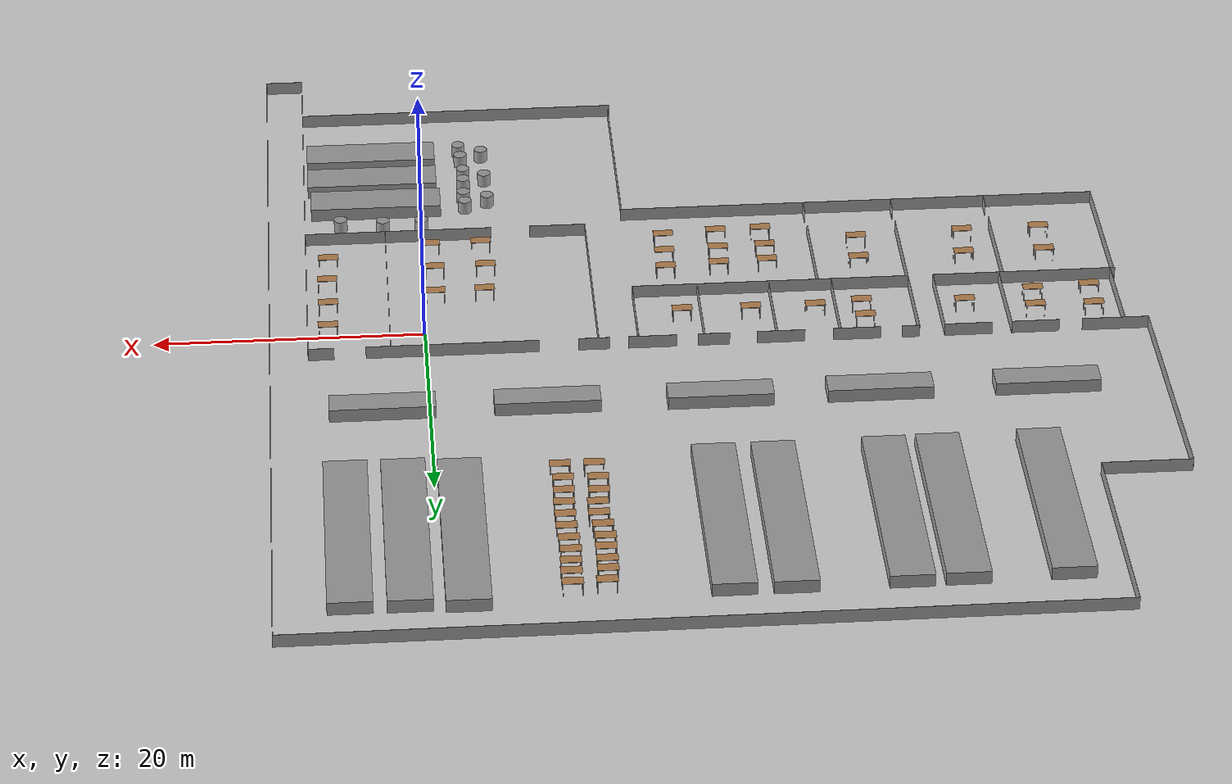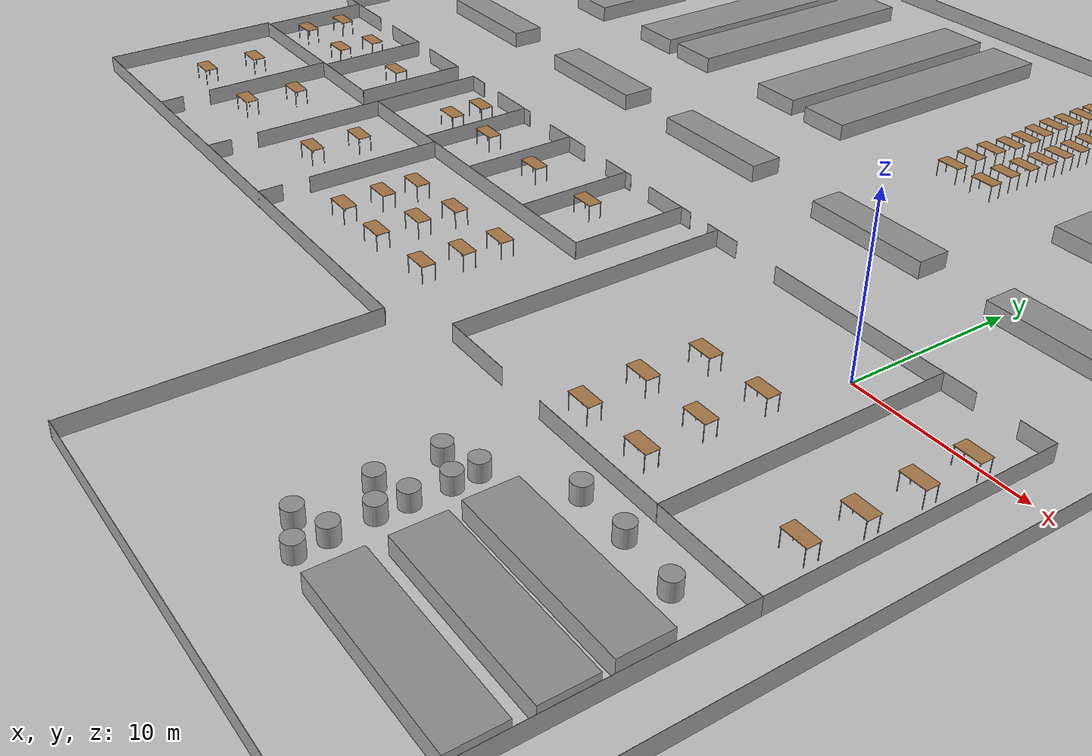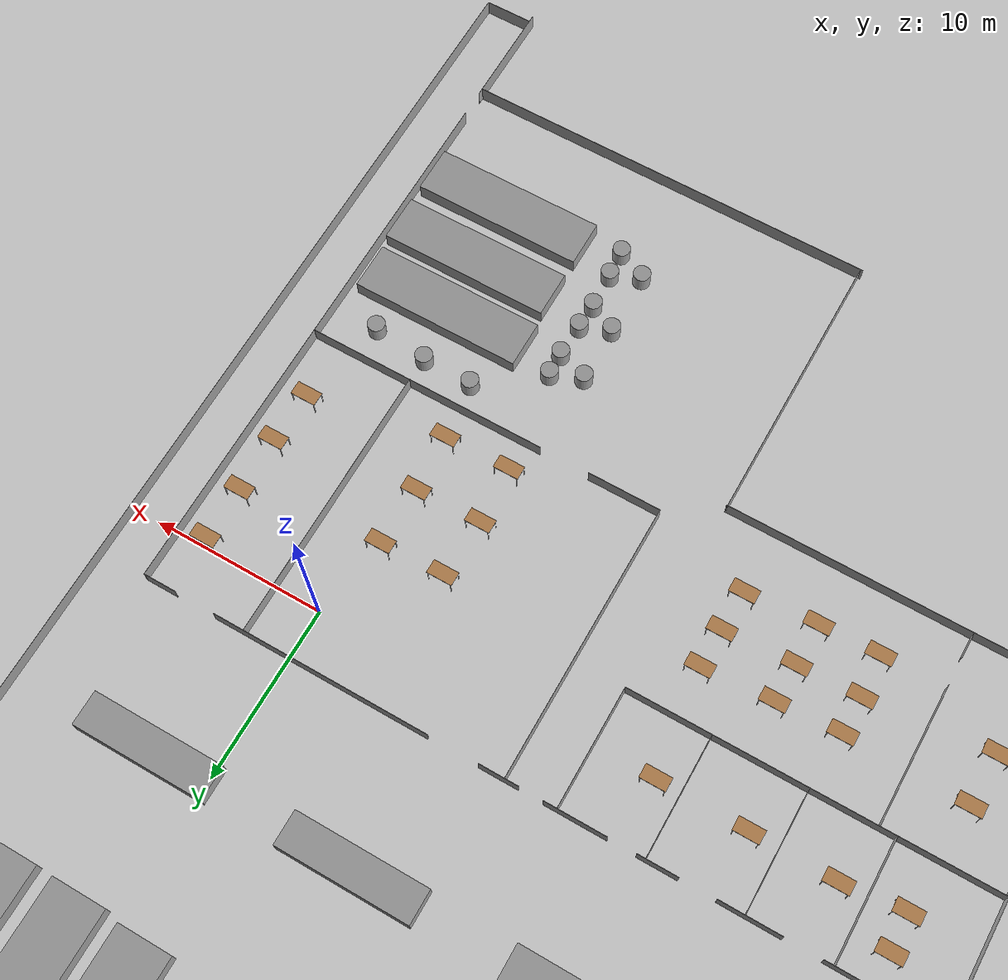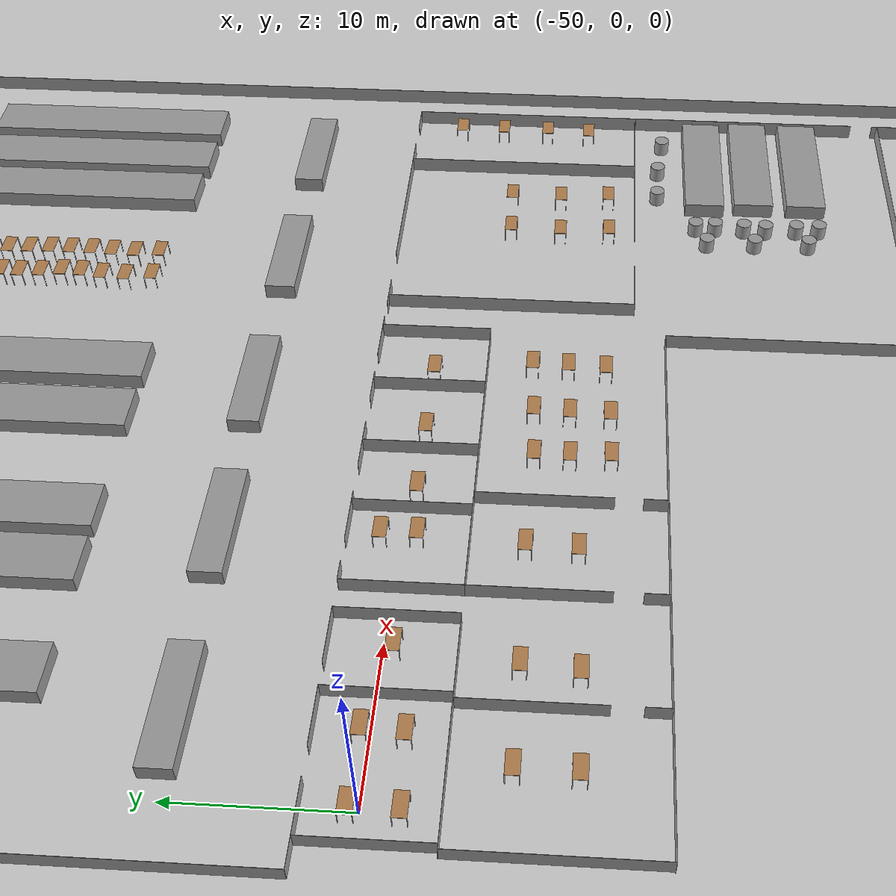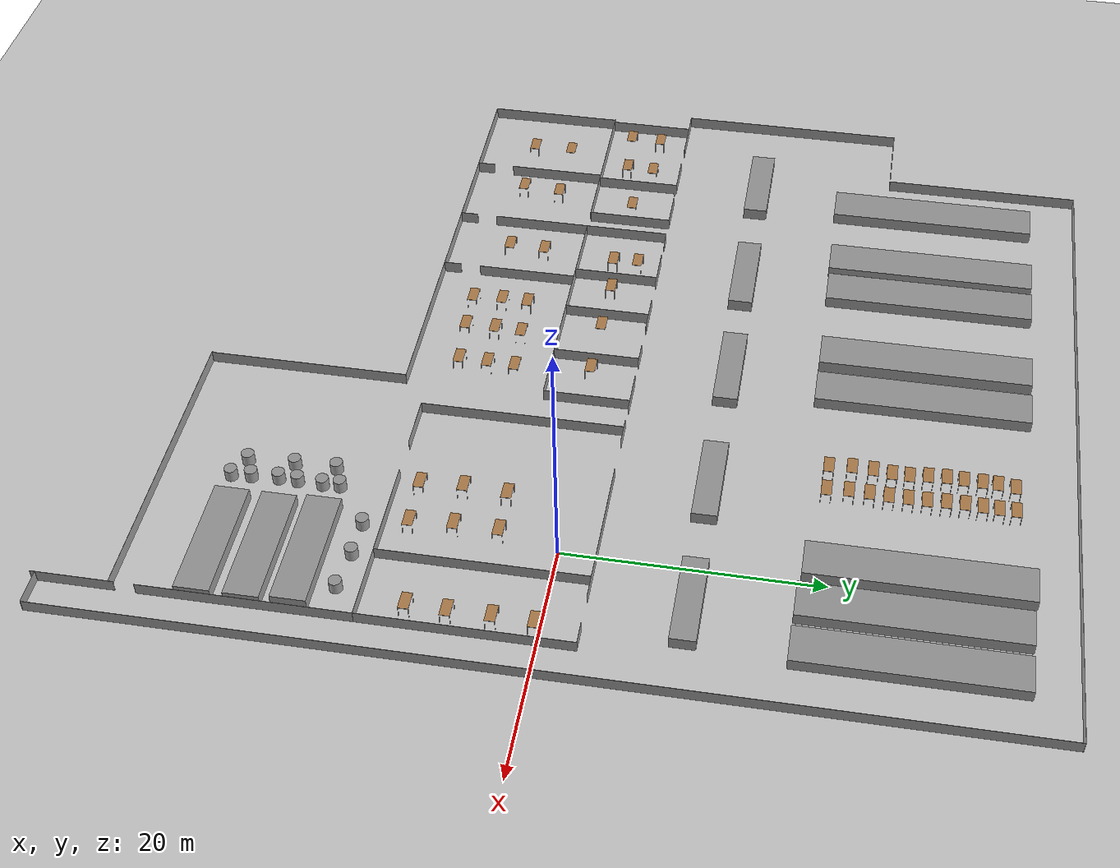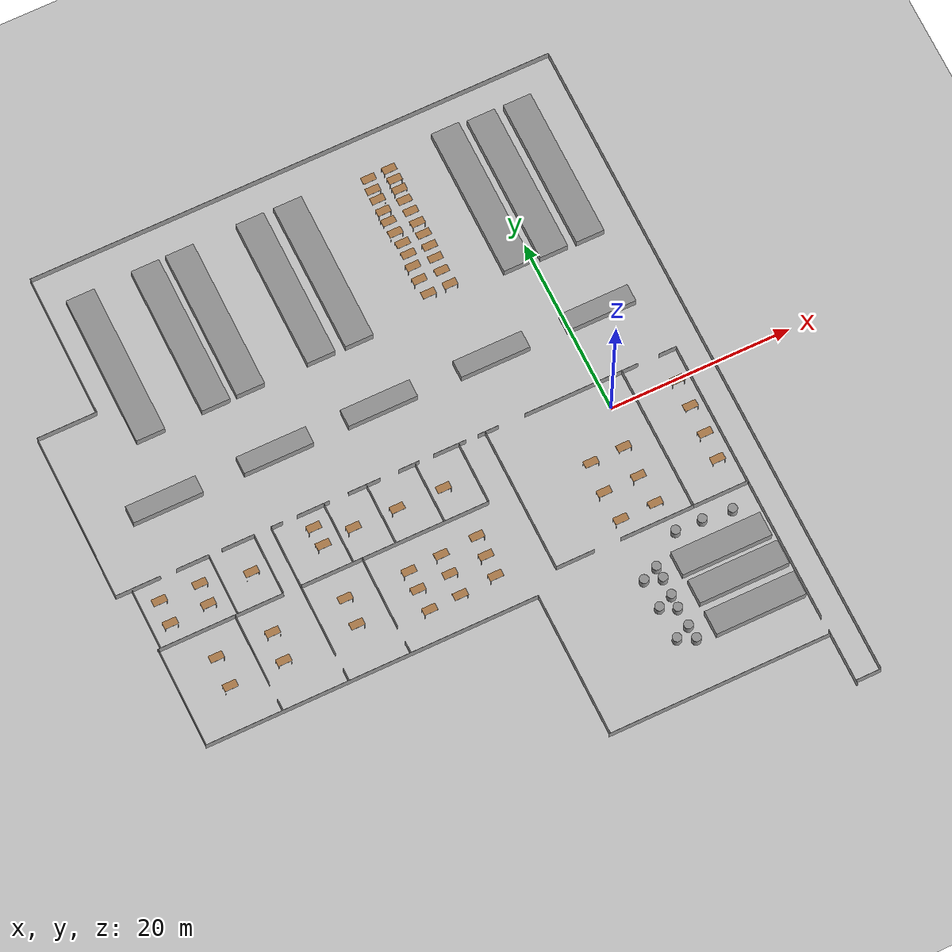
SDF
<sdf version="1.6">
 <world name="default">
  <light name="sun" type="directional">
   <pose>0 0 10 0 -0 0</pose>
   <diffuse>0.8 0.8 0.8 1</diffuse>
   <specular>0.2 0.2 0.2 1</specular>
   <attenuation>
    <range>1000</range>
    <constant>0.9</constant>
    <linear>0.01</linear>
    <quadratic>0.001</quadratic>
   </attenuation>
   <direction>-0.5 0.1 -0.9</direction>
  </light>
  <model name="ground_plane">
   <static>1</static>
   <link name="link">
    <collision name="collision">
     <geometry><plane><normal>0 0 1</normal><size>100 100</size></plane></geometry>
     <surface>
      <contact><collide_bitmask>65535</collide_bitmask></contact>
      <friction><ode><mu>100</mu><mu2>50</mu2></ode></friction>
     </surface>
    </collision>
    <visual name="visual">
     <cast_shadows>0</cast_shadows>
     <geometry><plane><normal>0 0 1</normal><size>100 100</size></plane></geometry>
     <material>
      <script><uri>file://media/materials/scripts/gazebo.material</uri><name>Gazebo/Grey</name></script>
     </material>
    </visual>
   </link>
  </model>
  <gravity>0 0 -9.8</gravity>
  <magnetic_field>6e-06 2.3e-05 -4.2e-05</magnetic_field>
  <atmosphere type="adiabatic"/>
  <physics name="default_physics" default="0" type="ode">
   <max_step_size>0.001</max_step_size>
   <real_time_factor>1</real_time_factor>
   <real_time_update_rate>1000</real_time_update_rate>
  </physics>
  <scene><ambient>0.4 0.4 0.4 1</ambient><background>0.7 0.7 0.7 1</background><shadows>1</shadows></scene>
  <spherical_coordinates>
   <surface_model>EARTH_WGS84</surface_model>
   <latitude_deg>0</latitude_deg>
   <longitude_deg>0</longitude_deg>
   <elevation>0</elevation>
   <heading_deg>0</heading_deg>
  </spherical_coordinates>
  <model name="unit_box">
   <static>1</static>
   <pose>8.66348 -5.199 0.5 0 -0 0</pose>
   <link name="link">
    <inertial>
     <mass>1</mass>
     <inertia>
      <ixx>0.166667</ixx>
      <ixy>0</ixy>
      <ixz>0</ixz>
      <iyy>0.166667</iyy>
      <iyz>0</iyz>
      <izz>0.166667</izz>
     </inertia>
    </inertial>
    <collision name="collision"><geometry><box><size>0.01642 16.3082 1</size></box></geometry></collision>
    <visual name="visual">
     <geometry><box><size>0.01642 16.3082 1</size></box></geometry>
     <material>
      <script><name>Gazebo/Grey</name><uri>file://media/materials/scripts/gazebo.material</uri></script>
     </material>
    </visual>
   </link>
  </model>
  <model name="unit_box_clone">
   <static>1</static>
   <pose>-12.382 2.93917 0.5 0 -0 0</pose>
   <link name="link">
    <inertial>
     <mass>1</mass>
     <inertia>
      <ixx>0.166667</ixx>
      <ixy>0</ixy>
      <ixz>0</ixz>
      <iyy>0.166667</iyy>
      <iyz>0</iyz>
      <izz>0.166667</izz>
     </inertia>
    </inertial>
    <collision name="collision"><geometry><box><size>2.29373 0.014042 1</size></box></geometry></collision>
    <visual name="visual">
     <geometry><box><size>2.29373 0.014042 1</size></box></geometry>
     <material>
      <script><name>Gazebo/Grey</name><uri>file://media/materials/scripts/gazebo.material</uri></script>
     </material>
    </visual>
   </link>
  </model>
  <model name="unit_box_0">
   <static>1</static>
   <pose>5.618314 -13.282811 0.5 0 -0 0</pose>
   <link name="link">
    <inertial>
     <mass>1</mass>
     <inertia>
      <ixx>0.166667</ixx>
      <ixy>0</ixy>
      <ixz>0</ixz>
      <iyy>0.166667</iyy>
      <iyz>0</iyz>
      <izz>0.166667</izz>
     </inertia>
    </inertial>
    <collision name="collision"><geometry><box><size>6.0747 0.010616 1</size></box></geometry></collision>
    <visual name="visual">
     <geometry><box><size>6.0747 0.010616 1</size></box></geometry>
     <material>
      <script><name>Gazebo/Grey</name><uri>file://media/materials/scripts/gazebo.material</uri></script>
     </material>
    </visual>
   </link>
  </model>
  <model name="unit_box_0_clone">
   <static>1</static>
   <pose>2.57442 -5.17191 0.5 0 -0 0</pose>
   <link name="link">
    <inertial>
     <mass>1</mass>
     <inertia>
      <ixx>0.166667</ixx>
      <ixy>0</ixy>
      <ixz>0</ixz>
      <iyy>0.166667</iyy>
      <iyz>0</iyz>
      <izz>0.166667</izz>
     </inertia>
    </inertial>
    <collision name="collision"><geometry><box><size>0.015785 16.224 1</size></box></geometry></collision>
    <visual name="visual">
     <geometry><box><size>0.015785 16.224 1</size></box></geometry>
     <material>
      <script><name>Gazebo/Grey</name><uri>file://media/materials/scripts/gazebo.material</uri></script>
     </material>
    </visual>
   </link>
  </model>
  <model name="unit_box_clone_clone">
   <static>1</static>
   <pose>-1.97057 2.94393 0.5 0 -0 0</pose>
   <link name="link">
    <inertial>
     <mass>1</mass>
     <inertia>
      <ixx>0.166667</ixx>
      <ixy>0</ixy>
      <ixz>0</ixz>
      <iyy>0.166667</iyy>
      <iyz>0</iyz>
      <izz>0.166667</izz>
     </inertia>
    </inertial>
    <collision name="collision"><geometry><box><size>12.7693 0.014042 1</size></box></geometry></collision>
    <visual name="visual">
     <geometry><box><size>12.7693 0.014042 1</size></box></geometry>
     <material>
      <script><name>Gazebo/Grey</name><uri>file://media/materials/scripts/gazebo.material</uri></script>
     </material>
    </visual>
   </link>
  </model>
  <model name="unit_box_clone_clone_clone">
   <static>1</static>
   <pose>-1.4868 -13.287 0.5 0 -0 0</pose>
   <link name="link">
    <inertial>
     <mass>1</mass>
     <inertia>
      <ixx>0.166667</ixx>
      <ixy>0</ixy>
      <ixz>0</ixz>
      <iyy>0.166667</iyy>
      <iyz>0</iyz>
      <izz>0.166667</izz>
     </inertia>
    </inertial>
    <collision name="collision"><geometry><box><size>8.11356 0.014042 1</size></box></geometry></collision>
    <visual name="visual">
     <geometry><box><size>8.11356 0.014042 1</size></box></geometry>
     <material>
      <script><name>Gazebo/Grey</name><uri>file://media/materials/scripts/gazebo.material</uri></script>
     </material>
    </visual>
   </link>
  </model>
  <model name="unit_box_0_clone_clone">
   <static>1</static>
   <pose>-12.7381 -5.17234 0.5 0 -0 0</pose>
   <link name="link">
    <inertial>
     <mass>1</mass>
     <inertia>
      <ixx>0.166667</ixx>
      <ixy>0</ixy>
      <ixz>0</ixz>
      <iyy>0.166667</iyy>
      <iyz>0</iyz>
      <izz>0.166667</izz>
     </inertia>
    </inertial>
    <collision name="collision"><geometry><box><size>0.015785 16.224 1</size></box></geometry></collision>
    <visual name="visual">
     <geometry><box><size>0.015785 16.224 1</size></box></geometry>
     <material>
      <script><name>Gazebo/Grey</name><uri>file://media/materials/scripts/gazebo.material</uri></script>
     </material>
    </visual>
   </link>
  </model>
  <model name="unit_box_0_clone_clone_0">
   <static>1</static>
   <pose>11.4759 0.513212 0.5 0 -0 0</pose>
   <link name="link">
    <inertial>
     <mass>1</mass>
     <inertia>
      <ixx>0.166667</ixx>
      <ixy>0</ixy>
      <ixz>0</ixz>
      <iyy>0.166667</iyy>
      <iyz>0</iyz>
      <izz>0.166667</izz>
     </inertia>
    </inertial>
    <collision name="collision"><geometry><box><size>0.015785 75.00 1</size></box></geometry></collision>
    <visual name="visual">
     <geometry><box><size>0.015785 75.00 1</size></box></geometry>
     <material>
      <script><name>Gazebo/Grey</name><uri>file://media/materials/scripts/gazebo.material</uri></script>
     </material>
    </visual>
   </link>
  </model>
  <model name="unit_box_clone_clone_clone_0">
   <static>1</static>
   <pose>-17.768 38.0386 0.5 0 -0 0</pose>
   <link name="link">
    <inertial>
     <mass>1</mass>
     <inertia>
      <ixx>0.166667</ixx>
      <ixy>0</ixy>
      <ixz>0</ixz>
      <iyy>0.166667</iyy>
      <iyz>0</iyz>
      <izz>0.166667</izz>
     </inertia>
    </inertial>
    <collision name="collision"><geometry><box><size>58.500 0.014042 1</size></box></geometry></collision>
    <visual name="visual">
     <geometry><box><size>58.50 0.014042 1</size></box></geometry>
     <material>
      <script><name>Gazebo/Grey</name><uri>file://media/materials/scripts/gazebo.material</uri></script>
     </material>
    </visual>
   </link>
  </model>
  <model name="unit_box_clone_clone_clone_0_clone">
   <static>1</static>
   <pose>-51.129 2.94542 0.5 0 -0 0</pose>
   <link name="link">
    <inertial>
     <mass>1</mass>
     <inertia>
      <ixx>0.166667</ixx>
      <ixy>0</ixy>
      <ixz>0</ixz>
      <iyy>0.166667</iyy>
      <iyz>0</iyz>
      <izz>0.166667</izz>
     </inertia>
    </inertial>
    <collision name="collision"><geometry><box><size>4.94814 0.014042 1</size></box></geometry></collision>
    <visual name="visual">
     <geometry><box><size>4.94814 0.014042 1</size></box></geometry>
     <material>
      <script><name>Gazebo/Grey</name><uri>file://media/materials/scripts/gazebo.material</uri></script>
     </material>
    </visual>
   </link>
  </model>
  <model name="unit_box_0_clone_clone_clone">
   <static>1</static>
   <pose>-47.014 29.9266 0.5 0 -0 0</pose>
   <link name="link">
    <inertial>
     <mass>1</mass>
     <inertia>
      <ixx>0.166667</ixx>
      <ixy>0</ixy>
      <ixz>0</ixz>
      <iyy>0.166667</iyy>
      <iyz>0</iyz>
      <izz>0.166667</izz>
     </inertia>
    </inertial>
    <collision name="collision"><geometry><box><size>0.015785 16.224 1</size></box></geometry></collision>
    <visual name="visual">
     <geometry><box><size>0.015785 16.224 1</size></box></geometry>
     <material>
      <script><name>Gazebo/Grey</name><uri>file://media/materials/scripts/gazebo.material</uri></script>
     </material>
    </visual>
   </link>
  </model>
  <model name="unit_box_0_clone_clone_clone_clone">
   <static>1</static>
   <pose>-53.5916 12.387 0.5 0 -0 0</pose>
   <link name="link">
    <inertial>
     <mass>1</mass>
     <inertia>
      <ixx>0.166667</ixx>
      <ixy>0</ixy>
      <ixz>0</ixz>
      <iyy>0.166667</iyy>
      <iyz>0</iyz>
      <izz>0.166667</izz>
     </inertia>
    </inertial>
    <collision name="collision"><geometry><box><size>0.015785 18.88461 1</size></box></geometry></collision>
    <visual name="visual">
     <geometry><box><size>0.015785 18.88461 1</size></box></geometry>
     <material>
      <script><name>Gazebo/Grey</name><uri>file://media/materials/scripts/gazebo.material</uri></script>
     </material>
    </visual>
   </link>
  </model>
  <model name="unit_box_clone_clone_clone_1">
   <static>1</static>
   <pose>-50.306 21.822 0.5 0 -0 0</pose>
   <link name="link">
    <inertial>
     <mass>1</mass>
     <inertia>
      <ixx>0.166667</ixx>
      <ixy>0</ixy>
      <ixz>0</ixz>
      <iyy>0.166667</iyy>
      <iyz>0</iyz>
      <izz>0.166667</izz>
     </inertia>
    </inertial>
    <collision name="collision"><geometry><box><size>6.5711 0.014042 1</size></box></geometry></collision>
    <visual name="visual">
     <geometry><box><size>6.5711 0.014042 1</size></box></geometry>
     <material>
      <script><name>Gazebo/Grey</name><uri>file://media/materials/scripts/gazebo.material</uri></script>
     </material>
    </visual>
   </link>
  </model>
  <model name="unit_box_clone_clone_clone_2">
   <static>1</static>
   <pose>-3.5869 -31.4552 0.5 0 -0 0</pose>
   <link name="link">
    <inertial>
     <mass>1</mass>
     <inertia>
      <ixx>0.166667</ixx>
      <ixy>0</ixy>
      <ixz>0</ixz>
      <iyy>0.166667</iyy>
      <iyz>0</iyz>
      <izz>0.166667</izz>
     </inertia>
    </inertial>
    <collision name="collision"><geometry><box><size>24.508914 0.014042 1</size></box></geometry></collision>
    <visual name="visual">
     <geometry><box><size>24.5098914 0.014042 1</size></box></geometry>
     <material>
      <script><name>Gazebo/Grey</name><uri>file://media/materials/scripts/gazebo.material</uri></script>
     </material>
    </visual>
   </link>
  </model>
  <model name="unit_box_0_clone_clone_0_clone">
   <static>1</static>
   <pose>8.66604 -21.3952 0.5 0 -0 0</pose>
   <link name="link">
    <inertial>
     <mass>1</mass>
     <inertia>
      <ixx>0.166667</ixx>
      <ixy>0</ixy>
      <ixz>0</ixz>
      <iyy>0.166667</iyy>
      <iyz>0</iyz>
      <izz>0.166667</izz>
     </inertia>
    </inertial>
    <collision name="collision"><geometry><box><size>0.015785 16.224 1</size></box></geometry></collision>
    <visual name="visual">
     <geometry><box><size>0.015785 16.224 1</size></box></geometry>
     <material>
      <script><name>Gazebo/Grey</name><uri>file://media/materials/scripts/gazebo.material</uri></script>
     </material>
    </visual>
   </link>
  </model>
  <model name="unit_box_0_clone_clone_0_clone_clone">
   <static>1</static>
   <pose>8.66561 -34.2292 0.5 0 -0 0</pose>
   <link name="link">
    <inertial>
     <mass>1</mass>
     <inertia>
      <ixx>0.166667</ixx>
      <ixy>0</ixy>
      <ixz>0</ixz>
      <iyy>0.166667</iyy>
      <iyz>0</iyz>
      <izz>0.166667</izz>
     </inertia>
    </inertial>
    <collision name="collision"><geometry><box><size>0.015785 6.33435 1</size></box></geometry></collision>
    <visual name="visual">
     <geometry><box><size>0.015785 6.33435 1</size></box></geometry>
     <material>
      <script><name>Gazebo/Grey</name><uri>file://media/materials/scripts/gazebo.material</uri></script>
     </material>
    </visual>
   </link>
  </model>
  <model name="unit_box_clone_clone_clone_2_clone">
   <static>1</static>
   <pose>10.0717 -37.0022 0.5 0 -0 0</pose>
   <link name="link">
    <inertial>
     <mass>1</mass>
     <inertia>
      <ixx>0.166667</ixx>
      <ixy>0</ixy>
      <ixz>0</ixz>
      <iyy>0.166667</iyy>
      <iyz>0</iyz>
      <izz>0.166667</izz>
     </inertia>
    </inertial>
    <collision name="collision"><geometry><box><size>2.80525 0.014042 1</size></box></geometry></collision>
    <visual name="visual">
     <geometry><box><size>2.80525 0.014042 1</size></box></geometry>
     <material>
      <script><name>Gazebo/Grey</name><uri>file://media/materials/scripts/gazebo.material</uri></script>
     </material>
    </visual>
   </link>
  </model>
  <model name="unit_box_0_clone_clone_0_clone_0">
   <static>1</static>
   <pose>-15.6926 -23.3512 0.5 0 -0 0</pose>
   <link name="link">
    <inertial>
     <mass>1</mass>
     <inertia>
      <ixx>0.166667</ixx>
      <ixy>0</ixy>
      <ixz>0</ixz>
      <iyy>0.166667</iyy>
      <iyz>0</iyz>
      <izz>0.166667</izz>
     </inertia>
    </inertial>
    <collision name="collision"><geometry><box><size>0.015785 16.224 1</size></box></geometry></collision>
    <visual name="visual">
     <geometry><box><size>0.015785 16.224 1</size></box></geometry>
     <material>
      <script><name>Gazebo/Grey</name><uri>file://media/materials/scripts/gazebo.material</uri></script>
     </material>
    </visual>
   </link>
  </model>
  <model name="unit_box_0_clone_clone_0_clone_0_clone">
   <static>1</static>
   <pose>-15.6923 -0.54068 0.5 0 -0 0</pose>
   <link name="link">
    <inertial>
     <mass>1</mass>
     <inertia>
      <ixx>0.166667</ixx>
      <ixy>0</ixy>
      <ixz>0</ixz>
      <iyy>0.166667</iyy>
      <iyz>0</iyz>
      <izz>0.166667</izz>
     </inertia>
    </inertial>
    <collision name="collision"><geometry><box><size>0.015785 6.986043 1</size></box></geometry></collision>
    <visual name="visual">
     <geometry><box><size>0.015785 6.986043 1</size></box></geometry>
     <material>
      <script><name>Gazebo/Grey</name><uri>file://media/materials/scripts/gazebo.material</uri></script>
     </material>
    </visual>
   </link>
  </model>
  <model name="unit_box_clone_clone_clone_2_clone_0">
   <static>1</static>
   <pose>-33.9125 -15.248 0.5 0 -0 0</pose>
   <link name="link">
    <inertial>
     <mass>1</mass>
     <inertia>
      <ixx>0.166667</ixx>
      <ixy>0</ixy>
      <ixz>0</ixz>
      <iyy>0.166667</iyy>
      <iyz>0</iyz>
      <izz>0.166667</izz>
     </inertia>
    </inertial>
    <collision name="collision"><geometry><box><size>36.576549 0.014042 1</size></box></geometry></collision>
    <visual name="visual">
     <geometry><box><size>36.576549 0.014042 1</size></box></geometry>
     <material>
      <script><name>Gazebo/Grey</name><uri>file://media/materials/scripts/gazebo.material</uri></script>
     </material>
    </visual>
   </link>
  </model>
  <model name="unit_box_clone_clone_clone_2_clone_0_clone">
   <static>1</static>
   <pose>-26.1024 -4.02473 0.5 0 -0 0</pose>
   <link name="link">
    <inertial>
     <mass>1</mass>
     <inertia>
      <ixx>0.166667</ixx>
      <ixy>0</ixy>
      <ixz>0</ixz>
      <iyy>0.166667</iyy>
      <iyz>0</iyz>
      <izz>0.166667</izz>
     </inertia>
    </inertial>
    <collision name="collision"><geometry><box><size>20.80304 0.014042 1</size></box></geometry></collision>
    <visual name="visual">
     <geometry><box><size>20.80304 0.014042 1</size></box></geometry>
     <material>
      <script><name>Gazebo/Grey</name><uri>file://media/materials/scripts/gazebo.material</uri></script>
     </material>
    </visual>
   </link>
  </model>
  <model name="unit_box_0_clone_clone_clone_0">
   <static>1</static>
   <pose>-52.1311 -9.63644 0.5 0 -0 0</pose>
   <link name="link">
    <inertial>
     <mass>1</mass>
     <inertia>
      <ixx>0.166667</ixx>
      <ixy>0</ixy>
      <ixz>0</ixz>
      <iyy>0.166667</iyy>
      <iyz>0</iyz>
      <izz>0.166667</izz>
     </inertia>
    </inertial>
    <collision name="collision"><geometry><box><size>0.015785 11.23237 1</size></box></geometry></collision>
    <visual name="visual">
     <geometry><box><size>0.015785 11.23237 1</size></box></geometry>
     <material>
      <script><name>Gazebo/Grey</name><uri>file://media/materials/scripts/gazebo.material</uri></script>
     </material>
    </visual>
   </link>
  </model>
  <model name="unit_box_0_clone_clone_clone_0_clone">
   <static>1</static>
   <pose>-43.745 -8.06353 0.5 0 -0 0</pose>
   <link name="link">
    <inertial>
     <mass>1</mass>
     <inertia>
      <ixx>0.166667</ixx>
      <ixy>0</ixy>
      <ixz>0</ixz>
      <iyy>0.166667</iyy>
      <iyz>0</iyz>
      <izz>0.166667</izz>
     </inertia>
    </inertial>
    <collision name="collision"><geometry><box><size>0.015785 8.00153 1</size></box></geometry></collision>
    <visual name="visual">
     <geometry><box><size>0.015785 8.00153 1</size></box></geometry>
     <material>
      <script><name>Gazebo/Grey</name><uri>file://media/materials/scripts/gazebo.material</uri></script>
     </material>
    </visual>
   </link>
  </model>
  <model name="unit_box_0_clone_clone_clone_0_clone_0">
   <static>1</static>
   <pose>-43.7417 -14.521 0.5 0 -0 0</pose>
   <link name="link">
    <inertial>
     <mass>1</mass>
     <inertia>
      <ixx>0.166667</ixx>
      <ixy>0</ixy>
      <ixz>0</ixz>
      <iyy>0.166667</iyy>
      <iyz>0</iyz>
      <izz>0.166667</izz>
     </inertia>
    </inertial>
    <collision name="collision"><geometry><box><size>0.015785 1.45793 1</size></box></geometry></collision>
    <visual name="visual">
     <geometry><box><size>0.015785 1.45793 1</size></box></geometry>
     <material>
      <script><name>Gazebo/Grey</name><uri>file://media/materials/scripts/gazebo.material</uri></script>
     </material>
    </visual>
   </link>
  </model>
  <model name="unit_box_0_clone_clone_clone_0_clone_0_clone">
   <static>1</static>
   <pose>-36.513 -14.5195 0.5 0 -0 0</pose>
   <link name="link">
    <inertial>
     <mass>1</mass>
     <inertia>
      <ixx>0.166667</ixx>
      <ixy>0</ixy>
      <ixz>0</ixz>
      <iyy>0.166667</iyy>
      <iyz>0</iyz>
      <izz>0.166667</izz>
     </inertia>
    </inertial>
    <collision name="collision"><geometry><box><size>0.015785 1.45367 1</size></box></geometry></collision>
    <visual name="visual">
     <geometry><box><size>0.015785 1.45367 1</size></box></geometry>
     <material>
      <script><name>Gazebo/Grey</name><uri>file://media/materials/scripts/gazebo.material</uri></script>
     </material>
    </visual>
   </link>
  </model>
  <model name="unit_box_0_clone_clone_clone_0_clone_clone">
   <static>1</static>
   <pose>-36.514 -8.07989 0.5 0 -0 0</pose>
   <link name="link">
    <inertial>
     <mass>1</mass>
     <inertia>
      <ixx>0.166667</ixx>
      <ixy>0</ixy>
      <ixz>0</ixz>
      <iyy>0.166667</iyy>
      <iyz>0</iyz>
      <izz>0.166667</izz>
     </inertia>
    </inertial>
    <collision name="collision"><geometry><box><size>0.015785 8.11538 1</size></box></geometry></collision>
    <visual name="visual">
     <geometry><box><size>0.015785 8.11538 1</size></box></geometry>
     <material>
      <script><name>Gazebo/Grey</name><uri>file://media/materials/scripts/gazebo.material</uri></script>
     </material>
    </visual>
   </link>
  </model>
  <model name="unit_box_0_clone_clone_clone_0_clone_clone_clone">
   <static>1</static>
   <pose>-29.7303 -8.08775 0.5 0 -0 0</pose>
   <link name="link">
    <inertial>
     <mass>1</mass>
     <inertia>
      <ixx>0.166667</ixx>
      <ixy>0</ixy>
      <ixz>0</ixz>
      <iyy>0.166667</iyy>
      <iyz>0</iyz>
      <izz>0.166667</izz>
     </inertia>
    </inertial>
    <collision name="collision"><geometry><box><size>0.015785 8.11538 1</size></box></geometry></collision>
    <visual name="visual">
     <geometry><box><size>0.015785 8.11538 1</size></box></geometry>
     <material>
      <script><name>Gazebo/Grey</name><uri>file://media/materials/scripts/gazebo.material</uri></script>
     </material>
    </visual>
   </link>
  </model>
  <model name="unit_box_0_clone_clone_clone_0_clone_0_clone_clone">
   <static>1</static>
   <pose>-29.7293 -14.5292 0.5 0 -0 0</pose>
   <link name="link">
    <inertial>
     <mass>1</mass>
     <inertia>
      <ixx>0.166667</ixx>
      <ixy>0</ixy>
      <ixz>0</ixz>
      <iyy>0.166667</iyy>
      <iyz>0</iyz>
      <izz>0.166667</izz>
     </inertia>
    </inertial>
    <collision name="collision"><geometry><box><size>0.015785 1.45367 1</size></box></geometry></collision>
    <visual name="visual">
     <geometry><box><size>0.015785 1.45367 1</size></box></geometry>
     <material>
      <script><name>Gazebo/Grey</name><uri>file://media/materials/scripts/gazebo.material</uri></script>
     </material>
    </visual>
   </link>
  </model>
  <model name="unit_box_0_clone_clone_clone_0_clone_clone_clone_clone">
   <static>1</static>
   <pose>-20.5831 -0.542167 0.5 0 -0 0</pose>
   <link name="link">
    <inertial>
     <mass>1</mass>
     <inertia>
      <ixx>0.166667</ixx>
      <ixy>0</ixy>
      <ixz>0</ixz>
      <iyy>0.166667</iyy>
      <iyz>0</iyz>
      <izz>0.166667</izz>
     </inertia>
    </inertial>
    <collision name="collision"><geometry><box><size>0.015785 6.975315 1</size></box></geometry></collision>
    <visual name="visual">
     <geometry><box><size>0.015785 6.975315 1</size></box></geometry>
     <material>
      <script><name>Gazebo/Grey</name><uri>file://media/materials/scripts/gazebo.material</uri></script>
     </material>
    </visual>
   </link>
  </model>
  <model name="unit_box_0_clone_clone_clone_0_clone_clone_clone_clone_clone">
   <static>1</static>
   <pose>-25.9646 -0.540087 0.5 0 -0 0</pose>
   <link name="link">
    <inertial>
     <mass>1</mass>
     <inertia>
      <ixx>0.166667</ixx>
      <ixy>0</ixy>
      <ixz>0</ixz>
      <iyy>0.166667</iyy>
      <iyz>0</iyz>
      <izz>0.166667</izz>
     </inertia>
    </inertial>
    <collision name="collision"><geometry><box><size>0.015785 6.97044 1</size></box></geometry></collision>
    <visual name="visual">
     <geometry><box><size>0.015785 6.97044 1</size></box></geometry>
     <material>
      <script><name>Gazebo/Grey</name><uri>file://media/materials/scripts/gazebo.material</uri></script>
     </material>
    </visual>
   </link>
  </model>
  <model name="unit_box_0_clone_clone_clone_0_clone_clone_clone_clone_clone_0">
   <static>1</static>
   <pose>-30.6799 -0.541659 0.5 0 -0 0</pose>
   <link name="link">
    <inertial>
     <mass>1</mass>
     <inertia>
      <ixx>0.166667</ixx>
      <ixy>0</ixy>
      <ixz>0</ixz>
      <iyy>0.166667</iyy>
      <iyz>0</iyz>
      <izz>0.166667</izz>
     </inertia>
    </inertial>
    <collision name="collision"><geometry><box><size>0.015785 6.97044 1</size></box></geometry></collision>
    <visual name="visual">
     <geometry><box><size>0.015785 6.97044 1</size></box></geometry>
     <material>
      <script><name>Gazebo/Grey</name><uri>file://media/materials/scripts/gazebo.material</uri></script>
     </material>
    </visual>
   </link>
  </model>
  <model name="unit_box_0_clone_clone_clone_0_clone_clone_clone_clone_clone_1">
   <static>1</static>
   <pose>-36.5132 -0.538933 0.5 0 -0 0</pose>
   <link name="link">
    <inertial>
     <mass>1</mass>
     <inertia>
      <ixx>0.166667</ixx>
      <ixy>0</ixy>
      <ixz>0</ixz>
      <iyy>0.166667</iyy>
      <iyz>0</iyz>
      <izz>0.166667</izz>
     </inertia>
    </inertial>
    <collision name="collision"><geometry><box><size>0.015785 6.97044 1</size></box></geometry></collision>
    <visual name="visual">
     <geometry><box><size>0.015785 6.97044 1</size></box></geometry>
     <material>
      <script><name>Gazebo/Grey</name><uri>file://media/materials/scripts/gazebo.material</uri></script>
     </material>
    </visual>
   </link>
  </model>
  <model name="unit_box_0_clone_clone_clone_0_clone_clone_clone_clone_clone_2">
   <static>1</static>
   <pose>-38.3997 -0.538553 0.5 0 -0 0</pose>
   <link name="link">
    <inertial>
     <mass>1</mass>
     <inertia>
      <ixx>0.166667</ixx>
      <ixy>0</ixy>
      <ixz>0</ixz>
      <iyy>0.166667</iyy>
      <iyz>0</iyz>
      <izz>0.166667</izz>
     </inertia>
    </inertial>
    <collision name="collision"><geometry><box><size>0.015785 6.97044 1</size></box></geometry></collision>
    <visual name="visual">
     <geometry><box><size>0.015785 6.97044 1</size></box></geometry>
     <material>
      <script><name>Gazebo/Grey</name><uri>file://media/materials/scripts/gazebo.material</uri></script>
     </material>
    </visual>
   </link>
  </model>
  <model name="unit_box_0_clone_clone_clone_0_clone_clone_clone_clone_clone_3">
   <static>1</static>
   <pose>-43.3905 -0.547337 0.5 0 -0 0</pose>
   <link name="link">
    <inertial>
     <mass>1</mass>
     <inertia>
      <ixx>0.166667</ixx>
      <ixy>0</ixy>
      <ixz>0</ixz>
      <iyy>0.166667</iyy>
      <iyz>0</iyz>
      <izz>0.166667</izz>
     </inertia>
    </inertial>
    <collision name="collision"><geometry><box><size>0.015785 6.97044 1</size></box></geometry></collision>
    <visual name="visual">
     <geometry><box><size>0.015785 6.97044 1</size></box></geometry>
     <material>
      <script><name>Gazebo/Grey</name><uri>file://media/materials/scripts/gazebo.material</uri></script>
     </material>
    </visual>
   </link>
  </model>
  <model name="unit_box_0_clone_clone_clone_0_clone_clone_clone_clone_clone_4">
   <static>1</static>
   <pose>-51.8457 -0.537058 0.5 0 -0 0</pose>
   <link name="link">
    <inertial>
     <mass>1</mass>
     <inertia>
      <ixx>0.166667</ixx>
      <ixy>0</ixy>
      <ixz>0</ixz>
      <iyy>0.166667</iyy>
      <iyz>0</iyz>
      <izz>0.166667</izz>
     </inertia>
    </inertial>
    <collision name="collision"><geometry><box><size>0.015785 6.97044 1</size></box></geometry></collision>
    <visual name="visual">
     <geometry><box><size>0.015785 6.97044 1</size></box></geometry>
     <material>
      <script><name>Gazebo/Grey</name><uri>file://media/materials/scripts/gazebo.material</uri></script>
     </material>
    </visual>
   </link>
  </model>
  <model name="unit_box_clone_clone_clone_clone">
   <static>1</static>
   <pose>-10.6005 -13.2814 0.5 0 -0 0</pose>
   <link name="link">
    <inertial>
     <mass>1</mass>
     <inertia>
      <ixx>0.166667</ixx>
      <ixy>0</ixy>
      <ixz>0</ixz>
      <iyy>0.166667</iyy>
      <iyz>0</iyz>
      <izz>0.166667</izz>
     </inertia>
    </inertial>
    <collision name="collision"><geometry><box><size>4.2743 0.014042 1</size></box></geometry></collision>
    <visual name="visual">
     <geometry><box><size>4.2743 0.014042 1</size></box></geometry>
     <material>
      <script><name>Gazebo/Grey</name><uri>file://media/materials/scripts/gazebo.material</uri></script>
     </material>
    </visual>
   </link>
  </model>
  <model name="unit_box_clone_clone_clone_2_clone_0_clone_clone">
   <static>1</static>
   <pose>-45.3119 -4.0293 0.5 0 -0 0</pose>
   <link name="link">
    <inertial>
     <mass>1</mass>
     <inertia>
      <ixx>0.166667</ixx>
      <ixy>0</ixy>
      <ixz>0</ixz>
      <iyy>0.166667</iyy>
      <iyz>0</iyz>
      <izz>0.166667</izz>
     </inertia>
    </inertial>
    <collision name="collision"><geometry><box><size>13.83201 0.014042 1</size></box></geometry></collision>
    <visual name="visual">
     <geometry><box><size>13.83201 0.014042 1</size></box></geometry>
     <material>
      <script><name>Gazebo/Grey</name><uri>file://media/materials/scripts/gazebo.material</uri></script>
     </material>
    </visual>
   </link>
  </model>
  <model name="unit_box_clone_clone_clone_clone_0">
   <static>1</static>
   <pose>7.71066 2.93775 0.5 0 -0 0</pose>
   <link name="link">
    <inertial>
     <mass>1</mass>
     <inertia>
      <ixx>0.166667</ixx>
      <ixy>0</ixy>
      <ixz>0</ixz>
      <iyy>0.166667</iyy>
      <iyz>0</iyz>
      <izz>0.166667</izz>
     </inertia>
    </inertial>
    <collision name="collision"><geometry><box><size>1.9 0.014042 1</size></box></geometry></collision>
    <visual name="visual">
     <geometry><box><size>1.9 0.014042 1</size></box></geometry>
     <material>
      <script><name>Gazebo/Grey</name><uri>file://media/materials/scripts/gazebo.material</uri></script>
     </material>
    </visual>
   </link>
  </model>
  <model name="unit_box_clone_clone_0">
   <static>1</static>
   <pose>-16.7173 2.95237 0.5 0 -0 0</pose>
   <link name="link">
    <inertial>
     <mass>1</mass>
     <inertia>
      <ixx>0.166667</ixx>
      <ixy>0</ixy>
      <ixz>0</ixz>
      <iyy>0.166667</iyy>
      <iyz>0</iyz>
      <izz>0.166667</izz>
     </inertia>
    </inertial>
    <collision name="collision"><geometry><box><size>3.573000 0.014042 1</size></box></geometry></collision>
    <visual name="visual">
     <geometry><box><size>3.573000 0.014042 1</size></box></geometry>
     <material>
      <script><name>Gazebo/Grey</name><uri>file://media/materials/scripts/gazebo.material</uri></script>
     </material>
    </visual>
   </link>
  </model>
  <model name="unit_box_clone_clone_0_clone">
   <static>1</static>
   <pose>-21.2495 2.94693 0.5 0 -0 0</pose>
   <link name="link">
    <inertial>
     <mass>1</mass>
     <inertia>
      <ixx>0.166667</ixx>
      <ixy>0</ixy>
      <ixz>0</ixz>
      <iyy>0.166667</iyy>
      <iyz>0</iyz>
      <izz>0.166667</izz>
     </inertia>
    </inertial>
    <collision name="collision"><geometry><box><size>2.315261 0.014042 1</size></box></geometry></collision>
    <visual name="visual">
     <geometry><box><size>2.315261 0.014042 1</size></box></geometry>
     <material>
      <script><name>Gazebo/Grey</name><uri>file://media/materials/scripts/gazebo.material</uri></script>
     </material>
    </visual>
   </link>
  </model>
  <model name="unit_box_clone_clone_0_clone_clone">
   <static>1</static>
   <pose>-26.2178 2.94166 0.5 0 -0 0</pose>
   <link name="link">
    <inertial>
     <mass>1</mass>
     <inertia>
      <ixx>0.166667</ixx>
      <ixy>0</ixy>
      <ixz>0</ixz>
      <iyy>0.166667</iyy>
      <iyz>0</iyz>
      <izz>0.166667</izz>
     </inertia>
    </inertial>
    <collision name="collision"><geometry><box><size>3.5462 0.014042 1</size></box></geometry></collision>
    <visual name="visual">
     <geometry><box><size>3.5462 0.014042 1</size></box></geometry>
     <material>
      <script><name>Gazebo/Grey</name><uri>file://media/materials/scripts/gazebo.material</uri></script>
     </material>
    </visual>
   </link>
  </model>
  <model name="unit_box_clone_clone_0_clone_clone_clone">
   <static>1</static>
   <pose>-31.86 2.94203 0.5 0 -0 0</pose>
   <link name="link">
    <inertial>
     <mass>1</mass>
     <inertia>
      <ixx>0.166667</ixx>
      <ixy>0</ixy>
      <ixz>0</ixz>
      <iyy>0.166667</iyy>
      <iyz>0</iyz>
      <izz>0.166667</izz>
     </inertia>
    </inertial>
    <collision name="collision"><geometry><box><size>3.5462 0.014042 1</size></box></geometry></collision>
    <visual name="visual">
     <geometry><box><size>3.5462 0.014042 1</size></box></geometry>
     <material>
      <script><name>Gazebo/Grey</name><uri>file://media/materials/scripts/gazebo.material</uri></script>
     </material>
    </visual>
   </link>
  </model>
  <model name="unit_box_clone_clone_0_clone_clone_clone_0">
   <static>1</static>
   <pose>-35.8629 2.94591 0.5 0 -0 0</pose>
   <link name="link">
    <inertial>
     <mass>1</mass>
     <inertia>
      <ixx>0.166667</ixx>
      <ixy>0</ixy>
      <ixz>0</ixz>
      <iyy>0.166667</iyy>
      <iyz>0</iyz>
      <izz>0.166667</izz>
     </inertia>
    </inertial>
    <collision name="collision"><geometry><box><size>1.292 0.014042 1</size></box></geometry></collision>
    <visual name="visual">
     <geometry><box><size>1.292 0.014042 1</size></box></geometry>
     <material>
      <script><name>Gazebo/Grey</name><uri>file://media/materials/scripts/gazebo.material</uri></script>
     </material>
    </visual>
   </link>
  </model>
  <model name="unit_box_clone_clone_0_clone_clone_clone_1">
   <static>1</static>
   <pose>-40.1671 2.94153 0.5 0 -0 0</pose>
   <link name="link">
    <inertial>
     <mass>1</mass>
     <inertia>
      <ixx>0.166667</ixx>
      <ixy>0</ixy>
      <ixz>0</ixz>
      <iyy>0.166667</iyy>
      <iyz>0</iyz>
      <izz>0.166667</izz>
     </inertia>
    </inertial>
    <collision name="collision"><geometry><box><size>3.5462 0.014042 1</size></box></geometry></collision>
    <visual name="visual">
     <geometry><box><size>3.5462 0.014042 1</size></box></geometry>
     <material>
      <script><name>Gazebo/Grey</name><uri>file://media/materials/scripts/gazebo.material</uri></script>
     </material>
    </visual>
   </link>
  </model>
  <model name="unit_box_clone_clone_0_clone_clone_clone_2">
   <static>1</static>
   <pose>-45.1647 2.9297 0.5 0 -0 0</pose>
   <link name="link">
    <inertial>
     <mass>1</mass>
     <inertia>
      <ixx>0.166667</ixx>
      <ixy>0</ixy>
      <ixz>0</ixz>
      <iyy>0.166667</iyy>
      <iyz>0</iyz>
      <izz>0.166667</izz>
     </inertia>
    </inertial>
    <collision name="collision"><geometry><box><size>3.5462 0.014042 1</size></box></geometry></collision>
    <visual name="visual">
     <geometry><box><size>3.5462 0.014042 1</size></box></geometry>
     <material>
      <script><name>Gazebo/Grey</name><uri>file://media/materials/scripts/gazebo.material</uri></script>
     </material>
    </visual>
   </link>
  </model>
  <model name="unit_box_2_clone">
   <static>1</static>
   <pose>3.38689 -21.6455 0.5 0 -0 0</pose>
   <link name="link">
    <inertial>
     <mass>1</mass>
     <inertia>
      <ixx>0.166667</ixx>
      <ixy>0</ixy>
      <ixz>0</ixz>
      <iyy>0.166667</iyy>
      <iyz>0</iyz>
      <izz>0.166667</izz>
     </inertia>
    </inertial>
    <collision name="collision"><geometry><box><size>9.96993 2.71748 1</size></box></geometry></collision>
    <visual name="visual">
     <geometry><box><size>9.96993 2.71748 1</size></box></geometry>
     <material>
      <script><name>Gazebo/Grey</name><uri>file://media/materials/scripts/gazebo.material</uri></script>
     </material>
    </visual>
   </link>
  </model>
  <model name="unit_box_2_clone_0">
   <static>1</static>
   <pose>3.39312 -25.3306 0.5 0 -0 0</pose>
   <link name="link">
    <inertial>
     <mass>1</mass>
     <inertia>
      <ixx>0.166667</ixx>
      <ixy>0</ixy>
      <ixz>0</ixz>
      <iyy>0.166667</iyy>
      <iyz>0</iyz>
      <izz>0.166667</izz>
     </inertia>
    </inertial>
    <collision name="collision"><geometry><box><size>9.96993 2.71748 1</size></box></geometry></collision>
    <visual name="visual">
     <geometry><box><size>9.96993 2.71748 1</size></box></geometry>
     <material>
      <script><name>Gazebo/Grey</name><uri>file://media/materials/scripts/gazebo.material</uri></script>
     </material>
    </visual>
   </link>
  </model>
  <model name="unit_cylinder">
   <static>1</static>
   <pose>-3.70662 -17.5343 0.5 0 -0 0</pose>
   <link name="link">
    <inertial>
     <mass>1</mass>
     <inertia><ixx>0.145833</ixx><ixy>0</ixy><ixz>0</ixz><iyy>0.145833</iyy><iyz>0</iyz><izz>0.125</izz></inertia>
    </inertial>
    <collision name="collision">
     <geometry><cylinder><radius>0.5</radius><length>1</length></cylinder></geometry>
    </collision>
    <visual name="visual">
     <geometry><cylinder><radius>0.5</radius><length>1</length></cylinder></geometry>
     <material>
      <script><name>Gazebo/Grey</name><uri>file://media/materials/scripts/gazebo.material</uri></script>
     </material>
    </visual>
   </link>
  </model>
  <model name="unit_box_2_clone_1">
   <static>1</static>
   <pose>3.17488 -18.2078 0.5 0 -0 0</pose>
   <link name="link">
    <inertial>
     <mass>1</mass>
     <inertia>
      <ixx>0.166667</ixx>
      <ixy>0</ixy>
      <ixz>0</ixz>
      <iyy>0.166667</iyy>
      <iyz>0</iyz>
      <izz>0.166667</izz>
     </inertia>
    </inertial>
    <collision name="collision"><geometry><box><size>9.96993 2.71748 1</size></box></geometry></collision>
    <visual name="visual">
     <geometry><box><size>9.96993 2.71748 1</size></box></geometry>
     <material>
      <script><name>Gazebo/Grey</name><uri>file://media/materials/scripts/gazebo.material</uri></script>
     </material>
    </visual>
   </link>
  </model>
  <model name="unit_cylinder_0">
   <static>1</static>
   <pose>-3.64243 -18.8883 0.5 0 -0 0</pose>
   <link name="link">
    <inertial>
     <mass>1</mass>
     <inertia><ixx>0.145833</ixx><ixy>0</ixy><ixz>0</ixz><iyy>0.145833</iyy><iyz>0</iyz><izz>0.125</izz></inertia>
    </inertial>
    <collision name="collision">
     <geometry><cylinder><radius>0.5</radius><length>1</length></cylinder></geometry>
    </collision>
    <visual name="visual">
     <geometry><cylinder><radius>0.5</radius><length>1</length></cylinder></geometry>
     <material>
      <script><name>Gazebo/Grey</name><uri>file://media/materials/scripts/gazebo.material</uri></script>
     </material>
    </visual>
   </link>
  </model>
  <model name="unit_cylinder_1">
   <static>1</static>
   <pose>-3.69554 -20.8721 0.5 0 -0 0</pose>
   <link name="link">
    <inertial>
     <mass>1</mass>
     <inertia><ixx>0.145833</ixx><ixy>0</ixy><ixz>0</ixz><iyy>0.145833</iyy><iyz>0</iyz><izz>0.125</izz></inertia>
    </inertial>
    <collision name="collision">
     <geometry><cylinder><radius>0.5</radius><length>1</length></cylinder></geometry>
    </collision>
    <visual name="visual">
     <geometry><cylinder><radius>0.5</radius><length>1</length></cylinder></geometry>
     <material>
      <script><name>Gazebo/Grey</name><uri>file://media/materials/scripts/gazebo.material</uri></script>
     </material>
    </visual>
   </link>
  </model>
  <model name="unit_cylinder_2">
   <static>1</static>
   <pose>-3.74181 -22.3743 0.5 0 -0 0</pose>
   <link name="link">
    <inertial>
     <mass>1</mass>
     <inertia><ixx>0.145833</ixx><ixy>0</ixy><ixz>0</ixz><iyy>0.145833</iyy><iyz>0</iyz><izz>0.125</izz></inertia>
    </inertial>
    <collision name="collision">
     <geometry><cylinder><radius>0.5</radius><length>1</length></cylinder></geometry>
    </collision>
    <visual name="visual">
     <geometry><cylinder><radius>0.5</radius><length>1</length></cylinder></geometry>
     <material>
      <script><name>Gazebo/Grey</name><uri>file://media/materials/scripts/gazebo.material</uri></script>
     </material>
    </visual>
   </link>
  </model>
  <model name="unit_cylinder_3">
   <static>1</static>
   <pose>-3.61846 -24.5139 0.5 0 -0 0</pose>
   <link name="link">
    <inertial>
     <mass>1</mass>
     <inertia><ixx>0.145833</ixx><ixy>0</ixy><ixz>0</ixz><iyy>0.145833</iyy><iyz>0</iyz><izz>0.125</izz></inertia>
    </inertial>
    <collision name="collision">
     <geometry><cylinder><radius>0.5</radius><length>1</length></cylinder></geometry>
    </collision>
    <visual name="visual">
     <geometry><cylinder><radius>0.5</radius><length>1</length></cylinder></geometry>
     <material>
      <script><name>Gazebo/Grey</name><uri>file://media/materials/scripts/gazebo.material</uri></script>
     </material>
    </visual>
   </link>
  </model>
  <model name="unit_cylinder_4">
   <static>1</static>
   <pose>-3.51145 -26.0798 0.5 0 -0 0</pose>
   <link name="link">
    <inertial>
     <mass>1</mass>
     <inertia><ixx>0.145833</ixx><ixy>0</ixy><ixz>0</ixz><iyy>0.145833</iyy><iyz>0</iyz><izz>0.125</izz></inertia>
    </inertial>
    <collision name="collision">
     <geometry><cylinder><radius>0.5</radius><length>1</length></cylinder></geometry>
    </collision>
    <visual name="visual">
     <geometry><cylinder><radius>0.5</radius><length>1</length></cylinder></geometry>
     <material>
      <script><name>Gazebo/Grey</name><uri>file://media/materials/scripts/gazebo.material</uri></script>
     </material>
    </visual>
   </link>
  </model>
  <model name="unit_cylinder_5">
   <static>1</static>
   <pose>-5.25341 -25.2441 0.5 0 -0 0</pose>
   <link name="link">
    <inertial>
     <mass>1</mass>
     <inertia><ixx>0.145833</ixx><ixy>0</ixy><ixz>0</ixz><iyy>0.145833</iyy><iyz>0</iyz><izz>0.125</izz></inertia>
    </inertial>
    <collision name="collision">
     <geometry><cylinder><radius>0.5</radius><length>1</length></cylinder></geometry>
    </collision>
    <visual name="visual">
     <geometry><cylinder><radius>0.5</radius><length>1</length></cylinder></geometry>
     <material>
      <script><name>Gazebo/Grey</name><uri>file://media/materials/scripts/gazebo.material</uri></script>
     </material>
    </visual>
   </link>
  </model>
  <model name="unit_cylinder_6">
   <static>1</static>
   <pose>-5.35973 -21.5436 0.5 0 -0 0</pose>
   <link name="link">
    <inertial>
     <mass>1</mass>
     <inertia><ixx>0.145833</ixx><ixy>0</ixy><ixz>0</ixz><iyy>0.145833</iyy><iyz>0</iyz><izz>0.125</izz></inertia>
    </inertial>
    <collision name="collision">
     <geometry><cylinder><radius>0.5</radius><length>1</length></cylinder></geometry>
    </collision>
    <visual name="visual">
     <geometry><cylinder><radius>0.5</radius><length>1</length></cylinder></geometry>
     <material>
      <script><name>Gazebo/Grey</name><uri>file://media/materials/scripts/gazebo.material</uri></script>
     </material>
    </visual>
   </link>
  </model>
  <model name="unit_cylinder_7">
   <static>1</static>
   <pose>-5.43922 -18.2611 0.5 0 -0 0</pose>
   <link name="link">
    <inertial>
     <mass>1</mass>
     <inertia><ixx>0.145833</ixx><ixy>0</ixy><ixz>0</ixz><iyy>0.145833</iyy><iyz>0</iyz><izz>0.125</izz></inertia>
    </inertial>
    <collision name="collision">
     <geometry><cylinder><radius>0.5</radius><length>1</length></cylinder></geometry>
    </collision>
    <visual name="visual">
     <geometry><cylinder><radius>0.5</radius><length>1</length></cylinder></geometry>
     <material>
      <script><name>Gazebo/Grey</name><uri>file://media/materials/scripts/gazebo.material</uri></script>
     </material>
    </visual>
   </link>
  </model>
  <model name="unit_cylinder_8">
   <static>1</static>
   <pose>5.92844 -15.2859 0.5 0 -0 0</pose>
   <link name="link">
    <inertial>
     <mass>1</mass>
     <inertia><ixx>0.145833</ixx><ixy>0</ixy><ixz>0</ixz><iyy>0.145833</iyy><iyz>0</iyz><izz>0.125</izz></inertia>
    </inertial>
    <collision name="collision">
     <geometry><cylinder><radius>0.5</radius><length>1</length></cylinder></geometry>
    </collision>
    <visual name="visual">
     <geometry><cylinder><radius>0.5</radius><length>1</length></cylinder></geometry>
     <material>
      <script><name>Gazebo/Grey</name><uri>file://media/materials/scripts/gazebo.material</uri></script>
     </material>
    </visual>
   </link>
  </model>
  <model name="unit_cylinder_9">
   <static>1</static>
   <pose>2.68798 -14.9483 0.5 0 -0 0</pose>
   <link name="link">
    <inertial>
     <mass>1</mass>
     <inertia><ixx>0.145833</ixx><ixy>0</ixy><ixz>0</ixz><iyy>0.145833</iyy><iyz>0</iyz><izz>0.125</izz></inertia>
    </inertial>
    <collision name="collision">
     <geometry><cylinder><radius>0.5</radius><length>1</length></cylinder></geometry>
    </collision>
    <visual name="visual">
     <geometry><cylinder><radius>0.5</radius><length>1</length></cylinder></geometry>
     <material>
      <script><name>Gazebo/Grey</name><uri>file://media/materials/scripts/gazebo.material</uri></script>
     </material>
    </visual>
   </link>
  </model>
  <model name="unit_cylinder_10">
   <static>1</static>
   <pose>-0.255446 -14.8863 0.5 0 -0 0</pose>
   <link name="link">
    <inertial>
     <mass>1</mass>
     <inertia><ixx>0.145833</ixx><ixy>0</ixy><ixz>0</ixz><iyy>0.145833</iyy><iyz>0</iyz><izz>0.125</izz></inertia>
    </inertial>
    <collision name="collision">
     <geometry><cylinder><radius>0.5</radius><length>1</length></cylinder></geometry>
    </collision>
    <visual name="visual">
     <geometry><cylinder><radius>0.5</radius><length>1</length></cylinder></geometry>
     <material>
      <script><name>Gazebo/Grey</name><uri>file://media/materials/scripts/gazebo.material</uri></script>
     </material>
    </visual>
   </link>
  </model>
  <model name="unit_box_1">
   <static>1</static>
   <pose>6.23605 26.1762 0.5 0 -0 0</pose>
   <link name="link">
    <inertial>
     <mass>1</mass>
     <inertia>
      <ixx>0.166667</ixx>
      <ixy>0</ixy>
      <ixz>0</ixz>
      <iyy>0.166667</iyy>
      <iyz>0</iyz>
      <izz>0.166667</izz>
     </inertia>
    </inertial>
    <collision name="collision"><geometry><box><size>3.13881 17.0566 1</size></box></geometry></collision>
    <visual name="visual">
     <geometry><box><size>3.13881 17.0566 1</size></box></geometry>
     <material>
      <script><name>Gazebo/Grey</name><uri>file://media/materials/scripts/gazebo.material</uri></script>
     </material>
    </visual>
   </link>
  </model>
  <model name="unit_box_1_clone">
   <static>1</static>
   <pose>2.1598 26.2237 0.5 0 -0 0</pose>
   <link name="link">
    <inertial>
     <mass>1</mass>
     <inertia>
      <ixx>0.166667</ixx>
      <ixy>0</ixy>
      <ixz>0</ixz>
      <iyy>0.166667</iyy>
      <iyz>0</iyz>
      <izz>0.166667</izz>
     </inertia>
    </inertial>
    <collision name="collision"><geometry><box><size>3.13881 17.0566 1</size></box></geometry></collision>
    <visual name="visual">
     <geometry><box><size>3.13881 17.0566 1</size></box></geometry>
     <material>
      <script><name>Gazebo/Grey</name><uri>file://media/materials/scripts/gazebo.material</uri></script>
     </material>
    </visual>
   </link>
  </model>
  <model name="unit_box_1_clone_0">
   <static>1</static>
   <pose>-1.81086 26.4592 0.5 0 -0 0</pose>
   <link name="link">
    <inertial>
     <mass>1</mass>
     <inertia>
      <ixx>0.166667</ixx>
      <ixy>0</ixy>
      <ixz>0</ixz>
      <iyy>0.166667</iyy>
      <iyz>0</iyz>
      <izz>0.166667</izz>
     </inertia>
    </inertial>
    <collision name="collision"><geometry><box><size>3.13881 17.0566 1</size></box></geometry></collision>
    <visual name="visual">
     <geometry><box><size>3.13881 17.0566 1</size></box></geometry>
     <material>
      <script><name>Gazebo/Grey</name><uri>file://media/materials/scripts/gazebo.material</uri></script>
     </material>
    </visual>
   </link>
  </model>
  <model name="table">
   <static>1</static>
   <link name="link">
    <collision name="surface">
     <pose>0 0 1 0 -0 0</pose>
     <geometry><box><size>1.5 0.8 0.03</size></box></geometry>
     <surface><friction><ode><mu>0.6</mu><mu2>0.6</mu2></ode></friction></surface>
    </collision>
    <visual name="visual1">
     <pose>0 0 1 0 -0 0</pose>
     <geometry><box><size>1.5 0.8 0.03</size></box></geometry>
     <material>
      <script><uri>file://media/materials/scripts/gazebo.material</uri><name>Gazebo/Wood</name></script>
     </material>
    </visual>
    <collision name="front_left_leg">
     <pose>0.68 0.38 0.5 0 -0 0</pose>
     <geometry><cylinder><radius>0.02</radius><length>1</length></cylinder></geometry>
    </collision>
    <visual name="front_left_leg">
     <pose>0.68 0.38 0.5 0 -0 0</pose>
     <geometry><cylinder><radius>0.02</radius><length>1</length></cylinder></geometry>
     <material>
      <script><uri>file://media/materials/scripts/gazebo.material</uri><name>Gazebo/Grey</name></script>
     </material>
    </visual>
    <collision name="front_right_leg">
     <pose>0.68 -0.38 0.5 0 -0 0</pose>
     <geometry><cylinder><radius>0.02</radius><length>1</length></cylinder></geometry>
    </collision>
    <visual name="front_right_leg">
     <pose>0.68 -0.38 0.5 0 -0 0</pose>
     <geometry><cylinder><radius>0.02</radius><length>1</length></cylinder></geometry>
     <material>
      <script><uri>file://media/materials/scripts/gazebo.material</uri><name>Gazebo/Grey</name></script>
     </material>
    </visual>
    <collision name="back_right_leg">
     <pose>-0.68 -0.38 0.5 0 -0 0</pose>
     <geometry><cylinder><radius>0.02</radius><length>1</length></cylinder></geometry>
    </collision>
    <visual name="back_right_leg">
     <pose>-0.68 -0.38 0.5 0 -0 0</pose>
     <geometry><cylinder><radius>0.02</radius><length>1</length></cylinder></geometry>
     <material>
      <script><uri>file://media/materials/scripts/gazebo.material</uri><name>Gazebo/Grey</name></script>
     </material>
    </visual>
    <collision name="back_left_leg">
     <pose>-0.68 0.38 0.5 0 -0 0</pose>
     <geometry><cylinder><radius>0.02</radius><length>1</length></cylinder></geometry>
    </collision>
    <visual name="back_left_leg">
     <pose>-0.68 0.38 0.5 0 -0 0</pose>
     <geometry><cylinder><radius>0.02</radius><length>1</length></cylinder></geometry>
     <material>
      <script><uri>file://media/materials/scripts/gazebo.material</uri><name>Gazebo/Grey</name></script>
     </material>
    </visual>
   </link>
   <pose>-8.91221 33.3255 0 0 -0 0</pose>
  </model>
  <model name="table_clone">
   <static>1</static>
   <link name="link">
    <collision name="surface">
     <pose>0 0 1 0 -0 0</pose>
     <geometry><box><size>1.5 0.8 0.03</size></box></geometry>
     <surface><friction><ode><mu>0.6</mu><mu2>0.6</mu2></ode></friction></surface>
    </collision>
    <visual name="visual1">
     <pose>0 0 1 0 -0 0</pose>
     <geometry><box><size>1.5 0.8 0.03</size></box></geometry>
     <material>
      <script><uri>file://media/materials/scripts/gazebo.material</uri><name>Gazebo/Wood</name></script>
     </material>
    </visual>
    <collision name="front_left_leg">
     <pose>0.68 0.38 0.5 0 -0 0</pose>
     <geometry><cylinder><radius>0.02</radius><length>1</length></cylinder></geometry>
    </collision>
    <visual name="front_left_leg">
     <pose>0.68 0.38 0.5 0 -0 0</pose>
     <geometry><cylinder><radius>0.02</radius><length>1</length></cylinder></geometry>
     <material>
      <script><uri>file://media/materials/scripts/gazebo.material</uri><name>Gazebo/Grey</name></script>
     </material>
    </visual>
    <collision name="front_right_leg">
     <pose>0.68 -0.38 0.5 0 -0 0</pose>
     <geometry><cylinder><radius>0.02</radius><length>1</length></cylinder></geometry>
    </collision>
    <visual name="front_right_leg">
     <pose>0.68 -0.38 0.5 0 -0 0</pose>
     <geometry><cylinder><radius>0.02</radius><length>1</length></cylinder></geometry>
     <material>
      <script><uri>file://media/materials/scripts/gazebo.material</uri><name>Gazebo/Grey</name></script>
     </material>
    </visual>
    <collision name="back_right_leg">
     <pose>-0.68 -0.38 0.5 0 -0 0</pose>
     <geometry><cylinder><radius>0.02</radius><length>1</length></cylinder></geometry>
    </collision>
    <visual name="back_right_leg">
     <pose>-0.68 -0.38 0.5 0 -0 0</pose>
     <geometry><cylinder><radius>0.02</radius><length>1</length></cylinder></geometry>
     <material>
      <script><uri>file://media/materials/scripts/gazebo.material</uri><name>Gazebo/Grey</name></script>
     </material>
    </visual>
    <collision name="back_left_leg">
     <pose>-0.68 0.38 0.5 0 -0 0</pose>
     <geometry><cylinder><radius>0.02</radius><length>1</length></cylinder></geometry>
    </collision>
    <visual name="back_left_leg">
     <pose>-0.68 0.38 0.5 0 -0 0</pose>
     <geometry><cylinder><radius>0.02</radius><length>1</length></cylinder></geometry>
     <material>
      <script><uri>file://media/materials/scripts/gazebo.material</uri><name>Gazebo/Grey</name></script>
     </material>
    </visual>
   </link>
   <pose>-8.90459 32.058 0 0 -0 0</pose>
  </model>
  <model name="table_clone_0">
   <static>1</static>
   <link name="link">
    <collision name="surface">
     <pose>0 0 1 0 -0 0</pose>
     <geometry><box><size>1.5 0.8 0.03</size></box></geometry>
     <surface><friction><ode><mu>0.6</mu><mu2>0.6</mu2></ode></friction></surface>
    </collision>
    <visual name="visual1">
     <pose>0 0 1 0 -0 0</pose>
     <geometry><box><size>1.5 0.8 0.03</size></box></geometry>
     <material>
      <script><uri>file://media/materials/scripts/gazebo.material</uri><name>Gazebo/Wood</name></script>
     </material>
    </visual>
    <collision name="front_left_leg">
     <pose>0.68 0.38 0.5 0 -0 0</pose>
     <geometry><cylinder><radius>0.02</radius><length>1</length></cylinder></geometry>
    </collision>
    <visual name="front_left_leg">
     <pose>0.68 0.38 0.5 0 -0 0</pose>
     <geometry><cylinder><radius>0.02</radius><length>1</length></cylinder></geometry>
     <material>
      <script><uri>file://media/materials/scripts/gazebo.material</uri><name>Gazebo/Grey</name></script>
     </material>
    </visual>
    <collision name="front_right_leg">
     <pose>0.68 -0.38 0.5 0 -0 0</pose>
     <geometry><cylinder><radius>0.02</radius><length>1</length></cylinder></geometry>
    </collision>
    <visual name="front_right_leg">
     <pose>0.68 -0.38 0.5 0 -0 0</pose>
     <geometry><cylinder><radius>0.02</radius><length>1</length></cylinder></geometry>
     <material>
      <script><uri>file://media/materials/scripts/gazebo.material</uri><name>Gazebo/Grey</name></script>
     </material>
    </visual>
    <collision name="back_right_leg">
     <pose>-0.68 -0.38 0.5 0 -0 0</pose>
     <geometry><cylinder><radius>0.02</radius><length>1</length></cylinder></geometry>
    </collision>
    <visual name="back_right_leg">
     <pose>-0.68 -0.38 0.5 0 -0 0</pose>
     <geometry><cylinder><radius>0.02</radius><length>1</length></cylinder></geometry>
     <material>
      <script><uri>file://media/materials/scripts/gazebo.material</uri><name>Gazebo/Grey</name></script>
     </material>
    </visual>
    <collision name="back_left_leg">
     <pose>-0.68 0.38 0.5 0 -0 0</pose>
     <geometry><cylinder><radius>0.02</radius><length>1</length></cylinder></geometry>
    </collision>
    <visual name="back_left_leg">
     <pose>-0.68 0.38 0.5 0 -0 0</pose>
     <geometry><cylinder><radius>0.02</radius><length>1</length></cylinder></geometry>
     <material>
      <script><uri>file://media/materials/scripts/gazebo.material</uri><name>Gazebo/Grey</name></script>
     </material>
    </visual>
   </link>
   <pose>-8.95181 30.8273 0 0 -0 0</pose>
  </model>
  <model name="table_clone_1">
   <static>1</static>
   <link name="link">
    <collision name="surface">
     <pose>0 0 1 0 -0 0</pose>
     <geometry><box><size>1.5 0.8 0.03</size></box></geometry>
     <surface><friction><ode><mu>0.6</mu><mu2>0.6</mu2></ode></friction></surface>
    </collision>
    <visual name="visual1">
     <pose>0 0 1 0 -0 0</pose>
     <geometry><box><size>1.5 0.8 0.03</size></box></geometry>
     <material>
      <script><uri>file://media/materials/scripts/gazebo.material</uri><name>Gazebo/Wood</name></script>
     </material>
    </visual>
    <collision name="front_left_leg">
     <pose>0.68 0.38 0.5 0 -0 0</pose>
     <geometry><cylinder><radius>0.02</radius><length>1</length></cylinder></geometry>
    </collision>
    <visual name="front_left_leg">
     <pose>0.68 0.38 0.5 0 -0 0</pose>
     <geometry><cylinder><radius>0.02</radius><length>1</length></cylinder></geometry>
     <material>
      <script><uri>file://media/materials/scripts/gazebo.material</uri><name>Gazebo/Grey</name></script>
     </material>
    </visual>
    <collision name="front_right_leg">
     <pose>0.68 -0.38 0.5 0 -0 0</pose>
     <geometry><cylinder><radius>0.02</radius><length>1</length></cylinder></geometry>
    </collision>
    <visual name="front_right_leg">
     <pose>0.68 -0.38 0.5 0 -0 0</pose>
     <geometry><cylinder><radius>0.02</radius><length>1</length></cylinder></geometry>
     <material>
      <script><uri>file://media/materials/scripts/gazebo.material</uri><name>Gazebo/Grey</name></script>
     </material>
    </visual>
    <collision name="back_right_leg">
     <pose>-0.68 -0.38 0.5 0 -0 0</pose>
     <geometry><cylinder><radius>0.02</radius><length>1</length></cylinder></geometry>
    </collision>
    <visual name="back_right_leg">
     <pose>-0.68 -0.38 0.5 0 -0 0</pose>
     <geometry><cylinder><radius>0.02</radius><length>1</length></cylinder></geometry>
     <material>
      <script><uri>file://media/materials/scripts/gazebo.material</uri><name>Gazebo/Grey</name></script>
     </material>
    </visual>
    <collision name="back_left_leg">
     <pose>-0.68 0.38 0.5 0 -0 0</pose>
     <geometry><cylinder><radius>0.02</radius><length>1</length></cylinder></geometry>
    </collision>
    <visual name="back_left_leg">
     <pose>-0.68 0.38 0.5 0 -0 0</pose>
     <geometry><cylinder><radius>0.02</radius><length>1</length></cylinder></geometry>
     <material>
      <script><uri>file://media/materials/scripts/gazebo.material</uri><name>Gazebo/Grey</name></script>
     </material>
    </visual>
   </link>
   <pose>-9.02005 29.5143 0 0 -0 0</pose>
  </model>
  <model name="table_clone_2">
   <static>1</static>
   <link name="link">
    <collision name="surface">
     <pose>0 0 1 0 -0 0</pose>
     <geometry><box><size>1.5 0.8 0.03</size></box></geometry>
     <surface><friction><ode><mu>0.6</mu><mu2>0.6</mu2></ode></friction></surface>
    </collision>
    <visual name="visual1">
     <pose>0 0 1 0 -0 0</pose>
     <geometry><box><size>1.5 0.8 0.03</size></box></geometry>
     <material>
      <script><uri>file://media/materials/scripts/gazebo.material</uri><name>Gazebo/Wood</name></script>
     </material>
    </visual>
    <collision name="front_left_leg">
     <pose>0.68 0.38 0.5 0 -0 0</pose>
     <geometry><cylinder><radius>0.02</radius><length>1</length></cylinder></geometry>
    </collision>
    <visual name="front_left_leg">
     <pose>0.68 0.38 0.5 0 -0 0</pose>
     <geometry><cylinder><radius>0.02</radius><length>1</length></cylinder></geometry>
     <material>
      <script><uri>file://media/materials/scripts/gazebo.material</uri><name>Gazebo/Grey</name></script>
     </material>
    </visual>
    <collision name="front_right_leg">
     <pose>0.68 -0.38 0.5 0 -0 0</pose>
     <geometry><cylinder><radius>0.02</radius><length>1</length></cylinder></geometry>
    </collision>
    <visual name="front_right_leg">
     <pose>0.68 -0.38 0.5 0 -0 0</pose>
     <geometry><cylinder><radius>0.02</radius><length>1</length></cylinder></geometry>
     <material>
      <script><uri>file://media/materials/scripts/gazebo.material</uri><name>Gazebo/Grey</name></script>
     </material>
    </visual>
    <collision name="back_right_leg">
     <pose>-0.68 -0.38 0.5 0 -0 0</pose>
     <geometry><cylinder><radius>0.02</radius><length>1</length></cylinder></geometry>
    </collision>
    <visual name="back_right_leg">
     <pose>-0.68 -0.38 0.5 0 -0 0</pose>
     <geometry><cylinder><radius>0.02</radius><length>1</length></cylinder></geometry>
     <material>
      <script><uri>file://media/materials/scripts/gazebo.material</uri><name>Gazebo/Grey</name></script>
     </material>
    </visual>
    <collision name="back_left_leg">
     <pose>-0.68 0.38 0.5 0 -0 0</pose>
     <geometry><cylinder><radius>0.02</radius><length>1</length></cylinder></geometry>
    </collision>
    <visual name="back_left_leg">
     <pose>-0.68 0.38 0.5 0 -0 0</pose>
     <geometry><cylinder><radius>0.02</radius><length>1</length></cylinder></geometry>
     <material>
      <script><uri>file://media/materials/scripts/gazebo.material</uri><name>Gazebo/Grey</name></script>
     </material>
    </visual>
   </link>
   <pose>-8.97467 28.1137 0 0 -0 0</pose>
  </model>
  <model name="table_clone_3">
   <static>1</static>
   <link name="link">
    <collision name="surface">
     <pose>0 0 1 0 -0 0</pose>
     <geometry><box><size>1.5 0.8 0.03</size></box></geometry>
     <surface><friction><ode><mu>0.6</mu><mu2>0.6</mu2></ode></friction></surface>
    </collision>
    <visual name="visual1">
     <pose>0 0 1 0 -0 0</pose>
     <geometry><box><size>1.5 0.8 0.03</size></box></geometry>
     <material>
      <script><uri>file://media/materials/scripts/gazebo.material</uri><name>Gazebo/Wood</name></script>
     </material>
    </visual>
    <collision name="front_left_leg">
     <pose>0.68 0.38 0.5 0 -0 0</pose>
     <geometry><cylinder><radius>0.02</radius><length>1</length></cylinder></geometry>
    </collision>
    <visual name="front_left_leg">
     <pose>0.68 0.38 0.5 0 -0 0</pose>
     <geometry><cylinder><radius>0.02</radius><length>1</length></cylinder></geometry>
     <material>
      <script><uri>file://media/materials/scripts/gazebo.material</uri><name>Gazebo/Grey</name></script>
     </material>
    </visual>
    <collision name="front_right_leg">
     <pose>0.68 -0.38 0.5 0 -0 0</pose>
     <geometry><cylinder><radius>0.02</radius><length>1</length></cylinder></geometry>
    </collision>
    <visual name="front_right_leg">
     <pose>0.68 -0.38 0.5 0 -0 0</pose>
     <geometry><cylinder><radius>0.02</radius><length>1</length></cylinder></geometry>
     <material>
      <script><uri>file://media/materials/scripts/gazebo.material</uri><name>Gazebo/Grey</name></script>
     </material>
    </visual>
    <collision name="back_right_leg">
     <pose>-0.68 -0.38 0.5 0 -0 0</pose>
     <geometry><cylinder><radius>0.02</radius><length>1</length></cylinder></geometry>
    </collision>
    <visual name="back_right_leg">
     <pose>-0.68 -0.38 0.5 0 -0 0</pose>
     <geometry><cylinder><radius>0.02</radius><length>1</length></cylinder></geometry>
     <material>
      <script><uri>file://media/materials/scripts/gazebo.material</uri><name>Gazebo/Grey</name></script>
     </material>
    </visual>
    <collision name="back_left_leg">
     <pose>-0.68 0.38 0.5 0 -0 0</pose>
     <geometry><cylinder><radius>0.02</radius><length>1</length></cylinder></geometry>
    </collision>
    <visual name="back_left_leg">
     <pose>-0.68 0.38 0.5 0 -0 0</pose>
     <geometry><cylinder><radius>0.02</radius><length>1</length></cylinder></geometry>
     <material>
      <script><uri>file://media/materials/scripts/gazebo.material</uri><name>Gazebo/Grey</name></script>
     </material>
    </visual>
   </link>
   <pose>-8.90071 26.6793 0 0 -0 0</pose>
  </model>
  <model name="table_clone_4">
   <static>1</static>
   <link name="link">
    <collision name="surface">
     <pose>0 0 1 0 -0 0</pose>
     <geometry><box><size>1.5 0.8 0.03</size></box></geometry>
     <surface><friction><ode><mu>0.6</mu><mu2>0.6</mu2></ode></friction></surface>
    </collision>
    <visual name="visual1">
     <pose>0 0 1 0 -0 0</pose>
     <geometry><box><size>1.5 0.8 0.03</size></box></geometry>
     <material>
      <script><uri>file://media/materials/scripts/gazebo.material</uri><name>Gazebo/Wood</name></script>
     </material>
    </visual>
    <collision name="front_left_leg">
     <pose>0.68 0.38 0.5 0 -0 0</pose>
     <geometry><cylinder><radius>0.02</radius><length>1</length></cylinder></geometry>
    </collision>
    <visual name="front_left_leg">
     <pose>0.68 0.38 0.5 0 -0 0</pose>
     <geometry><cylinder><radius>0.02</radius><length>1</length></cylinder></geometry>
     <material>
      <script><uri>file://media/materials/scripts/gazebo.material</uri><name>Gazebo/Grey</name></script>
     </material>
    </visual>
    <collision name="front_right_leg">
     <pose>0.68 -0.38 0.5 0 -0 0</pose>
     <geometry><cylinder><radius>0.02</radius><length>1</length></cylinder></geometry>
    </collision>
    <visual name="front_right_leg">
     <pose>0.68 -0.38 0.5 0 -0 0</pose>
     <geometry><cylinder><radius>0.02</radius><length>1</length></cylinder></geometry>
     <material>
      <script><uri>file://media/materials/scripts/gazebo.material</uri><name>Gazebo/Grey</name></script>
     </material>
    </visual>
    <collision name="back_right_leg">
     <pose>-0.68 -0.38 0.5 0 -0 0</pose>
     <geometry><cylinder><radius>0.02</radius><length>1</length></cylinder></geometry>
    </collision>
    <visual name="back_right_leg">
     <pose>-0.68 -0.38 0.5 0 -0 0</pose>
     <geometry><cylinder><radius>0.02</radius><length>1</length></cylinder></geometry>
     <material>
      <script><uri>file://media/materials/scripts/gazebo.material</uri><name>Gazebo/Grey</name></script>
     </material>
    </visual>
    <collision name="back_left_leg">
     <pose>-0.68 0.38 0.5 0 -0 0</pose>
     <geometry><cylinder><radius>0.02</radius><length>1</length></cylinder></geometry>
    </collision>
    <visual name="back_left_leg">
     <pose>-0.68 0.38 0.5 0 -0 0</pose>
     <geometry><cylinder><radius>0.02</radius><length>1</length></cylinder></geometry>
     <material>
      <script><uri>file://media/materials/scripts/gazebo.material</uri><name>Gazebo/Grey</name></script>
     </material>
    </visual>
   </link>
   <pose>-8.8937 25.2616 0 0 -0 0</pose>
  </model>
  <model name="table_clone_5">
   <static>1</static>
   <link name="link">
    <collision name="surface">
     <pose>0 0 1 0 -0 0</pose>
     <geometry><box><size>1.5 0.8 0.03</size></box></geometry>
     <surface><friction><ode><mu>0.6</mu><mu2>0.6</mu2></ode></friction></surface>
    </collision>
    <visual name="visual1">
     <pose>0 0 1 0 -0 0</pose>
     <geometry><box><size>1.5 0.8 0.03</size></box></geometry>
     <material>
      <script><uri>file://media/materials/scripts/gazebo.material</uri><name>Gazebo/Wood</name></script>
     </material>
    </visual>
    <collision name="front_left_leg">
     <pose>0.68 0.38 0.5 0 -0 0</pose>
     <geometry><cylinder><radius>0.02</radius><length>1</length></cylinder></geometry>
    </collision>
    <visual name="front_left_leg">
     <pose>0.68 0.38 0.5 0 -0 0</pose>
     <geometry><cylinder><radius>0.02</radius><length>1</length></cylinder></geometry>
     <material>
      <script><uri>file://media/materials/scripts/gazebo.material</uri><name>Gazebo/Grey</name></script>
     </material>
    </visual>
    <collision name="front_right_leg">
     <pose>0.68 -0.38 0.5 0 -0 0</pose>
     <geometry><cylinder><radius>0.02</radius><length>1</length></cylinder></geometry>
    </collision>
    <visual name="front_right_leg">
     <pose>0.68 -0.38 0.5 0 -0 0</pose>
     <geometry><cylinder><radius>0.02</radius><length>1</length></cylinder></geometry>
     <material>
      <script><uri>file://media/materials/scripts/gazebo.material</uri><name>Gazebo/Grey</name></script>
     </material>
    </visual>
    <collision name="back_right_leg">
     <pose>-0.68 -0.38 0.5 0 -0 0</pose>
     <geometry><cylinder><radius>0.02</radius><length>1</length></cylinder></geometry>
    </collision>
    <visual name="back_right_leg">
     <pose>-0.68 -0.38 0.5 0 -0 0</pose>
     <geometry><cylinder><radius>0.02</radius><length>1</length></cylinder></geometry>
     <material>
      <script><uri>file://media/materials/scripts/gazebo.material</uri><name>Gazebo/Grey</name></script>
     </material>
    </visual>
    <collision name="back_left_leg">
     <pose>-0.68 0.38 0.5 0 -0 0</pose>
     <geometry><cylinder><radius>0.02</radius><length>1</length></cylinder></geometry>
    </collision>
    <visual name="back_left_leg">
     <pose>-0.68 0.38 0.5 0 -0 0</pose>
     <geometry><cylinder><radius>0.02</radius><length>1</length></cylinder></geometry>
     <material>
      <script><uri>file://media/materials/scripts/gazebo.material</uri><name>Gazebo/Grey</name></script>
     </material>
    </visual>
   </link>
   <pose>-8.89776 23.802 0 0 -0 0</pose>
  </model>
  <model name="table_clone_6">
   <static>1</static>
   <link name="link">
    <collision name="surface">
     <pose>0 0 1 0 -0 0</pose>
     <geometry><box><size>1.5 0.8 0.03</size></box></geometry>
     <surface><friction><ode><mu>0.6</mu><mu2>0.6</mu2></ode></friction></surface>
    </collision>
    <visual name="visual1">
     <pose>0 0 1 0 -0 0</pose>
     <geometry><box><size>1.5 0.8 0.03</size></box></geometry>
     <material>
      <script><uri>file://media/materials/scripts/gazebo.material</uri><name>Gazebo/Wood</name></script>
     </material>
    </visual>
    <collision name="front_left_leg">
     <pose>0.68 0.38 0.5 0 -0 0</pose>
     <geometry><cylinder><radius>0.02</radius><length>1</length></cylinder></geometry>
    </collision>
    <visual name="front_left_leg">
     <pose>0.68 0.38 0.5 0 -0 0</pose>
     <geometry><cylinder><radius>0.02</radius><length>1</length></cylinder></geometry>
     <material>
      <script><uri>file://media/materials/scripts/gazebo.material</uri><name>Gazebo/Grey</name></script>
     </material>
    </visual>
    <collision name="front_right_leg">
     <pose>0.68 -0.38 0.5 0 -0 0</pose>
     <geometry><cylinder><radius>0.02</radius><length>1</length></cylinder></geometry>
    </collision>
    <visual name="front_right_leg">
     <pose>0.68 -0.38 0.5 0 -0 0</pose>
     <geometry><cylinder><radius>0.02</radius><length>1</length></cylinder></geometry>
     <material>
      <script><uri>file://media/materials/scripts/gazebo.material</uri><name>Gazebo/Grey</name></script>
     </material>
    </visual>
    <collision name="back_right_leg">
     <pose>-0.68 -0.38 0.5 0 -0 0</pose>
     <geometry><cylinder><radius>0.02</radius><length>1</length></cylinder></geometry>
    </collision>
    <visual name="back_right_leg">
     <pose>-0.68 -0.38 0.5 0 -0 0</pose>
     <geometry><cylinder><radius>0.02</radius><length>1</length></cylinder></geometry>
     <material>
      <script><uri>file://media/materials/scripts/gazebo.material</uri><name>Gazebo/Grey</name></script>
     </material>
    </visual>
    <collision name="back_left_leg">
     <pose>-0.68 0.38 0.5 0 -0 0</pose>
     <geometry><cylinder><radius>0.02</radius><length>1</length></cylinder></geometry>
    </collision>
    <visual name="back_left_leg">
     <pose>-0.68 0.38 0.5 0 -0 0</pose>
     <geometry><cylinder><radius>0.02</radius><length>1</length></cylinder></geometry>
     <material>
      <script><uri>file://media/materials/scripts/gazebo.material</uri><name>Gazebo/Grey</name></script>
     </material>
    </visual>
   </link>
   <pose>-8.96718 22.3466 0 0 -0 0</pose>
  </model>
  <model name="table_clone_7">
   <static>1</static>
   <link name="link">
    <collision name="surface">
     <pose>0 0 1 0 -0 0</pose>
     <geometry><box><size>1.5 0.8 0.03</size></box></geometry>
     <surface><friction><ode><mu>0.6</mu><mu2>0.6</mu2></ode></friction></surface>
    </collision>
    <visual name="visual1">
     <pose>0 0 1 0 -0 0</pose>
     <geometry><box><size>1.5 0.8 0.03</size></box></geometry>
     <material>
      <script><uri>file://media/materials/scripts/gazebo.material</uri><name>Gazebo/Wood</name></script>
     </material>
    </visual>
    <collision name="front_left_leg">
     <pose>0.68 0.38 0.5 0 -0 0</pose>
     <geometry><cylinder><radius>0.02</radius><length>1</length></cylinder></geometry>
    </collision>
    <visual name="front_left_leg">
     <pose>0.68 0.38 0.5 0 -0 0</pose>
     <geometry><cylinder><radius>0.02</radius><length>1</length></cylinder></geometry>
     <material>
      <script><uri>file://media/materials/scripts/gazebo.material</uri><name>Gazebo/Grey</name></script>
     </material>
    </visual>
    <collision name="front_right_leg">
     <pose>0.68 -0.38 0.5 0 -0 0</pose>
     <geometry><cylinder><radius>0.02</radius><length>1</length></cylinder></geometry>
    </collision>
    <visual name="front_right_leg">
     <pose>0.68 -0.38 0.5 0 -0 0</pose>
     <geometry><cylinder><radius>0.02</radius><length>1</length></cylinder></geometry>
     <material>
      <script><uri>file://media/materials/scripts/gazebo.material</uri><name>Gazebo/Grey</name></script>
     </material>
    </visual>
    <collision name="back_right_leg">
     <pose>-0.68 -0.38 0.5 0 -0 0</pose>
     <geometry><cylinder><radius>0.02</radius><length>1</length></cylinder></geometry>
    </collision>
    <visual name="back_right_leg">
     <pose>-0.68 -0.38 0.5 0 -0 0</pose>
     <geometry><cylinder><radius>0.02</radius><length>1</length></cylinder></geometry>
     <material>
      <script><uri>file://media/materials/scripts/gazebo.material</uri><name>Gazebo/Grey</name></script>
     </material>
    </visual>
    <collision name="back_left_leg">
     <pose>-0.68 0.38 0.5 0 -0 0</pose>
     <geometry><cylinder><radius>0.02</radius><length>1</length></cylinder></geometry>
    </collision>
    <visual name="back_left_leg">
     <pose>-0.68 0.38 0.5 0 -0 0</pose>
     <geometry><cylinder><radius>0.02</radius><length>1</length></cylinder></geometry>
     <material>
      <script><uri>file://media/materials/scripts/gazebo.material</uri><name>Gazebo/Grey</name></script>
     </material>
    </visual>
   </link>
   <pose>-9.0028 20.788 0 0 -0 0</pose>
  </model>
  <model name="table_clone_8">
   <static>1</static>
   <link name="link">
    <collision name="surface">
     <pose>0 0 1 0 -0 0</pose>
     <geometry><box><size>1.5 0.8 0.03</size></box></geometry>
     <surface><friction><ode><mu>0.6</mu><mu2>0.6</mu2></ode></friction></surface>
    </collision>
    <visual name="visual1">
     <pose>0 0 1 0 -0 0</pose>
     <geometry><box><size>1.5 0.8 0.03</size></box></geometry>
     <material>
      <script><uri>file://media/materials/scripts/gazebo.material</uri><name>Gazebo/Wood</name></script>
     </material>
    </visual>
    <collision name="front_left_leg">
     <pose>0.68 0.38 0.5 0 -0 0</pose>
     <geometry><cylinder><radius>0.02</radius><length>1</length></cylinder></geometry>
    </collision>
    <visual name="front_left_leg">
     <pose>0.68 0.38 0.5 0 -0 0</pose>
     <geometry><cylinder><radius>0.02</radius><length>1</length></cylinder></geometry>
     <material>
      <script><uri>file://media/materials/scripts/gazebo.material</uri><name>Gazebo/Grey</name></script>
     </material>
    </visual>
    <collision name="front_right_leg">
     <pose>0.68 -0.38 0.5 0 -0 0</pose>
     <geometry><cylinder><radius>0.02</radius><length>1</length></cylinder></geometry>
    </collision>
    <visual name="front_right_leg">
     <pose>0.68 -0.38 0.5 0 -0 0</pose>
     <geometry><cylinder><radius>0.02</radius><length>1</length></cylinder></geometry>
     <material>
      <script><uri>file://media/materials/scripts/gazebo.material</uri><name>Gazebo/Grey</name></script>
     </material>
    </visual>
    <collision name="back_right_leg">
     <pose>-0.68 -0.38 0.5 0 -0 0</pose>
     <geometry><cylinder><radius>0.02</radius><length>1</length></cylinder></geometry>
    </collision>
    <visual name="back_right_leg">
     <pose>-0.68 -0.38 0.5 0 -0 0</pose>
     <geometry><cylinder><radius>0.02</radius><length>1</length></cylinder></geometry>
     <material>
      <script><uri>file://media/materials/scripts/gazebo.material</uri><name>Gazebo/Grey</name></script>
     </material>
    </visual>
    <collision name="back_left_leg">
     <pose>-0.68 0.38 0.5 0 -0 0</pose>
     <geometry><cylinder><radius>0.02</radius><length>1</length></cylinder></geometry>
    </collision>
    <visual name="back_left_leg">
     <pose>-0.68 0.38 0.5 0 -0 0</pose>
     <geometry><cylinder><radius>0.02</radius><length>1</length></cylinder></geometry>
     <material>
      <script><uri>file://media/materials/scripts/gazebo.material</uri><name>Gazebo/Grey</name></script>
     </material>
    </visual>
   </link>
   <pose>-8.88616 19.0941 0 0 -0 0</pose>
  </model>
  <model name="table_clone_9">
   <static>1</static>
   <link name="link">
    <collision name="surface">
     <pose>0 0 1 0 -0 0</pose>
     <geometry><box><size>1.5 0.8 0.03</size></box></geometry>
     <surface><friction><ode><mu>0.6</mu><mu2>0.6</mu2></ode></friction></surface>
    </collision>
    <visual name="visual1">
     <pose>0 0 1 0 -0 0</pose>
     <geometry><box><size>1.5 0.8 0.03</size></box></geometry>
     <material>
      <script><uri>file://media/materials/scripts/gazebo.material</uri><name>Gazebo/Wood</name></script>
     </material>
    </visual>
    <collision name="front_left_leg">
     <pose>0.68 0.38 0.5 0 -0 0</pose>
     <geometry><cylinder><radius>0.02</radius><length>1</length></cylinder></geometry>
    </collision>
    <visual name="front_left_leg">
     <pose>0.68 0.38 0.5 0 -0 0</pose>
     <geometry><cylinder><radius>0.02</radius><length>1</length></cylinder></geometry>
     <material>
      <script><uri>file://media/materials/scripts/gazebo.material</uri><name>Gazebo/Grey</name></script>
     </material>
    </visual>
    <collision name="front_right_leg">
     <pose>0.68 -0.38 0.5 0 -0 0</pose>
     <geometry><cylinder><radius>0.02</radius><length>1</length></cylinder></geometry>
    </collision>
    <visual name="front_right_leg">
     <pose>0.68 -0.38 0.5 0 -0 0</pose>
     <geometry><cylinder><radius>0.02</radius><length>1</length></cylinder></geometry>
     <material>
      <script><uri>file://media/materials/scripts/gazebo.material</uri><name>Gazebo/Grey</name></script>
     </material>
    </visual>
    <collision name="back_right_leg">
     <pose>-0.68 -0.38 0.5 0 -0 0</pose>
     <geometry><cylinder><radius>0.02</radius><length>1</length></cylinder></geometry>
    </collision>
    <visual name="back_right_leg">
     <pose>-0.68 -0.38 0.5 0 -0 0</pose>
     <geometry><cylinder><radius>0.02</radius><length>1</length></cylinder></geometry>
     <material>
      <script><uri>file://media/materials/scripts/gazebo.material</uri><name>Gazebo/Grey</name></script>
     </material>
    </visual>
    <collision name="back_left_leg">
     <pose>-0.68 0.38 0.5 0 -0 0</pose>
     <geometry><cylinder><radius>0.02</radius><length>1</length></cylinder></geometry>
    </collision>
    <visual name="back_left_leg">
     <pose>-0.68 0.38 0.5 0 -0 0</pose>
     <geometry><cylinder><radius>0.02</radius><length>1</length></cylinder></geometry>
     <material>
      <script><uri>file://media/materials/scripts/gazebo.material</uri><name>Gazebo/Grey</name></script>
     </material>
    </visual>
   </link>
   <pose>-11.2767 33.2418 0 0 -0 0</pose>
  </model>
  <model name="table_clone_10">
   <static>1</static>
   <link name="link">
    <collision name="surface">
     <pose>0 0 1 0 -0 0</pose>
     <geometry><box><size>1.5 0.8 0.03</size></box></geometry>
     <surface><friction><ode><mu>0.6</mu><mu2>0.6</mu2></ode></friction></surface>
    </collision>
    <visual name="visual1">
     <pose>0 0 1 0 -0 0</pose>
     <geometry><box><size>1.5 0.8 0.03</size></box></geometry>
     <material>
      <script><uri>file://media/materials/scripts/gazebo.material</uri><name>Gazebo/Wood</name></script>
     </material>
    </visual>
    <collision name="front_left_leg">
     <pose>0.68 0.38 0.5 0 -0 0</pose>
     <geometry><cylinder><radius>0.02</radius><length>1</length></cylinder></geometry>
    </collision>
    <visual name="front_left_leg">
     <pose>0.68 0.38 0.5 0 -0 0</pose>
     <geometry><cylinder><radius>0.02</radius><length>1</length></cylinder></geometry>
     <material>
      <script><uri>file://media/materials/scripts/gazebo.material</uri><name>Gazebo/Grey</name></script>
     </material>
    </visual>
    <collision name="front_right_leg">
     <pose>0.68 -0.38 0.5 0 -0 0</pose>
     <geometry><cylinder><radius>0.02</radius><length>1</length></cylinder></geometry>
    </collision>
    <visual name="front_right_leg">
     <pose>0.68 -0.38 0.5 0 -0 0</pose>
     <geometry><cylinder><radius>0.02</radius><length>1</length></cylinder></geometry>
     <material>
      <script><uri>file://media/materials/scripts/gazebo.material</uri><name>Gazebo/Grey</name></script>
     </material>
    </visual>
    <collision name="back_right_leg">
     <pose>-0.68 -0.38 0.5 0 -0 0</pose>
     <geometry><cylinder><radius>0.02</radius><length>1</length></cylinder></geometry>
    </collision>
    <visual name="back_right_leg">
     <pose>-0.68 -0.38 0.5 0 -0 0</pose>
     <geometry><cylinder><radius>0.02</radius><length>1</length></cylinder></geometry>
     <material>
      <script><uri>file://media/materials/scripts/gazebo.material</uri><name>Gazebo/Grey</name></script>
     </material>
    </visual>
    <collision name="back_left_leg">
     <pose>-0.68 0.38 0.5 0 -0 0</pose>
     <geometry><cylinder><radius>0.02</radius><length>1</length></cylinder></geometry>
    </collision>
    <visual name="back_left_leg">
     <pose>-0.68 0.38 0.5 0 -0 0</pose>
     <geometry><cylinder><radius>0.02</radius><length>1</length></cylinder></geometry>
     <material>
      <script><uri>file://media/materials/scripts/gazebo.material</uri><name>Gazebo/Grey</name></script>
     </material>
    </visual>
   </link>
   <pose>-11.4236 31.9233 0 0 -0 0</pose>
  </model>
  <model name="table_clone_11">
   <static>1</static>
   <link name="link">
    <collision name="surface">
     <pose>0 0 1 0 -0 0</pose>
     <geometry><box><size>1.5 0.8 0.03</size></box></geometry>
     <surface><friction><ode><mu>0.6</mu><mu2>0.6</mu2></ode></friction></surface>
    </collision>
    <visual name="visual1">
     <pose>0 0 1 0 -0 0</pose>
     <geometry><box><size>1.5 0.8 0.03</size></box></geometry>
     <material>
      <script><uri>file://media/materials/scripts/gazebo.material</uri><name>Gazebo/Wood</name></script>
     </material>
    </visual>
    <collision name="front_left_leg">
     <pose>0.68 0.38 0.5 0 -0 0</pose>
     <geometry><cylinder><radius>0.02</radius><length>1</length></cylinder></geometry>
    </collision>
    <visual name="front_left_leg">
     <pose>0.68 0.38 0.5 0 -0 0</pose>
     <geometry><cylinder><radius>0.02</radius><length>1</length></cylinder></geometry>
     <material>
      <script><uri>file://media/materials/scripts/gazebo.material</uri><name>Gazebo/Grey</name></script>
     </material>
    </visual>
    <collision name="front_right_leg">
     <pose>0.68 -0.38 0.5 0 -0 0</pose>
     <geometry><cylinder><radius>0.02</radius><length>1</length></cylinder></geometry>
    </collision>
    <visual name="front_right_leg">
     <pose>0.68 -0.38 0.5 0 -0 0</pose>
     <geometry><cylinder><radius>0.02</radius><length>1</length></cylinder></geometry>
     <material>
      <script><uri>file://media/materials/scripts/gazebo.material</uri><name>Gazebo/Grey</name></script>
     </material>
    </visual>
    <collision name="back_right_leg">
     <pose>-0.68 -0.38 0.5 0 -0 0</pose>
     <geometry><cylinder><radius>0.02</radius><length>1</length></cylinder></geometry>
    </collision>
    <visual name="back_right_leg">
     <pose>-0.68 -0.38 0.5 0 -0 0</pose>
     <geometry><cylinder><radius>0.02</radius><length>1</length></cylinder></geometry>
     <material>
      <script><uri>file://media/materials/scripts/gazebo.material</uri><name>Gazebo/Grey</name></script>
     </material>
    </visual>
    <collision name="back_left_leg">
     <pose>-0.68 0.38 0.5 0 -0 0</pose>
     <geometry><cylinder><radius>0.02</radius><length>1</length></cylinder></geometry>
    </collision>
    <visual name="back_left_leg">
     <pose>-0.68 0.38 0.5 0 -0 0</pose>
     <geometry><cylinder><radius>0.02</radius><length>1</length></cylinder></geometry>
     <material>
      <script><uri>file://media/materials/scripts/gazebo.material</uri><name>Gazebo/Grey</name></script>
     </material>
    </visual>
   </link>
   <pose>-11.4516 30.7586 0 0 -0 0</pose>
  </model>
  <model name="table_clone_12">
   <static>1</static>
   <link name="link">
    <collision name="surface">
     <pose>0 0 1 0 -0 0</pose>
     <geometry><box><size>1.5 0.8 0.03</size></box></geometry>
     <surface><friction><ode><mu>0.6</mu><mu2>0.6</mu2></ode></friction></surface>
    </collision>
    <visual name="visual1">
     <pose>0 0 1 0 -0 0</pose>
     <geometry><box><size>1.5 0.8 0.03</size></box></geometry>
     <material>
      <script><uri>file://media/materials/scripts/gazebo.material</uri><name>Gazebo/Wood</name></script>
     </material>
    </visual>
    <collision name="front_left_leg">
     <pose>0.68 0.38 0.5 0 -0 0</pose>
     <geometry><cylinder><radius>0.02</radius><length>1</length></cylinder></geometry>
    </collision>
    <visual name="front_left_leg">
     <pose>0.68 0.38 0.5 0 -0 0</pose>
     <geometry><cylinder><radius>0.02</radius><length>1</length></cylinder></geometry>
     <material>
      <script><uri>file://media/materials/scripts/gazebo.material</uri><name>Gazebo/Grey</name></script>
     </material>
    </visual>
    <collision name="front_right_leg">
     <pose>0.68 -0.38 0.5 0 -0 0</pose>
     <geometry><cylinder><radius>0.02</radius><length>1</length></cylinder></geometry>
    </collision>
    <visual name="front_right_leg">
     <pose>0.68 -0.38 0.5 0 -0 0</pose>
     <geometry><cylinder><radius>0.02</radius><length>1</length></cylinder></geometry>
     <material>
      <script><uri>file://media/materials/scripts/gazebo.material</uri><name>Gazebo/Grey</name></script>
     </material>
    </visual>
    <collision name="back_right_leg">
     <pose>-0.68 -0.38 0.5 0 -0 0</pose>
     <geometry><cylinder><radius>0.02</radius><length>1</length></cylinder></geometry>
    </collision>
    <visual name="back_right_leg">
     <pose>-0.68 -0.38 0.5 0 -0 0</pose>
     <geometry><cylinder><radius>0.02</radius><length>1</length></cylinder></geometry>
     <material>
      <script><uri>file://media/materials/scripts/gazebo.material</uri><name>Gazebo/Grey</name></script>
     </material>
    </visual>
    <collision name="back_left_leg">
     <pose>-0.68 0.38 0.5 0 -0 0</pose>
     <geometry><cylinder><radius>0.02</radius><length>1</length></cylinder></geometry>
    </collision>
    <visual name="back_left_leg">
     <pose>-0.68 0.38 0.5 0 -0 0</pose>
     <geometry><cylinder><radius>0.02</radius><length>1</length></cylinder></geometry>
     <material>
      <script><uri>file://media/materials/scripts/gazebo.material</uri><name>Gazebo/Grey</name></script>
     </material>
    </visual>
   </link>
   <pose>-11.4633 29.346 0 0 -0 0</pose>
  </model>
  <model name="table_clone_13">
   <static>1</static>
   <link name="link">
    <collision name="surface">
     <pose>0 0 1 0 -0 0</pose>
     <geometry><box><size>1.5 0.8 0.03</size></box></geometry>
     <surface><friction><ode><mu>0.6</mu><mu2>0.6</mu2></ode></friction></surface>
    </collision>
    <visual name="visual1">
     <pose>0 0 1 0 -0 0</pose>
     <geometry><box><size>1.5 0.8 0.03</size></box></geometry>
     <material>
      <script><uri>file://media/materials/scripts/gazebo.material</uri><name>Gazebo/Wood</name></script>
     </material>
    </visual>
    <collision name="front_left_leg">
     <pose>0.68 0.38 0.5 0 -0 0</pose>
     <geometry><cylinder><radius>0.02</radius><length>1</length></cylinder></geometry>
    </collision>
    <visual name="front_left_leg">
     <pose>0.68 0.38 0.5 0 -0 0</pose>
     <geometry><cylinder><radius>0.02</radius><length>1</length></cylinder></geometry>
     <material>
      <script><uri>file://media/materials/scripts/gazebo.material</uri><name>Gazebo/Grey</name></script>
     </material>
    </visual>
    <collision name="front_right_leg">
     <pose>0.68 -0.38 0.5 0 -0 0</pose>
     <geometry><cylinder><radius>0.02</radius><length>1</length></cylinder></geometry>
    </collision>
    <visual name="front_right_leg">
     <pose>0.68 -0.38 0.5 0 -0 0</pose>
     <geometry><cylinder><radius>0.02</radius><length>1</length></cylinder></geometry>
     <material>
      <script><uri>file://media/materials/scripts/gazebo.material</uri><name>Gazebo/Grey</name></script>
     </material>
    </visual>
    <collision name="back_right_leg">
     <pose>-0.68 -0.38 0.5 0 -0 0</pose>
     <geometry><cylinder><radius>0.02</radius><length>1</length></cylinder></geometry>
    </collision>
    <visual name="back_right_leg">
     <pose>-0.68 -0.38 0.5 0 -0 0</pose>
     <geometry><cylinder><radius>0.02</radius><length>1</length></cylinder></geometry>
     <material>
      <script><uri>file://media/materials/scripts/gazebo.material</uri><name>Gazebo/Grey</name></script>
     </material>
    </visual>
    <collision name="back_left_leg">
     <pose>-0.68 0.38 0.5 0 -0 0</pose>
     <geometry><cylinder><radius>0.02</radius><length>1</length></cylinder></geometry>
    </collision>
    <visual name="back_left_leg">
     <pose>-0.68 0.38 0.5 0 -0 0</pose>
     <geometry><cylinder><radius>0.02</radius><length>1</length></cylinder></geometry>
     <material>
      <script><uri>file://media/materials/scripts/gazebo.material</uri><name>Gazebo/Grey</name></script>
     </material>
    </visual>
   </link>
   <pose>-11.5117 28.0664 0 0 -0 0</pose>
  </model>
  <model name="table_clone_14">
   <static>1</static>
   <link name="link">
    <collision name="surface">
     <pose>0 0 1 0 -0 0</pose>
     <geometry><box><size>1.5 0.8 0.03</size></box></geometry>
     <surface><friction><ode><mu>0.6</mu><mu2>0.6</mu2></ode></friction></surface>
    </collision>
    <visual name="visual1">
     <pose>0 0 1 0 -0 0</pose>
     <geometry><box><size>1.5 0.8 0.03</size></box></geometry>
     <material>
      <script><uri>file://media/materials/scripts/gazebo.material</uri><name>Gazebo/Wood</name></script>
     </material>
    </visual>
    <collision name="front_left_leg">
     <pose>0.68 0.38 0.5 0 -0 0</pose>
     <geometry><cylinder><radius>0.02</radius><length>1</length></cylinder></geometry>
    </collision>
    <visual name="front_left_leg">
     <pose>0.68 0.38 0.5 0 -0 0</pose>
     <geometry><cylinder><radius>0.02</radius><length>1</length></cylinder></geometry>
     <material>
      <script><uri>file://media/materials/scripts/gazebo.material</uri><name>Gazebo/Grey</name></script>
     </material>
    </visual>
    <collision name="front_right_leg">
     <pose>0.68 -0.38 0.5 0 -0 0</pose>
     <geometry><cylinder><radius>0.02</radius><length>1</length></cylinder></geometry>
    </collision>
    <visual name="front_right_leg">
     <pose>0.68 -0.38 0.5 0 -0 0</pose>
     <geometry><cylinder><radius>0.02</radius><length>1</length></cylinder></geometry>
     <material>
      <script><uri>file://media/materials/scripts/gazebo.material</uri><name>Gazebo/Grey</name></script>
     </material>
    </visual>
    <collision name="back_right_leg">
     <pose>-0.68 -0.38 0.5 0 -0 0</pose>
     <geometry><cylinder><radius>0.02</radius><length>1</length></cylinder></geometry>
    </collision>
    <visual name="back_right_leg">
     <pose>-0.68 -0.38 0.5 0 -0 0</pose>
     <geometry><cylinder><radius>0.02</radius><length>1</length></cylinder></geometry>
     <material>
      <script><uri>file://media/materials/scripts/gazebo.material</uri><name>Gazebo/Grey</name></script>
     </material>
    </visual>
    <collision name="back_left_leg">
     <pose>-0.68 0.38 0.5 0 -0 0</pose>
     <geometry><cylinder><radius>0.02</radius><length>1</length></cylinder></geometry>
    </collision>
    <visual name="back_left_leg">
     <pose>-0.68 0.38 0.5 0 -0 0</pose>
     <geometry><cylinder><radius>0.02</radius><length>1</length></cylinder></geometry>
     <material>
      <script><uri>file://media/materials/scripts/gazebo.material</uri><name>Gazebo/Grey</name></script>
     </material>
    </visual>
   </link>
   <pose>-11.4269 26.6505 0 0 -0 0</pose>
  </model>
  <model name="table_clone_15">
   <static>1</static>
   <link name="link">
    <collision name="surface">
     <pose>0 0 1 0 -0 0</pose>
     <geometry><box><size>1.5 0.8 0.03</size></box></geometry>
     <surface><friction><ode><mu>0.6</mu><mu2>0.6</mu2></ode></friction></surface>
    </collision>
    <visual name="visual1">
     <pose>0 0 1 0 -0 0</pose>
     <geometry><box><size>1.5 0.8 0.03</size></box></geometry>
     <material>
      <script><uri>file://media/materials/scripts/gazebo.material</uri><name>Gazebo/Wood</name></script>
     </material>
    </visual>
    <collision name="front_left_leg">
     <pose>0.68 0.38 0.5 0 -0 0</pose>
     <geometry><cylinder><radius>0.02</radius><length>1</length></cylinder></geometry>
    </collision>
    <visual name="front_left_leg">
     <pose>0.68 0.38 0.5 0 -0 0</pose>
     <geometry><cylinder><radius>0.02</radius><length>1</length></cylinder></geometry>
     <material>
      <script><uri>file://media/materials/scripts/gazebo.material</uri><name>Gazebo/Grey</name></script>
     </material>
    </visual>
    <collision name="front_right_leg">
     <pose>0.68 -0.38 0.5 0 -0 0</pose>
     <geometry><cylinder><radius>0.02</radius><length>1</length></cylinder></geometry>
    </collision>
    <visual name="front_right_leg">
     <pose>0.68 -0.38 0.5 0 -0 0</pose>
     <geometry><cylinder><radius>0.02</radius><length>1</length></cylinder></geometry>
     <material>
      <script><uri>file://media/materials/scripts/gazebo.material</uri><name>Gazebo/Grey</name></script>
     </material>
    </visual>
    <collision name="back_right_leg">
     <pose>-0.68 -0.38 0.5 0 -0 0</pose>
     <geometry><cylinder><radius>0.02</radius><length>1</length></cylinder></geometry>
    </collision>
    <visual name="back_right_leg">
     <pose>-0.68 -0.38 0.5 0 -0 0</pose>
     <geometry><cylinder><radius>0.02</radius><length>1</length></cylinder></geometry>
     <material>
      <script><uri>file://media/materials/scripts/gazebo.material</uri><name>Gazebo/Grey</name></script>
     </material>
    </visual>
    <collision name="back_left_leg">
     <pose>-0.68 0.38 0.5 0 -0 0</pose>
     <geometry><cylinder><radius>0.02</radius><length>1</length></cylinder></geometry>
    </collision>
    <visual name="back_left_leg">
     <pose>-0.68 0.38 0.5 0 -0 0</pose>
     <geometry><cylinder><radius>0.02</radius><length>1</length></cylinder></geometry>
     <material>
      <script><uri>file://media/materials/scripts/gazebo.material</uri><name>Gazebo/Grey</name></script>
     </material>
    </visual>
   </link>
   <pose>-11.2421 25.2536 0 0 -0 0</pose>
  </model>
  <model name="table_clone_16">
   <static>1</static>
   <link name="link">
    <collision name="surface">
     <pose>0 0 1 0 -0 0</pose>
     <geometry><box><size>1.5 0.8 0.03</size></box></geometry>
     <surface><friction><ode><mu>0.6</mu><mu2>0.6</mu2></ode></friction></surface>
    </collision>
    <visual name="visual1">
     <pose>0 0 1 0 -0 0</pose>
     <geometry><box><size>1.5 0.8 0.03</size></box></geometry>
     <material>
      <script><uri>file://media/materials/scripts/gazebo.material</uri><name>Gazebo/Wood</name></script>
     </material>
    </visual>
    <collision name="front_left_leg">
     <pose>0.68 0.38 0.5 0 -0 0</pose>
     <geometry><cylinder><radius>0.02</radius><length>1</length></cylinder></geometry>
    </collision>
    <visual name="front_left_leg">
     <pose>0.68 0.38 0.5 0 -0 0</pose>
     <geometry><cylinder><radius>0.02</radius><length>1</length></cylinder></geometry>
     <material>
      <script><uri>file://media/materials/scripts/gazebo.material</uri><name>Gazebo/Grey</name></script>
     </material>
    </visual>
    <collision name="front_right_leg">
     <pose>0.68 -0.38 0.5 0 -0 0</pose>
     <geometry><cylinder><radius>0.02</radius><length>1</length></cylinder></geometry>
    </collision>
    <visual name="front_right_leg">
     <pose>0.68 -0.38 0.5 0 -0 0</pose>
     <geometry><cylinder><radius>0.02</radius><length>1</length></cylinder></geometry>
     <material>
      <script><uri>file://media/materials/scripts/gazebo.material</uri><name>Gazebo/Grey</name></script>
     </material>
    </visual>
    <collision name="back_right_leg">
     <pose>-0.68 -0.38 0.5 0 -0 0</pose>
     <geometry><cylinder><radius>0.02</radius><length>1</length></cylinder></geometry>
    </collision>
    <visual name="back_right_leg">
     <pose>-0.68 -0.38 0.5 0 -0 0</pose>
     <geometry><cylinder><radius>0.02</radius><length>1</length></cylinder></geometry>
     <material>
      <script><uri>file://media/materials/scripts/gazebo.material</uri><name>Gazebo/Grey</name></script>
     </material>
    </visual>
    <collision name="back_left_leg">
     <pose>-0.68 0.38 0.5 0 -0 0</pose>
     <geometry><cylinder><radius>0.02</radius><length>1</length></cylinder></geometry>
    </collision>
    <visual name="back_left_leg">
     <pose>-0.68 0.38 0.5 0 -0 0</pose>
     <geometry><cylinder><radius>0.02</radius><length>1</length></cylinder></geometry>
     <material>
      <script><uri>file://media/materials/scripts/gazebo.material</uri><name>Gazebo/Grey</name></script>
     </material>
    </visual>
   </link>
   <pose>-11.2572 23.9138 0 0 -0 0</pose>
  </model>
  <model name="table_clone_17">
   <static>1</static>
   <link name="link">
    <collision name="surface">
     <pose>0 0 1 0 -0 0</pose>
     <geometry><box><size>1.5 0.8 0.03</size></box></geometry>
     <surface><friction><ode><mu>0.6</mu><mu2>0.6</mu2></ode></friction></surface>
    </collision>
    <visual name="visual1">
     <pose>0 0 1 0 -0 0</pose>
     <geometry><box><size>1.5 0.8 0.03</size></box></geometry>
     <material>
      <script><uri>file://media/materials/scripts/gazebo.material</uri><name>Gazebo/Wood</name></script>
     </material>
    </visual>
    <collision name="front_left_leg">
     <pose>0.68 0.38 0.5 0 -0 0</pose>
     <geometry><cylinder><radius>0.02</radius><length>1</length></cylinder></geometry>
    </collision>
    <visual name="front_left_leg">
     <pose>0.68 0.38 0.5 0 -0 0</pose>
     <geometry><cylinder><radius>0.02</radius><length>1</length></cylinder></geometry>
     <material>
      <script><uri>file://media/materials/scripts/gazebo.material</uri><name>Gazebo/Grey</name></script>
     </material>
    </visual>
    <collision name="front_right_leg">
     <pose>0.68 -0.38 0.5 0 -0 0</pose>
     <geometry><cylinder><radius>0.02</radius><length>1</length></cylinder></geometry>
    </collision>
    <visual name="front_right_leg">
     <pose>0.68 -0.38 0.5 0 -0 0</pose>
     <geometry><cylinder><radius>0.02</radius><length>1</length></cylinder></geometry>
     <material>
      <script><uri>file://media/materials/scripts/gazebo.material</uri><name>Gazebo/Grey</name></script>
     </material>
    </visual>
    <collision name="back_right_leg">
     <pose>-0.68 -0.38 0.5 0 -0 0</pose>
     <geometry><cylinder><radius>0.02</radius><length>1</length></cylinder></geometry>
    </collision>
    <visual name="back_right_leg">
     <pose>-0.68 -0.38 0.5 0 -0 0</pose>
     <geometry><cylinder><radius>0.02</radius><length>1</length></cylinder></geometry>
     <material>
      <script><uri>file://media/materials/scripts/gazebo.material</uri><name>Gazebo/Grey</name></script>
     </material>
    </visual>
    <collision name="back_left_leg">
     <pose>-0.68 0.38 0.5 0 -0 0</pose>
     <geometry><cylinder><radius>0.02</radius><length>1</length></cylinder></geometry>
    </collision>
    <visual name="back_left_leg">
     <pose>-0.68 0.38 0.5 0 -0 0</pose>
     <geometry><cylinder><radius>0.02</radius><length>1</length></cylinder></geometry>
     <material>
      <script><uri>file://media/materials/scripts/gazebo.material</uri><name>Gazebo/Grey</name></script>
     </material>
    </visual>
   </link>
   <pose>-11.4277 22.4835 0 0 -0 0</pose>
  </model>
  <model name="table_clone_18">
   <static>1</static>
   <link name="link">
    <collision name="surface">
     <pose>0 0 1 0 -0 0</pose>
     <geometry><box><size>1.5 0.8 0.03</size></box></geometry>
     <surface><friction><ode><mu>0.6</mu><mu2>0.6</mu2></ode></friction></surface>
    </collision>
    <visual name="visual1">
     <pose>0 0 1 0 -0 0</pose>
     <geometry><box><size>1.5 0.8 0.03</size></box></geometry>
     <material>
      <script><uri>file://media/materials/scripts/gazebo.material</uri><name>Gazebo/Wood</name></script>
     </material>
    </visual>
    <collision name="front_left_leg">
     <pose>0.68 0.38 0.5 0 -0 0</pose>
     <geometry><cylinder><radius>0.02</radius><length>1</length></cylinder></geometry>
    </collision>
    <visual name="front_left_leg">
     <pose>0.68 0.38 0.5 0 -0 0</pose>
     <geometry><cylinder><radius>0.02</radius><length>1</length></cylinder></geometry>
     <material>
      <script><uri>file://media/materials/scripts/gazebo.material</uri><name>Gazebo/Grey</name></script>
     </material>
    </visual>
    <collision name="front_right_leg">
     <pose>0.68 -0.38 0.5 0 -0 0</pose>
     <geometry><cylinder><radius>0.02</radius><length>1</length></cylinder></geometry>
    </collision>
    <visual name="front_right_leg">
     <pose>0.68 -0.38 0.5 0 -0 0</pose>
     <geometry><cylinder><radius>0.02</radius><length>1</length></cylinder></geometry>
     <material>
      <script><uri>file://media/materials/scripts/gazebo.material</uri><name>Gazebo/Grey</name></script>
     </material>
    </visual>
    <collision name="back_right_leg">
     <pose>-0.68 -0.38 0.5 0 -0 0</pose>
     <geometry><cylinder><radius>0.02</radius><length>1</length></cylinder></geometry>
    </collision>
    <visual name="back_right_leg">
     <pose>-0.68 -0.38 0.5 0 -0 0</pose>
     <geometry><cylinder><radius>0.02</radius><length>1</length></cylinder></geometry>
     <material>
      <script><uri>file://media/materials/scripts/gazebo.material</uri><name>Gazebo/Grey</name></script>
     </material>
    </visual>
    <collision name="back_left_leg">
     <pose>-0.68 0.38 0.5 0 -0 0</pose>
     <geometry><cylinder><radius>0.02</radius><length>1</length></cylinder></geometry>
    </collision>
    <visual name="back_left_leg">
     <pose>-0.68 0.38 0.5 0 -0 0</pose>
     <geometry><cylinder><radius>0.02</radius><length>1</length></cylinder></geometry>
     <material>
      <script><uri>file://media/materials/scripts/gazebo.material</uri><name>Gazebo/Grey</name></script>
     </material>
    </visual>
   </link>
   <pose>-11.4792 20.8627 0 0 -0 0</pose>
  </model>
  <model name="table_clone_19">
   <static>1</static>
   <link name="link">
    <collision name="surface">
     <pose>0 0 1 0 -0 0</pose>
     <geometry><box><size>1.5 0.8 0.03</size></box></geometry>
     <surface><friction><ode><mu>0.6</mu><mu2>0.6</mu2></ode></friction></surface>
    </collision>
    <visual name="visual1">
     <pose>0 0 1 0 -0 0</pose>
     <geometry><box><size>1.5 0.8 0.03</size></box></geometry>
     <material>
      <script><uri>file://media/materials/scripts/gazebo.material</uri><name>Gazebo/Wood</name></script>
     </material>
    </visual>
    <collision name="front_left_leg">
     <pose>0.68 0.38 0.5 0 -0 0</pose>
     <geometry><cylinder><radius>0.02</radius><length>1</length></cylinder></geometry>
    </collision>
    <visual name="front_left_leg">
     <pose>0.68 0.38 0.5 0 -0 0</pose>
     <geometry><cylinder><radius>0.02</radius><length>1</length></cylinder></geometry>
     <material>
      <script><uri>file://media/materials/scripts/gazebo.material</uri><name>Gazebo/Grey</name></script>
     </material>
    </visual>
    <collision name="front_right_leg">
     <pose>0.68 -0.38 0.5 0 -0 0</pose>
     <geometry><cylinder><radius>0.02</radius><length>1</length></cylinder></geometry>
    </collision>
    <visual name="front_right_leg">
     <pose>0.68 -0.38 0.5 0 -0 0</pose>
     <geometry><cylinder><radius>0.02</radius><length>1</length></cylinder></geometry>
     <material>
      <script><uri>file://media/materials/scripts/gazebo.material</uri><name>Gazebo/Grey</name></script>
     </material>
    </visual>
    <collision name="back_right_leg">
     <pose>-0.68 -0.38 0.5 0 -0 0</pose>
     <geometry><cylinder><radius>0.02</radius><length>1</length></cylinder></geometry>
    </collision>
    <visual name="back_right_leg">
     <pose>-0.68 -0.38 0.5 0 -0 0</pose>
     <geometry><cylinder><radius>0.02</radius><length>1</length></cylinder></geometry>
     <material>
      <script><uri>file://media/materials/scripts/gazebo.material</uri><name>Gazebo/Grey</name></script>
     </material>
    </visual>
    <collision name="back_left_leg">
     <pose>-0.68 0.38 0.5 0 -0 0</pose>
     <geometry><cylinder><radius>0.02</radius><length>1</length></cylinder></geometry>
    </collision>
    <visual name="back_left_leg">
     <pose>-0.68 0.38 0.5 0 -0 0</pose>
     <geometry><cylinder><radius>0.02</radius><length>1</length></cylinder></geometry>
     <material>
      <script><uri>file://media/materials/scripts/gazebo.material</uri><name>Gazebo/Grey</name></script>
     </material>
    </visual>
   </link>
   <pose>-11.3061 19.0903 0 0 -0 0</pose>
  </model>
  <model name="table_clone_20">
   <static>1</static>
   <link name="link">
    <collision name="surface">
     <pose>0 0 1 0 -0 0</pose>
     <geometry><box><size>1.5 0.8 0.03</size></box></geometry>
     <surface><friction><ode><mu>0.6</mu><mu2>0.6</mu2></ode></friction></surface>
    </collision>
    <visual name="visual1">
     <pose>0 0 1 0 -0 0</pose>
     <geometry><box><size>1.5 0.8 0.03</size></box></geometry>
     <material>
      <script><uri>file://media/materials/scripts/gazebo.material</uri><name>Gazebo/Wood</name></script>
     </material>
    </visual>
    <collision name="front_left_leg">
     <pose>0.68 0.38 0.5 0 -0 0</pose>
     <geometry><cylinder><radius>0.02</radius><length>1</length></cylinder></geometry>
    </collision>
    <visual name="front_left_leg">
     <pose>0.68 0.38 0.5 0 -0 0</pose>
     <geometry><cylinder><radius>0.02</radius><length>1</length></cylinder></geometry>
     <material>
      <script><uri>file://media/materials/scripts/gazebo.material</uri><name>Gazebo/Grey</name></script>
     </material>
    </visual>
    <collision name="front_right_leg">
     <pose>0.68 -0.38 0.5 0 -0 0</pose>
     <geometry><cylinder><radius>0.02</radius><length>1</length></cylinder></geometry>
    </collision>
    <visual name="front_right_leg">
     <pose>0.68 -0.38 0.5 0 -0 0</pose>
     <geometry><cylinder><radius>0.02</radius><length>1</length></cylinder></geometry>
     <material>
      <script><uri>file://media/materials/scripts/gazebo.material</uri><name>Gazebo/Grey</name></script>
     </material>
    </visual>
    <collision name="back_right_leg">
     <pose>-0.68 -0.38 0.5 0 -0 0</pose>
     <geometry><cylinder><radius>0.02</radius><length>1</length></cylinder></geometry>
    </collision>
    <visual name="back_right_leg">
     <pose>-0.68 -0.38 0.5 0 -0 0</pose>
     <geometry><cylinder><radius>0.02</radius><length>1</length></cylinder></geometry>
     <material>
      <script><uri>file://media/materials/scripts/gazebo.material</uri><name>Gazebo/Grey</name></script>
     </material>
    </visual>
    <collision name="back_left_leg">
     <pose>-0.68 0.38 0.5 0 -0 0</pose>
     <geometry><cylinder><radius>0.02</radius><length>1</length></cylinder></geometry>
    </collision>
    <visual name="back_left_leg">
     <pose>-0.68 0.38 0.5 0 -0 0</pose>
     <geometry><cylinder><radius>0.02</radius><length>1</length></cylinder></geometry>
     <material>
      <script><uri>file://media/materials/scripts/gazebo.material</uri><name>Gazebo/Grey</name></script>
     </material>
    </visual>
   </link>
   <pose>-26.1684 -7.31727 0 0 -0 0</pose>
  </model>
  <model name="table_clone_21">
   <static>1</static>
   <link name="link">
    <collision name="surface">
     <pose>0 0 1 0 -0 0</pose>
     <geometry><box><size>1.5 0.8 0.03</size></box></geometry>
     <surface><friction><ode><mu>0.6</mu><mu2>0.6</mu2></ode></friction></surface>
    </collision>
    <visual name="visual1">
     <pose>0 0 1 0 -0 0</pose>
     <geometry><box><size>1.5 0.8 0.03</size></box></geometry>
     <material>
      <script><uri>file://media/materials/scripts/gazebo.material</uri><name>Gazebo/Wood</name></script>
     </material>
    </visual>
    <collision name="front_left_leg">
     <pose>0.68 0.38 0.5 0 -0 0</pose>
     <geometry><cylinder><radius>0.02</radius><length>1</length></cylinder></geometry>
    </collision>
    <visual name="front_left_leg">
     <pose>0.68 0.38 0.5 0 -0 0</pose>
     <geometry><cylinder><radius>0.02</radius><length>1</length></cylinder></geometry>
     <material>
      <script><uri>file://media/materials/scripts/gazebo.material</uri><name>Gazebo/Grey</name></script>
     </material>
    </visual>
    <collision name="front_right_leg">
     <pose>0.68 -0.38 0.5 0 -0 0</pose>
     <geometry><cylinder><radius>0.02</radius><length>1</length></cylinder></geometry>
    </collision>
    <visual name="front_right_leg">
     <pose>0.68 -0.38 0.5 0 -0 0</pose>
     <geometry><cylinder><radius>0.02</radius><length>1</length></cylinder></geometry>
     <material>
      <script><uri>file://media/materials/scripts/gazebo.material</uri><name>Gazebo/Grey</name></script>
     </material>
    </visual>
    <collision name="back_right_leg">
     <pose>-0.68 -0.38 0.5 0 -0 0</pose>
     <geometry><cylinder><radius>0.02</radius><length>1</length></cylinder></geometry>
    </collision>
    <visual name="back_right_leg">
     <pose>-0.68 -0.38 0.5 0 -0 0</pose>
     <geometry><cylinder><radius>0.02</radius><length>1</length></cylinder></geometry>
     <material>
      <script><uri>file://media/materials/scripts/gazebo.material</uri><name>Gazebo/Grey</name></script>
     </material>
    </visual>
    <collision name="back_left_leg">
     <pose>-0.68 0.38 0.5 0 -0 0</pose>
     <geometry><cylinder><radius>0.02</radius><length>1</length></cylinder></geometry>
    </collision>
    <visual name="back_left_leg">
     <pose>-0.68 0.38 0.5 0 -0 0</pose>
     <geometry><cylinder><radius>0.02</radius><length>1</length></cylinder></geometry>
     <material>
      <script><uri>file://media/materials/scripts/gazebo.material</uri><name>Gazebo/Grey</name></script>
     </material>
    </visual>
   </link>
   <pose>-26.1956 -9.4626 0 0 -0 0</pose>
  </model>
  <model name="table_clone_22">
   <static>1</static>
   <link name="link">
    <collision name="surface">
     <pose>0 0 1 0 -0 0</pose>
     <geometry><box><size>1.5 0.8 0.03</size></box></geometry>
     <surface><friction><ode><mu>0.6</mu><mu2>0.6</mu2></ode></friction></surface>
    </collision>
    <visual name="visual1">
     <pose>0 0 1 0 -0 0</pose>
     <geometry><box><size>1.5 0.8 0.03</size></box></geometry>
     <material>
      <script><uri>file://media/materials/scripts/gazebo.material</uri><name>Gazebo/Wood</name></script>
     </material>
    </visual>
    <collision name="front_left_leg">
     <pose>0.68 0.38 0.5 0 -0 0</pose>
     <geometry><cylinder><radius>0.02</radius><length>1</length></cylinder></geometry>
    </collision>
    <visual name="front_left_leg">
     <pose>0.68 0.38 0.5 0 -0 0</pose>
     <geometry><cylinder><radius>0.02</radius><length>1</length></cylinder></geometry>
     <material>
      <script><uri>file://media/materials/scripts/gazebo.material</uri><name>Gazebo/Grey</name></script>
     </material>
    </visual>
    <collision name="front_right_leg">
     <pose>0.68 -0.38 0.5 0 -0 0</pose>
     <geometry><cylinder><radius>0.02</radius><length>1</length></cylinder></geometry>
    </collision>
    <visual name="front_right_leg">
     <pose>0.68 -0.38 0.5 0 -0 0</pose>
     <geometry><cylinder><radius>0.02</radius><length>1</length></cylinder></geometry>
     <material>
      <script><uri>file://media/materials/scripts/gazebo.material</uri><name>Gazebo/Grey</name></script>
     </material>
    </visual>
    <collision name="back_right_leg">
     <pose>-0.68 -0.38 0.5 0 -0 0</pose>
     <geometry><cylinder><radius>0.02</radius><length>1</length></cylinder></geometry>
    </collision>
    <visual name="back_right_leg">
     <pose>-0.68 -0.38 0.5 0 -0 0</pose>
     <geometry><cylinder><radius>0.02</radius><length>1</length></cylinder></geometry>
     <material>
      <script><uri>file://media/materials/scripts/gazebo.material</uri><name>Gazebo/Grey</name></script>
     </material>
    </visual>
    <collision name="back_left_leg">
     <pose>-0.68 0.38 0.5 0 -0 0</pose>
     <geometry><cylinder><radius>0.02</radius><length>1</length></cylinder></geometry>
    </collision>
    <visual name="back_left_leg">
     <pose>-0.68 0.38 0.5 0 -0 0</pose>
     <geometry><cylinder><radius>0.02</radius><length>1</length></cylinder></geometry>
     <material>
      <script><uri>file://media/materials/scripts/gazebo.material</uri><name>Gazebo/Grey</name></script>
     </material>
    </visual>
   </link>
   <pose>-22.489 -7.12957 0 0 -0 0</pose>
  </model>
  <model name="table_clone_23">
   <static>1</static>
   <link name="link">
    <collision name="surface">
     <pose>0 0 1 0 -0 0</pose>
     <geometry><box><size>1.5 0.8 0.03</size></box></geometry>
     <surface><friction><ode><mu>0.6</mu><mu2>0.6</mu2></ode></friction></surface>
    </collision>
    <visual name="visual1">
     <pose>0 0 1 0 -0 0</pose>
     <geometry><box><size>1.5 0.8 0.03</size></box></geometry>
     <material>
      <script><uri>file://media/materials/scripts/gazebo.material</uri><name>Gazebo/Wood</name></script>
     </material>
    </visual>
    <collision name="front_left_leg">
     <pose>0.68 0.38 0.5 0 -0 0</pose>
     <geometry><cylinder><radius>0.02</radius><length>1</length></cylinder></geometry>
    </collision>
    <visual name="front_left_leg">
     <pose>0.68 0.38 0.5 0 -0 0</pose>
     <geometry><cylinder><radius>0.02</radius><length>1</length></cylinder></geometry>
     <material>
      <script><uri>file://media/materials/scripts/gazebo.material</uri><name>Gazebo/Grey</name></script>
     </material>
    </visual>
    <collision name="front_right_leg">
     <pose>0.68 -0.38 0.5 0 -0 0</pose>
     <geometry><cylinder><radius>0.02</radius><length>1</length></cylinder></geometry>
    </collision>
    <visual name="front_right_leg">
     <pose>0.68 -0.38 0.5 0 -0 0</pose>
     <geometry><cylinder><radius>0.02</radius><length>1</length></cylinder></geometry>
     <material>
      <script><uri>file://media/materials/scripts/gazebo.material</uri><name>Gazebo/Grey</name></script>
     </material>
    </visual>
    <collision name="back_right_leg">
     <pose>-0.68 -0.38 0.5 0 -0 0</pose>
     <geometry><cylinder><radius>0.02</radius><length>1</length></cylinder></geometry>
    </collision>
    <visual name="back_right_leg">
     <pose>-0.68 -0.38 0.5 0 -0 0</pose>
     <geometry><cylinder><radius>0.02</radius><length>1</length></cylinder></geometry>
     <material>
      <script><uri>file://media/materials/scripts/gazebo.material</uri><name>Gazebo/Grey</name></script>
     </material>
    </visual>
    <collision name="back_left_leg">
     <pose>-0.68 0.38 0.5 0 -0 0</pose>
     <geometry><cylinder><radius>0.02</radius><length>1</length></cylinder></geometry>
    </collision>
    <visual name="back_left_leg">
     <pose>-0.68 0.38 0.5 0 -0 0</pose>
     <geometry><cylinder><radius>0.02</radius><length>1</length></cylinder></geometry>
     <material>
      <script><uri>file://media/materials/scripts/gazebo.material</uri><name>Gazebo/Grey</name></script>
     </material>
    </visual>
   </link>
   <pose>-22.6116 -9.34617 0 0 -0 0</pose>
  </model>
  <model name="table_clone_24">
   <static>1</static>
   <link name="link">
    <collision name="surface">
     <pose>0 0 1 0 -0 0</pose>
     <geometry><box><size>1.5 0.8 0.03</size></box></geometry>
     <surface><friction><ode><mu>0.6</mu><mu2>0.6</mu2></ode></friction></surface>
    </collision>
    <visual name="visual1">
     <pose>0 0 1 0 -0 0</pose>
     <geometry><box><size>1.5 0.8 0.03</size></box></geometry>
     <material>
      <script><uri>file://media/materials/scripts/gazebo.material</uri><name>Gazebo/Wood</name></script>
     </material>
    </visual>
    <collision name="front_left_leg">
     <pose>0.68 0.38 0.5 0 -0 0</pose>
     <geometry><cylinder><radius>0.02</radius><length>1</length></cylinder></geometry>
    </collision>
    <visual name="front_left_leg">
     <pose>0.68 0.38 0.5 0 -0 0</pose>
     <geometry><cylinder><radius>0.02</radius><length>1</length></cylinder></geometry>
     <material>
      <script><uri>file://media/materials/scripts/gazebo.material</uri><name>Gazebo/Grey</name></script>
     </material>
    </visual>
    <collision name="front_right_leg">
     <pose>0.68 -0.38 0.5 0 -0 0</pose>
     <geometry><cylinder><radius>0.02</radius><length>1</length></cylinder></geometry>
    </collision>
    <visual name="front_right_leg">
     <pose>0.68 -0.38 0.5 0 -0 0</pose>
     <geometry><cylinder><radius>0.02</radius><length>1</length></cylinder></geometry>
     <material>
      <script><uri>file://media/materials/scripts/gazebo.material</uri><name>Gazebo/Grey</name></script>
     </material>
    </visual>
    <collision name="back_right_leg">
     <pose>-0.68 -0.38 0.5 0 -0 0</pose>
     <geometry><cylinder><radius>0.02</radius><length>1</length></cylinder></geometry>
    </collision>
    <visual name="back_right_leg">
     <pose>-0.68 -0.38 0.5 0 -0 0</pose>
     <geometry><cylinder><radius>0.02</radius><length>1</length></cylinder></geometry>
     <material>
      <script><uri>file://media/materials/scripts/gazebo.material</uri><name>Gazebo/Grey</name></script>
     </material>
    </visual>
    <collision name="back_left_leg">
     <pose>-0.68 0.38 0.5 0 -0 0</pose>
     <geometry><cylinder><radius>0.02</radius><length>1</length></cylinder></geometry>
    </collision>
    <visual name="back_left_leg">
     <pose>-0.68 0.38 0.5 0 -0 0</pose>
     <geometry><cylinder><radius>0.02</radius><length>1</length></cylinder></geometry>
     <material>
      <script><uri>file://media/materials/scripts/gazebo.material</uri><name>Gazebo/Grey</name></script>
     </material>
    </visual>
   </link>
   <pose>-22.6528 -11.8228 0 0 -0 0</pose>
  </model>
  <model name="table_clone_25">
   <static>1</static>
   <link name="link">
    <collision name="surface">
     <pose>0 0 1 0 -0 0</pose>
     <geometry><box><size>1.5 0.8 0.03</size></box></geometry>
     <surface><friction><ode><mu>0.6</mu><mu2>0.6</mu2></ode></friction></surface>
    </collision>
    <visual name="visual1">
     <pose>0 0 1 0 -0 0</pose>
     <geometry><box><size>1.5 0.8 0.03</size></box></geometry>
     <material>
      <script><uri>file://media/materials/scripts/gazebo.material</uri><name>Gazebo/Wood</name></script>
     </material>
    </visual>
    <collision name="front_left_leg">
     <pose>0.68 0.38 0.5 0 -0 0</pose>
     <geometry><cylinder><radius>0.02</radius><length>1</length></cylinder></geometry>
    </collision>
    <visual name="front_left_leg">
     <pose>0.68 0.38 0.5 0 -0 0</pose>
     <geometry><cylinder><radius>0.02</radius><length>1</length></cylinder></geometry>
     <material>
      <script><uri>file://media/materials/scripts/gazebo.material</uri><name>Gazebo/Grey</name></script>
     </material>
    </visual>
    <collision name="front_right_leg">
     <pose>0.68 -0.38 0.5 0 -0 0</pose>
     <geometry><cylinder><radius>0.02</radius><length>1</length></cylinder></geometry>
    </collision>
    <visual name="front_right_leg">
     <pose>0.68 -0.38 0.5 0 -0 0</pose>
     <geometry><cylinder><radius>0.02</radius><length>1</length></cylinder></geometry>
     <material>
      <script><uri>file://media/materials/scripts/gazebo.material</uri><name>Gazebo/Grey</name></script>
     </material>
    </visual>
    <collision name="back_right_leg">
     <pose>-0.68 -0.38 0.5 0 -0 0</pose>
     <geometry><cylinder><radius>0.02</radius><length>1</length></cylinder></geometry>
    </collision>
    <visual name="back_right_leg">
     <pose>-0.68 -0.38 0.5 0 -0 0</pose>
     <geometry><cylinder><radius>0.02</radius><length>1</length></cylinder></geometry>
     <material>
      <script><uri>file://media/materials/scripts/gazebo.material</uri><name>Gazebo/Grey</name></script>
     </material>
    </visual>
    <collision name="back_left_leg">
     <pose>-0.68 0.38 0.5 0 -0 0</pose>
     <geometry><cylinder><radius>0.02</radius><length>1</length></cylinder></geometry>
    </collision>
    <visual name="back_left_leg">
     <pose>-0.68 0.38 0.5 0 -0 0</pose>
     <geometry><cylinder><radius>0.02</radius><length>1</length></cylinder></geometry>
     <material>
      <script><uri>file://media/materials/scripts/gazebo.material</uri><name>Gazebo/Grey</name></script>
     </material>
    </visual>
   </link>
   <pose>-26.08 -11.9233 0 0 -0 0</pose>
  </model>
  <model name="table_clone_26">
   <static>1</static>
   <link name="link">
    <collision name="surface">
     <pose>0 0 1 0 -0 0</pose>
     <geometry><box><size>1.5 0.8 0.03</size></box></geometry>
     <surface><friction><ode><mu>0.6</mu><mu2>0.6</mu2></ode></friction></surface>
    </collision>
    <visual name="visual1">
     <pose>0 0 1 0 -0 0</pose>
     <geometry><box><size>1.5 0.8 0.03</size></box></geometry>
     <material>
      <script><uri>file://media/materials/scripts/gazebo.material</uri><name>Gazebo/Wood</name></script>
     </material>
    </visual>
    <collision name="front_left_leg">
     <pose>0.68 0.38 0.5 0 -0 0</pose>
     <geometry><cylinder><radius>0.02</radius><length>1</length></cylinder></geometry>
    </collision>
    <visual name="front_left_leg">
     <pose>0.68 0.38 0.5 0 -0 0</pose>
     <geometry><cylinder><radius>0.02</radius><length>1</length></cylinder></geometry>
     <material>
      <script><uri>file://media/materials/scripts/gazebo.material</uri><name>Gazebo/Grey</name></script>
     </material>
    </visual>
    <collision name="front_right_leg">
     <pose>0.68 -0.38 0.5 0 -0 0</pose>
     <geometry><cylinder><radius>0.02</radius><length>1</length></cylinder></geometry>
    </collision>
    <visual name="front_right_leg">
     <pose>0.68 -0.38 0.5 0 -0 0</pose>
     <geometry><cylinder><radius>0.02</radius><length>1</length></cylinder></geometry>
     <material>
      <script><uri>file://media/materials/scripts/gazebo.material</uri><name>Gazebo/Grey</name></script>
     </material>
    </visual>
    <collision name="back_right_leg">
     <pose>-0.68 -0.38 0.5 0 -0 0</pose>
     <geometry><cylinder><radius>0.02</radius><length>1</length></cylinder></geometry>
    </collision>
    <visual name="back_right_leg">
     <pose>-0.68 -0.38 0.5 0 -0 0</pose>
     <geometry><cylinder><radius>0.02</radius><length>1</length></cylinder></geometry>
     <material>
      <script><uri>file://media/materials/scripts/gazebo.material</uri><name>Gazebo/Grey</name></script>
     </material>
    </visual>
    <collision name="back_left_leg">
     <pose>-0.68 0.38 0.5 0 -0 0</pose>
     <geometry><cylinder><radius>0.02</radius><length>1</length></cylinder></geometry>
    </collision>
    <visual name="back_left_leg">
     <pose>-0.68 0.38 0.5 0 -0 0</pose>
     <geometry><cylinder><radius>0.02</radius><length>1</length></cylinder></geometry>
     <material>
      <script><uri>file://media/materials/scripts/gazebo.material</uri><name>Gazebo/Grey</name></script>
     </material>
    </visual>
   </link>
   <pose>-18.4319 -6.8833 0 0 -0 0</pose>
  </model>
  <model name="table_clone_27">
   <static>1</static>
   <link name="link">
    <collision name="surface">
     <pose>0 0 1 0 -0 0</pose>
     <geometry><box><size>1.5 0.8 0.03</size></box></geometry>
     <surface><friction><ode><mu>0.6</mu><mu2>0.6</mu2></ode></friction></surface>
    </collision>
    <visual name="visual1">
     <pose>0 0 1 0 -0 0</pose>
     <geometry><box><size>1.5 0.8 0.03</size></box></geometry>
     <material>
      <script><uri>file://media/materials/scripts/gazebo.material</uri><name>Gazebo/Wood</name></script>
     </material>
    </visual>
    <collision name="front_left_leg">
     <pose>0.68 0.38 0.5 0 -0 0</pose>
     <geometry><cylinder><radius>0.02</radius><length>1</length></cylinder></geometry>
    </collision>
    <visual name="front_left_leg">
     <pose>0.68 0.38 0.5 0 -0 0</pose>
     <geometry><cylinder><radius>0.02</radius><length>1</length></cylinder></geometry>
     <material>
      <script><uri>file://media/materials/scripts/gazebo.material</uri><name>Gazebo/Grey</name></script>
     </material>
    </visual>
    <collision name="front_right_leg">
     <pose>0.68 -0.38 0.5 0 -0 0</pose>
     <geometry><cylinder><radius>0.02</radius><length>1</length></cylinder></geometry>
    </collision>
    <visual name="front_right_leg">
     <pose>0.68 -0.38 0.5 0 -0 0</pose>
     <geometry><cylinder><radius>0.02</radius><length>1</length></cylinder></geometry>
     <material>
      <script><uri>file://media/materials/scripts/gazebo.material</uri><name>Gazebo/Grey</name></script>
     </material>
    </visual>
    <collision name="back_right_leg">
     <pose>-0.68 -0.38 0.5 0 -0 0</pose>
     <geometry><cylinder><radius>0.02</radius><length>1</length></cylinder></geometry>
    </collision>
    <visual name="back_right_leg">
     <pose>-0.68 -0.38 0.5 0 -0 0</pose>
     <geometry><cylinder><radius>0.02</radius><length>1</length></cylinder></geometry>
     <material>
      <script><uri>file://media/materials/scripts/gazebo.material</uri><name>Gazebo/Grey</name></script>
     </material>
    </visual>
    <collision name="back_left_leg">
     <pose>-0.68 0.38 0.5 0 -0 0</pose>
     <geometry><cylinder><radius>0.02</radius><length>1</length></cylinder></geometry>
    </collision>
    <visual name="back_left_leg">
     <pose>-0.68 0.38 0.5 0 -0 0</pose>
     <geometry><cylinder><radius>0.02</radius><length>1</length></cylinder></geometry>
     <material>
      <script><uri>file://media/materials/scripts/gazebo.material</uri><name>Gazebo/Grey</name></script>
     </material>
    </visual>
   </link>
   <pose>-18.5084 -9.13084 0 0 -0 0</pose>
  </model>
  <model name="table_clone_28">
   <static>1</static>
   <link name="link">
    <collision name="surface">
     <pose>0 0 1 0 -0 0</pose>
     <geometry><box><size>1.5 0.8 0.03</size></box></geometry>
     <surface><friction><ode><mu>0.6</mu><mu2>0.6</mu2></ode></friction></surface>
    </collision>
    <visual name="visual1">
     <pose>0 0 1 0 -0 0</pose>
     <geometry><box><size>1.5 0.8 0.03</size></box></geometry>
     <material>
      <script><uri>file://media/materials/scripts/gazebo.material</uri><name>Gazebo/Wood</name></script>
     </material>
    </visual>
    <collision name="front_left_leg">
     <pose>0.68 0.38 0.5 0 -0 0</pose>
     <geometry><cylinder><radius>0.02</radius><length>1</length></cylinder></geometry>
    </collision>
    <visual name="front_left_leg">
     <pose>0.68 0.38 0.5 0 -0 0</pose>
     <geometry><cylinder><radius>0.02</radius><length>1</length></cylinder></geometry>
     <material>
      <script><uri>file://media/materials/scripts/gazebo.material</uri><name>Gazebo/Grey</name></script>
     </material>
    </visual>
    <collision name="front_right_leg">
     <pose>0.68 -0.38 0.5 0 -0 0</pose>
     <geometry><cylinder><radius>0.02</radius><length>1</length></cylinder></geometry>
    </collision>
    <visual name="front_right_leg">
     <pose>0.68 -0.38 0.5 0 -0 0</pose>
     <geometry><cylinder><radius>0.02</radius><length>1</length></cylinder></geometry>
     <material>
      <script><uri>file://media/materials/scripts/gazebo.material</uri><name>Gazebo/Grey</name></script>
     </material>
    </visual>
    <collision name="back_right_leg">
     <pose>-0.68 -0.38 0.5 0 -0 0</pose>
     <geometry><cylinder><radius>0.02</radius><length>1</length></cylinder></geometry>
    </collision>
    <visual name="back_right_leg">
     <pose>-0.68 -0.38 0.5 0 -0 0</pose>
     <geometry><cylinder><radius>0.02</radius><length>1</length></cylinder></geometry>
     <material>
      <script><uri>file://media/materials/scripts/gazebo.material</uri><name>Gazebo/Grey</name></script>
     </material>
    </visual>
    <collision name="back_left_leg">
     <pose>-0.68 0.38 0.5 0 -0 0</pose>
     <geometry><cylinder><radius>0.02</radius><length>1</length></cylinder></geometry>
    </collision>
    <visual name="back_left_leg">
     <pose>-0.68 0.38 0.5 0 -0 0</pose>
     <geometry><cylinder><radius>0.02</radius><length>1</length></cylinder></geometry>
     <material>
      <script><uri>file://media/materials/scripts/gazebo.material</uri><name>Gazebo/Grey</name></script>
     </material>
    </visual>
   </link>
   <pose>-18.5923 -11.4908 0 0 -0 0</pose>
  </model>
  <model name="table_clone_29">
   <static>1</static>
   <link name="link">
    <collision name="surface">
     <pose>0 0 1 0 -0 0</pose>
     <geometry><box><size>1.5 0.8 0.03</size></box></geometry>
     <surface><friction><ode><mu>0.6</mu><mu2>0.6</mu2></ode></friction></surface>
    </collision>
    <visual name="visual1">
     <pose>0 0 1 0 -0 0</pose>
     <geometry><box><size>1.5 0.8 0.03</size></box></geometry>
     <material>
      <script><uri>file://media/materials/scripts/gazebo.material</uri><name>Gazebo/Wood</name></script>
     </material>
    </visual>
    <collision name="front_left_leg">
     <pose>0.68 0.38 0.5 0 -0 0</pose>
     <geometry><cylinder><radius>0.02</radius><length>1</length></cylinder></geometry>
    </collision>
    <visual name="front_left_leg">
     <pose>0.68 0.38 0.5 0 -0 0</pose>
     <geometry><cylinder><radius>0.02</radius><length>1</length></cylinder></geometry>
     <material>
      <script><uri>file://media/materials/scripts/gazebo.material</uri><name>Gazebo/Grey</name></script>
     </material>
    </visual>
    <collision name="front_right_leg">
     <pose>0.68 -0.38 0.5 0 -0 0</pose>
     <geometry><cylinder><radius>0.02</radius><length>1</length></cylinder></geometry>
    </collision>
    <visual name="front_right_leg">
     <pose>0.68 -0.38 0.5 0 -0 0</pose>
     <geometry><cylinder><radius>0.02</radius><length>1</length></cylinder></geometry>
     <material>
      <script><uri>file://media/materials/scripts/gazebo.material</uri><name>Gazebo/Grey</name></script>
     </material>
    </visual>
    <collision name="back_right_leg">
     <pose>-0.68 -0.38 0.5 0 -0 0</pose>
     <geometry><cylinder><radius>0.02</radius><length>1</length></cylinder></geometry>
    </collision>
    <visual name="back_right_leg">
     <pose>-0.68 -0.38 0.5 0 -0 0</pose>
     <geometry><cylinder><radius>0.02</radius><length>1</length></cylinder></geometry>
     <material>
      <script><uri>file://media/materials/scripts/gazebo.material</uri><name>Gazebo/Grey</name></script>
     </material>
    </visual>
    <collision name="back_left_leg">
     <pose>-0.68 0.38 0.5 0 -0 0</pose>
     <geometry><cylinder><radius>0.02</radius><length>1</length></cylinder></geometry>
    </collision>
    <visual name="back_left_leg">
     <pose>-0.68 0.38 0.5 0 -0 0</pose>
     <geometry><cylinder><radius>0.02</radius><length>1</length></cylinder></geometry>
     <material>
      <script><uri>file://media/materials/scripts/gazebo.material</uri><name>Gazebo/Grey</name></script>
     </material>
    </visual>
   </link>
   <pose>-33.1313 -7.17258 0 0 -0 0</pose>
  </model>
  <model name="table_clone_30">
   <static>1</static>
   <link name="link">
    <collision name="surface">
     <pose>0 0 1 0 -0 0</pose>
     <geometry><box><size>1.5 0.8 0.03</size></box></geometry>
     <surface><friction><ode><mu>0.6</mu><mu2>0.6</mu2></ode></friction></surface>
    </collision>
    <visual name="visual1">
     <pose>0 0 1 0 -0 0</pose>
     <geometry><box><size>1.5 0.8 0.03</size></box></geometry>
     <material>
      <script><uri>file://media/materials/scripts/gazebo.material</uri><name>Gazebo/Wood</name></script>
     </material>
    </visual>
    <collision name="front_left_leg">
     <pose>0.68 0.38 0.5 0 -0 0</pose>
     <geometry><cylinder><radius>0.02</radius><length>1</length></cylinder></geometry>
    </collision>
    <visual name="front_left_leg">
     <pose>0.68 0.38 0.5 0 -0 0</pose>
     <geometry><cylinder><radius>0.02</radius><length>1</length></cylinder></geometry>
     <material>
      <script><uri>file://media/materials/scripts/gazebo.material</uri><name>Gazebo/Grey</name></script>
     </material>
    </visual>
    <collision name="front_right_leg">
     <pose>0.68 -0.38 0.5 0 -0 0</pose>
     <geometry><cylinder><radius>0.02</radius><length>1</length></cylinder></geometry>
    </collision>
    <visual name="front_right_leg">
     <pose>0.68 -0.38 0.5 0 -0 0</pose>
     <geometry><cylinder><radius>0.02</radius><length>1</length></cylinder></geometry>
     <material>
      <script><uri>file://media/materials/scripts/gazebo.material</uri><name>Gazebo/Grey</name></script>
     </material>
    </visual>
    <collision name="back_right_leg">
     <pose>-0.68 -0.38 0.5 0 -0 0</pose>
     <geometry><cylinder><radius>0.02</radius><length>1</length></cylinder></geometry>
    </collision>
    <visual name="back_right_leg">
     <pose>-0.68 -0.38 0.5 0 -0 0</pose>
     <geometry><cylinder><radius>0.02</radius><length>1</length></cylinder></geometry>
     <material>
      <script><uri>file://media/materials/scripts/gazebo.material</uri><name>Gazebo/Grey</name></script>
     </material>
    </visual>
    <collision name="back_left_leg">
     <pose>-0.68 0.38 0.5 0 -0 0</pose>
     <geometry><cylinder><radius>0.02</radius><length>1</length></cylinder></geometry>
    </collision>
    <visual name="back_left_leg">
     <pose>-0.68 0.38 0.5 0 -0 0</pose>
     <geometry><cylinder><radius>0.02</radius><length>1</length></cylinder></geometry>
     <material>
      <script><uri>file://media/materials/scripts/gazebo.material</uri><name>Gazebo/Grey</name></script>
     </material>
    </visual>
   </link>
   <pose>-33.2638 -10.1816 0 0 -0 0</pose>
  </model>
  <model name="table_clone_31">
   <static>1</static>
   <link name="link">
    <collision name="surface">
     <pose>0 0 1 0 -0 0</pose>
     <geometry><box><size>1.5 0.8 0.03</size></box></geometry>
     <surface><friction><ode><mu>0.6</mu><mu2>0.6</mu2></ode></friction></surface>
    </collision>
    <visual name="visual1">
     <pose>0 0 1 0 -0 0</pose>
     <geometry><box><size>1.5 0.8 0.03</size></box></geometry>
     <material>
      <script><uri>file://media/materials/scripts/gazebo.material</uri><name>Gazebo/Wood</name></script>
     </material>
    </visual>
    <collision name="front_left_leg">
     <pose>0.68 0.38 0.5 0 -0 0</pose>
     <geometry><cylinder><radius>0.02</radius><length>1</length></cylinder></geometry>
    </collision>
    <visual name="front_left_leg">
     <pose>0.68 0.38 0.5 0 -0 0</pose>
     <geometry><cylinder><radius>0.02</radius><length>1</length></cylinder></geometry>
     <material>
      <script><uri>file://media/materials/scripts/gazebo.material</uri><name>Gazebo/Grey</name></script>
     </material>
    </visual>
    <collision name="front_right_leg">
     <pose>0.68 -0.38 0.5 0 -0 0</pose>
     <geometry><cylinder><radius>0.02</radius><length>1</length></cylinder></geometry>
    </collision>
    <visual name="front_right_leg">
     <pose>0.68 -0.38 0.5 0 -0 0</pose>
     <geometry><cylinder><radius>0.02</radius><length>1</length></cylinder></geometry>
     <material>
      <script><uri>file://media/materials/scripts/gazebo.material</uri><name>Gazebo/Grey</name></script>
     </material>
    </visual>
    <collision name="back_right_leg">
     <pose>-0.68 -0.38 0.5 0 -0 0</pose>
     <geometry><cylinder><radius>0.02</radius><length>1</length></cylinder></geometry>
    </collision>
    <visual name="back_right_leg">
     <pose>-0.68 -0.38 0.5 0 -0 0</pose>
     <geometry><cylinder><radius>0.02</radius><length>1</length></cylinder></geometry>
     <material>
      <script><uri>file://media/materials/scripts/gazebo.material</uri><name>Gazebo/Grey</name></script>
     </material>
    </visual>
    <collision name="back_left_leg">
     <pose>-0.68 0.38 0.5 0 -0 0</pose>
     <geometry><cylinder><radius>0.02</radius><length>1</length></cylinder></geometry>
    </collision>
    <visual name="back_left_leg">
     <pose>-0.68 0.38 0.5 0 -0 0</pose>
     <geometry><cylinder><radius>0.02</radius><length>1</length></cylinder></geometry>
     <material>
      <script><uri>file://media/materials/scripts/gazebo.material</uri><name>Gazebo/Grey</name></script>
     </material>
    </visual>
   </link>
   <pose>-41.1662 -7.31694 0 0 -0 0</pose>
  </model>
  <model name="table_clone_32">
   <static>1</static>
   <link name="link">
    <collision name="surface">
     <pose>0 0 1 0 -0 0</pose>
     <geometry><box><size>1.5 0.8 0.03</size></box></geometry>
     <surface><friction><ode><mu>0.6</mu><mu2>0.6</mu2></ode></friction></surface>
    </collision>
    <visual name="visual1">
     <pose>0 0 1 0 -0 0</pose>
     <geometry><box><size>1.5 0.8 0.03</size></box></geometry>
     <material>
      <script><uri>file://media/materials/scripts/gazebo.material</uri><name>Gazebo/Wood</name></script>
     </material>
    </visual>
    <collision name="front_left_leg">
     <pose>0.68 0.38 0.5 0 -0 0</pose>
     <geometry><cylinder><radius>0.02</radius><length>1</length></cylinder></geometry>
    </collision>
    <visual name="front_left_leg">
     <pose>0.68 0.38 0.5 0 -0 0</pose>
     <geometry><cylinder><radius>0.02</radius><length>1</length></cylinder></geometry>
     <material>
      <script><uri>file://media/materials/scripts/gazebo.material</uri><name>Gazebo/Grey</name></script>
     </material>
    </visual>
    <collision name="front_right_leg">
     <pose>0.68 -0.38 0.5 0 -0 0</pose>
     <geometry><cylinder><radius>0.02</radius><length>1</length></cylinder></geometry>
    </collision>
    <visual name="front_right_leg">
     <pose>0.68 -0.38 0.5 0 -0 0</pose>
     <geometry><cylinder><radius>0.02</radius><length>1</length></cylinder></geometry>
     <material>
      <script><uri>file://media/materials/scripts/gazebo.material</uri><name>Gazebo/Grey</name></script>
     </material>
    </visual>
    <collision name="back_right_leg">
     <pose>-0.68 -0.38 0.5 0 -0 0</pose>
     <geometry><cylinder><radius>0.02</radius><length>1</length></cylinder></geometry>
    </collision>
    <visual name="back_right_leg">
     <pose>-0.68 -0.38 0.5 0 -0 0</pose>
     <geometry><cylinder><radius>0.02</radius><length>1</length></cylinder></geometry>
     <material>
      <script><uri>file://media/materials/scripts/gazebo.material</uri><name>Gazebo/Grey</name></script>
     </material>
    </visual>
    <collision name="back_left_leg">
     <pose>-0.68 0.38 0.5 0 -0 0</pose>
     <geometry><cylinder><radius>0.02</radius><length>1</length></cylinder></geometry>
    </collision>
    <visual name="back_left_leg">
     <pose>-0.68 0.38 0.5 0 -0 0</pose>
     <geometry><cylinder><radius>0.02</radius><length>1</length></cylinder></geometry>
     <material>
      <script><uri>file://media/materials/scripts/gazebo.material</uri><name>Gazebo/Grey</name></script>
     </material>
    </visual>
   </link>
   <pose>-41.4523 -10.5158 0 0 -0 0</pose>
  </model>
  <model name="table_clone_33">
   <static>1</static>
   <link name="link">
    <collision name="surface">
     <pose>0 0 1 0 -0 0</pose>
     <geometry><box><size>1.5 0.8 0.03</size></box></geometry>
     <surface><friction><ode><mu>0.6</mu><mu2>0.6</mu2></ode></friction></surface>
    </collision>
    <visual name="visual1">
     <pose>0 0 1 0 -0 0</pose>
     <geometry><box><size>1.5 0.8 0.03</size></box></geometry>
     <material>
      <script><uri>file://media/materials/scripts/gazebo.material</uri><name>Gazebo/Wood</name></script>
     </material>
    </visual>
    <collision name="front_left_leg">
     <pose>0.68 0.38 0.5 0 -0 0</pose>
     <geometry><cylinder><radius>0.02</radius><length>1</length></cylinder></geometry>
    </collision>
    <visual name="front_left_leg">
     <pose>0.68 0.38 0.5 0 -0 0</pose>
     <geometry><cylinder><radius>0.02</radius><length>1</length></cylinder></geometry>
     <material>
      <script><uri>file://media/materials/scripts/gazebo.material</uri><name>Gazebo/Grey</name></script>
     </material>
    </visual>
    <collision name="front_right_leg">
     <pose>0.68 -0.38 0.5 0 -0 0</pose>
     <geometry><cylinder><radius>0.02</radius><length>1</length></cylinder></geometry>
    </collision>
    <visual name="front_right_leg">
     <pose>0.68 -0.38 0.5 0 -0 0</pose>
     <geometry><cylinder><radius>0.02</radius><length>1</length></cylinder></geometry>
     <material>
      <script><uri>file://media/materials/scripts/gazebo.material</uri><name>Gazebo/Grey</name></script>
     </material>
    </visual>
    <collision name="back_right_leg">
     <pose>-0.68 -0.38 0.5 0 -0 0</pose>
     <geometry><cylinder><radius>0.02</radius><length>1</length></cylinder></geometry>
    </collision>
    <visual name="back_right_leg">
     <pose>-0.68 -0.38 0.5 0 -0 0</pose>
     <geometry><cylinder><radius>0.02</radius><length>1</length></cylinder></geometry>
     <material>
      <script><uri>file://media/materials/scripts/gazebo.material</uri><name>Gazebo/Grey</name></script>
     </material>
    </visual>
    <collision name="back_left_leg">
     <pose>-0.68 0.38 0.5 0 -0 0</pose>
     <geometry><cylinder><radius>0.02</radius><length>1</length></cylinder></geometry>
    </collision>
    <visual name="back_left_leg">
     <pose>-0.68 0.38 0.5 0 -0 0</pose>
     <geometry><cylinder><radius>0.02</radius><length>1</length></cylinder></geometry>
     <material>
      <script><uri>file://media/materials/scripts/gazebo.material</uri><name>Gazebo/Grey</name></script>
     </material>
    </visual>
   </link>
   <pose>-47.3032 -7.29735 0 0 -0 0</pose>
  </model>
  <model name="table_clone_34">
   <static>1</static>
   <link name="link">
    <collision name="surface">
     <pose>0 0 1 0 -0 0</pose>
     <geometry><box><size>1.5 0.8 0.03</size></box></geometry>
     <surface><friction><ode><mu>0.6</mu><mu2>0.6</mu2></ode></friction></surface>
    </collision>
    <visual name="visual1">
     <pose>0 0 1 0 -0 0</pose>
     <geometry><box><size>1.5 0.8 0.03</size></box></geometry>
     <material>
      <script><uri>file://media/materials/scripts/gazebo.material</uri><name>Gazebo/Wood</name></script>
     </material>
    </visual>
    <collision name="front_left_leg">
     <pose>0.68 0.38 0.5 0 -0 0</pose>
     <geometry><cylinder><radius>0.02</radius><length>1</length></cylinder></geometry>
    </collision>
    <visual name="front_left_leg">
     <pose>0.68 0.38 0.5 0 -0 0</pose>
     <geometry><cylinder><radius>0.02</radius><length>1</length></cylinder></geometry>
     <material>
      <script><uri>file://media/materials/scripts/gazebo.material</uri><name>Gazebo/Grey</name></script>
     </material>
    </visual>
    <collision name="front_right_leg">
     <pose>0.68 -0.38 0.5 0 -0 0</pose>
     <geometry><cylinder><radius>0.02</radius><length>1</length></cylinder></geometry>
    </collision>
    <visual name="front_right_leg">
     <pose>0.68 -0.38 0.5 0 -0 0</pose>
     <geometry><cylinder><radius>0.02</radius><length>1</length></cylinder></geometry>
     <material>
      <script><uri>file://media/materials/scripts/gazebo.material</uri><name>Gazebo/Grey</name></script>
     </material>
    </visual>
    <collision name="back_right_leg">
     <pose>-0.68 -0.38 0.5 0 -0 0</pose>
     <geometry><cylinder><radius>0.02</radius><length>1</length></cylinder></geometry>
    </collision>
    <visual name="back_right_leg">
     <pose>-0.68 -0.38 0.5 0 -0 0</pose>
     <geometry><cylinder><radius>0.02</radius><length>1</length></cylinder></geometry>
     <material>
      <script><uri>file://media/materials/scripts/gazebo.material</uri><name>Gazebo/Grey</name></script>
     </material>
    </visual>
    <collision name="back_left_leg">
     <pose>-0.68 0.38 0.5 0 -0 0</pose>
     <geometry><cylinder><radius>0.02</radius><length>1</length></cylinder></geometry>
    </collision>
    <visual name="back_left_leg">
     <pose>-0.68 0.38 0.5 0 -0 0</pose>
     <geometry><cylinder><radius>0.02</radius><length>1</length></cylinder></geometry>
     <material>
      <script><uri>file://media/materials/scripts/gazebo.material</uri><name>Gazebo/Grey</name></script>
     </material>
    </visual>
   </link>
   <pose>-47.3567 -10.6345 0 0 -0 0</pose>
  </model>
  <model name="table_clone_35">
   <static>1</static>
   <link name="link">
    <collision name="surface">
     <pose>0 0 1 0 -0 0</pose>
     <geometry><box><size>1.5 0.8 0.03</size></box></geometry>
     <surface><friction><ode><mu>0.6</mu><mu2>0.6</mu2></ode></friction></surface>
    </collision>
    <visual name="visual1">
     <pose>0 0 1 0 -0 0</pose>
     <geometry><box><size>1.5 0.8 0.03</size></box></geometry>
     <material>
      <script><uri>file://media/materials/scripts/gazebo.material</uri><name>Gazebo/Wood</name></script>
     </material>
    </visual>
    <collision name="front_left_leg">
     <pose>0.68 0.38 0.5 0 -0 0</pose>
     <geometry><cylinder><radius>0.02</radius><length>1</length></cylinder></geometry>
    </collision>
    <visual name="front_left_leg">
     <pose>0.68 0.38 0.5 0 -0 0</pose>
     <geometry><cylinder><radius>0.02</radius><length>1</length></cylinder></geometry>
     <material>
      <script><uri>file://media/materials/scripts/gazebo.material</uri><name>Gazebo/Grey</name></script>
     </material>
    </visual>
    <collision name="front_right_leg">
     <pose>0.68 -0.38 0.5 0 -0 0</pose>
     <geometry><cylinder><radius>0.02</radius><length>1</length></cylinder></geometry>
    </collision>
    <visual name="front_right_leg">
     <pose>0.68 -0.38 0.5 0 -0 0</pose>
     <geometry><cylinder><radius>0.02</radius><length>1</length></cylinder></geometry>
     <material>
      <script><uri>file://media/materials/scripts/gazebo.material</uri><name>Gazebo/Grey</name></script>
     </material>
    </visual>
    <collision name="back_right_leg">
     <pose>-0.68 -0.38 0.5 0 -0 0</pose>
     <geometry><cylinder><radius>0.02</radius><length>1</length></cylinder></geometry>
    </collision>
    <visual name="back_right_leg">
     <pose>-0.68 -0.38 0.5 0 -0 0</pose>
     <geometry><cylinder><radius>0.02</radius><length>1</length></cylinder></geometry>
     <material>
      <script><uri>file://media/materials/scripts/gazebo.material</uri><name>Gazebo/Grey</name></script>
     </material>
    </visual>
    <collision name="back_left_leg">
     <pose>-0.68 0.38 0.5 0 -0 0</pose>
     <geometry><cylinder><radius>0.02</radius><length>1</length></cylinder></geometry>
    </collision>
    <visual name="back_left_leg">
     <pose>-0.68 0.38 0.5 0 -0 0</pose>
     <geometry><cylinder><radius>0.02</radius><length>1</length></cylinder></geometry>
     <material>
      <script><uri>file://media/materials/scripts/gazebo.material</uri><name>Gazebo/Grey</name></script>
     </material>
    </visual>
   </link>
   <pose>-19.1718 -0.745684 0 0 -0 0</pose>
  </model>
  <model name="table_clone_36">
   <static>1</static>
   <link name="link">
    <collision name="surface">
     <pose>0 0 1 0 -0 0</pose>
     <geometry><box><size>1.5 0.8 0.03</size></box></geometry>
     <surface><friction><ode><mu>0.6</mu><mu2>0.6</mu2></ode></friction></surface>
    </collision>
    <visual name="visual1">
     <pose>0 0 1 0 -0 0</pose>
     <geometry><box><size>1.5 0.8 0.03</size></box></geometry>
     <material>
      <script><uri>file://media/materials/scripts/gazebo.material</uri><name>Gazebo/Wood</name></script>
     </material>
    </visual>
    <collision name="front_left_leg">
     <pose>0.68 0.38 0.5 0 -0 0</pose>
     <geometry><cylinder><radius>0.02</radius><length>1</length></cylinder></geometry>
    </collision>
    <visual name="front_left_leg">
     <pose>0.68 0.38 0.5 0 -0 0</pose>
     <geometry><cylinder><radius>0.02</radius><length>1</length></cylinder></geometry>
     <material>
      <script><uri>file://media/materials/scripts/gazebo.material</uri><name>Gazebo/Grey</name></script>
     </material>
    </visual>
    <collision name="front_right_leg">
     <pose>0.68 -0.38 0.5 0 -0 0</pose>
     <geometry><cylinder><radius>0.02</radius><length>1</length></cylinder></geometry>
    </collision>
    <visual name="front_right_leg">
     <pose>0.68 -0.38 0.5 0 -0 0</pose>
     <geometry><cylinder><radius>0.02</radius><length>1</length></cylinder></geometry>
     <material>
      <script><uri>file://media/materials/scripts/gazebo.material</uri><name>Gazebo/Grey</name></script>
     </material>
    </visual>
    <collision name="back_right_leg">
     <pose>-0.68 -0.38 0.5 0 -0 0</pose>
     <geometry><cylinder><radius>0.02</radius><length>1</length></cylinder></geometry>
    </collision>
    <visual name="back_right_leg">
     <pose>-0.68 -0.38 0.5 0 -0 0</pose>
     <geometry><cylinder><radius>0.02</radius><length>1</length></cylinder></geometry>
     <material>
      <script><uri>file://media/materials/scripts/gazebo.material</uri><name>Gazebo/Grey</name></script>
     </material>
    </visual>
    <collision name="back_left_leg">
     <pose>-0.68 0.38 0.5 0 -0 0</pose>
     <geometry><cylinder><radius>0.02</radius><length>1</length></cylinder></geometry>
    </collision>
    <visual name="back_left_leg">
     <pose>-0.68 0.38 0.5 0 -0 0</pose>
     <geometry><cylinder><radius>0.02</radius><length>1</length></cylinder></geometry>
     <material>
      <script><uri>file://media/materials/scripts/gazebo.material</uri><name>Gazebo/Grey</name></script>
     </material>
    </visual>
   </link>
   <pose>-24.3008 -0.715432 0 0 -0 0</pose>
  </model>
  <model name="table_clone_37">
   <static>1</static>
   <link name="link">
    <collision name="surface">
     <pose>0 0 1 0 -0 0</pose>
     <geometry><box><size>1.5 0.8 0.03</size></box></geometry>
     <surface><friction><ode><mu>0.6</mu><mu2>0.6</mu2></ode></friction></surface>
    </collision>
    <visual name="visual1">
     <pose>0 0 1 0 -0 0</pose>
     <geometry><box><size>1.5 0.8 0.03</size></box></geometry>
     <material>
      <script><uri>file://media/materials/scripts/gazebo.material</uri><name>Gazebo/Wood</name></script>
     </material>
    </visual>
    <collision name="front_left_leg">
     <pose>0.68 0.38 0.5 0 -0 0</pose>
     <geometry><cylinder><radius>0.02</radius><length>1</length></cylinder></geometry>
    </collision>
    <visual name="front_left_leg">
     <pose>0.68 0.38 0.5 0 -0 0</pose>
     <geometry><cylinder><radius>0.02</radius><length>1</length></cylinder></geometry>
     <material>
      <script><uri>file://media/materials/scripts/gazebo.material</uri><name>Gazebo/Grey</name></script>
     </material>
    </visual>
    <collision name="front_right_leg">
     <pose>0.68 -0.38 0.5 0 -0 0</pose>
     <geometry><cylinder><radius>0.02</radius><length>1</length></cylinder></geometry>
    </collision>
    <visual name="front_right_leg">
     <pose>0.68 -0.38 0.5 0 -0 0</pose>
     <geometry><cylinder><radius>0.02</radius><length>1</length></cylinder></geometry>
     <material>
      <script><uri>file://media/materials/scripts/gazebo.material</uri><name>Gazebo/Grey</name></script>
     </material>
    </visual>
    <collision name="back_right_leg">
     <pose>-0.68 -0.38 0.5 0 -0 0</pose>
     <geometry><cylinder><radius>0.02</radius><length>1</length></cylinder></geometry>
    </collision>
    <visual name="back_right_leg">
     <pose>-0.68 -0.38 0.5 0 -0 0</pose>
     <geometry><cylinder><radius>0.02</radius><length>1</length></cylinder></geometry>
     <material>
      <script><uri>file://media/materials/scripts/gazebo.material</uri><name>Gazebo/Grey</name></script>
     </material>
    </visual>
    <collision name="back_left_leg">
     <pose>-0.68 0.38 0.5 0 -0 0</pose>
     <geometry><cylinder><radius>0.02</radius><length>1</length></cylinder></geometry>
    </collision>
    <visual name="back_left_leg">
     <pose>-0.68 0.38 0.5 0 -0 0</pose>
     <geometry><cylinder><radius>0.02</radius><length>1</length></cylinder></geometry>
     <material>
      <script><uri>file://media/materials/scripts/gazebo.material</uri><name>Gazebo/Grey</name></script>
     </material>
    </visual>
   </link>
   <pose>-29.1247 -0.683947 0 0 -0 0</pose>
  </model>
  <model name="table_clone_38">
   <static>1</static>
   <link name="link">
    <collision name="surface">
     <pose>0 0 1 0 -0 0</pose>
     <geometry><box><size>1.5 0.8 0.03</size></box></geometry>
     <surface><friction><ode><mu>0.6</mu><mu2>0.6</mu2></ode></friction></surface>
    </collision>
    <visual name="visual1">
     <pose>0 0 1 0 -0 0</pose>
     <geometry><box><size>1.5 0.8 0.03</size></box></geometry>
     <material>
      <script><uri>file://media/materials/scripts/gazebo.material</uri><name>Gazebo/Wood</name></script>
     </material>
    </visual>
    <collision name="front_left_leg">
     <pose>0.68 0.38 0.5 0 -0 0</pose>
     <geometry><cylinder><radius>0.02</radius><length>1</length></cylinder></geometry>
    </collision>
    <visual name="front_left_leg">
     <pose>0.68 0.38 0.5 0 -0 0</pose>
     <geometry><cylinder><radius>0.02</radius><length>1</length></cylinder></geometry>
     <material>
      <script><uri>file://media/materials/scripts/gazebo.material</uri><name>Gazebo/Grey</name></script>
     </material>
    </visual>
    <collision name="front_right_leg">
     <pose>0.68 -0.38 0.5 0 -0 0</pose>
     <geometry><cylinder><radius>0.02</radius><length>1</length></cylinder></geometry>
    </collision>
    <visual name="front_right_leg">
     <pose>0.68 -0.38 0.5 0 -0 0</pose>
     <geometry><cylinder><radius>0.02</radius><length>1</length></cylinder></geometry>
     <material>
      <script><uri>file://media/materials/scripts/gazebo.material</uri><name>Gazebo/Grey</name></script>
     </material>
    </visual>
    <collision name="back_right_leg">
     <pose>-0.68 -0.38 0.5 0 -0 0</pose>
     <geometry><cylinder><radius>0.02</radius><length>1</length></cylinder></geometry>
    </collision>
    <visual name="back_right_leg">
     <pose>-0.68 -0.38 0.5 0 -0 0</pose>
     <geometry><cylinder><radius>0.02</radius><length>1</length></cylinder></geometry>
     <material>
      <script><uri>file://media/materials/scripts/gazebo.material</uri><name>Gazebo/Grey</name></script>
     </material>
    </visual>
    <collision name="back_left_leg">
     <pose>-0.68 0.38 0.5 0 -0 0</pose>
     <geometry><cylinder><radius>0.02</radius><length>1</length></cylinder></geometry>
    </collision>
    <visual name="back_left_leg">
     <pose>-0.68 0.38 0.5 0 -0 0</pose>
     <geometry><cylinder><radius>0.02</radius><length>1</length></cylinder></geometry>
     <material>
      <script><uri>file://media/materials/scripts/gazebo.material</uri><name>Gazebo/Grey</name></script>
     </material>
    </visual>
   </link>
   <pose>-32.6323 -1.04755 0 0 -0 0</pose>
  </model>
  <model name="table_clone_39">
   <static>1</static>
   <link name="link">
    <collision name="surface">
     <pose>0 0 1 0 -0 0</pose>
     <geometry><box><size>1.5 0.8 0.03</size></box></geometry>
     <surface><friction><ode><mu>0.6</mu><mu2>0.6</mu2></ode></friction></surface>
    </collision>
    <visual name="visual1">
     <pose>0 0 1 0 -0 0</pose>
     <geometry><box><size>1.5 0.8 0.03</size></box></geometry>
     <material>
      <script><uri>file://media/materials/scripts/gazebo.material</uri><name>Gazebo/Wood</name></script>
     </material>
    </visual>
    <collision name="front_left_leg">
     <pose>0.68 0.38 0.5 0 -0 0</pose>
     <geometry><cylinder><radius>0.02</radius><length>1</length></cylinder></geometry>
    </collision>
    <visual name="front_left_leg">
     <pose>0.68 0.38 0.5 0 -0 0</pose>
     <geometry><cylinder><radius>0.02</radius><length>1</length></cylinder></geometry>
     <material>
      <script><uri>file://media/materials/scripts/gazebo.material</uri><name>Gazebo/Grey</name></script>
     </material>
    </visual>
    <collision name="front_right_leg">
     <pose>0.68 -0.38 0.5 0 -0 0</pose>
     <geometry><cylinder><radius>0.02</radius><length>1</length></cylinder></geometry>
    </collision>
    <visual name="front_right_leg">
     <pose>0.68 -0.38 0.5 0 -0 0</pose>
     <geometry><cylinder><radius>0.02</radius><length>1</length></cylinder></geometry>
     <material>
      <script><uri>file://media/materials/scripts/gazebo.material</uri><name>Gazebo/Grey</name></script>
     </material>
    </visual>
    <collision name="back_right_leg">
     <pose>-0.68 -0.38 0.5 0 -0 0</pose>
     <geometry><cylinder><radius>0.02</radius><length>1</length></cylinder></geometry>
    </collision>
    <visual name="back_right_leg">
     <pose>-0.68 -0.38 0.5 0 -0 0</pose>
     <geometry><cylinder><radius>0.02</radius><length>1</length></cylinder></geometry>
     <material>
      <script><uri>file://media/materials/scripts/gazebo.material</uri><name>Gazebo/Grey</name></script>
     </material>
    </visual>
    <collision name="back_left_leg">
     <pose>-0.68 0.38 0.5 0 -0 0</pose>
     <geometry><cylinder><radius>0.02</radius><length>1</length></cylinder></geometry>
    </collision>
    <visual name="back_left_leg">
     <pose>-0.68 0.38 0.5 0 -0 0</pose>
     <geometry><cylinder><radius>0.02</radius><length>1</length></cylinder></geometry>
     <material>
      <script><uri>file://media/materials/scripts/gazebo.material</uri><name>Gazebo/Grey</name></script>
     </material>
    </visual>
   </link>
   <pose>-32.6993 1.04354 0 0 -0 0</pose>
  </model>
  <model name="table_clone_40">
   <static>1</static>
   <link name="link">
    <collision name="surface">
     <pose>0 0 1 0 -0 0</pose>
     <geometry><box><size>1.5 0.8 0.03</size></box></geometry>
     <surface><friction><ode><mu>0.6</mu><mu2>0.6</mu2></ode></friction></surface>
    </collision>
    <visual name="visual1">
     <pose>0 0 1 0 -0 0</pose>
     <geometry><box><size>1.5 0.8 0.03</size></box></geometry>
     <material>
      <script><uri>file://media/materials/scripts/gazebo.material</uri><name>Gazebo/Wood</name></script>
     </material>
    </visual>
    <collision name="front_left_leg">
     <pose>0.68 0.38 0.5 0 -0 0</pose>
     <geometry><cylinder><radius>0.02</radius><length>1</length></cylinder></geometry>
    </collision>
    <visual name="front_left_leg">
     <pose>0.68 0.38 0.5 0 -0 0</pose>
     <geometry><cylinder><radius>0.02</radius><length>1</length></cylinder></geometry>
     <material>
      <script><uri>file://media/materials/scripts/gazebo.material</uri><name>Gazebo/Grey</name></script>
     </material>
    </visual>
    <collision name="front_right_leg">
     <pose>0.68 -0.38 0.5 0 -0 0</pose>
     <geometry><cylinder><radius>0.02</radius><length>1</length></cylinder></geometry>
    </collision>
    <visual name="front_right_leg">
     <pose>0.68 -0.38 0.5 0 -0 0</pose>
     <geometry><cylinder><radius>0.02</radius><length>1</length></cylinder></geometry>
     <material>
      <script><uri>file://media/materials/scripts/gazebo.material</uri><name>Gazebo/Grey</name></script>
     </material>
    </visual>
    <collision name="back_right_leg">
     <pose>-0.68 -0.38 0.5 0 -0 0</pose>
     <geometry><cylinder><radius>0.02</radius><length>1</length></cylinder></geometry>
    </collision>
    <visual name="back_right_leg">
     <pose>-0.68 -0.38 0.5 0 -0 0</pose>
     <geometry><cylinder><radius>0.02</radius><length>1</length></cylinder></geometry>
     <material>
      <script><uri>file://media/materials/scripts/gazebo.material</uri><name>Gazebo/Grey</name></script>
     </material>
    </visual>
    <collision name="back_left_leg">
     <pose>-0.68 0.38 0.5 0 -0 0</pose>
     <geometry><cylinder><radius>0.02</radius><length>1</length></cylinder></geometry>
    </collision>
    <visual name="back_left_leg">
     <pose>-0.68 0.38 0.5 0 -0 0</pose>
     <geometry><cylinder><radius>0.02</radius><length>1</length></cylinder></geometry>
     <material>
      <script><uri>file://media/materials/scripts/gazebo.material</uri><name>Gazebo/Grey</name></script>
     </material>
    </visual>
   </link>
   <pose>-40.3227 -0.586006 0 0 -0 0</pose>
  </model>
  <model name="table_clone_41">
   <static>1</static>
   <link name="link">
    <collision name="surface">
     <pose>0 0 1 0 -0 0</pose>
     <geometry><box><size>1.5 0.8 0.03</size></box></geometry>
     <surface><friction><ode><mu>0.6</mu><mu2>0.6</mu2></ode></friction></surface>
    </collision>
    <visual name="visual1">
     <pose>0 0 1 0 -0 0</pose>
     <geometry><box><size>1.5 0.8 0.03</size></box></geometry>
     <material>
      <script><uri>file://media/materials/scripts/gazebo.material</uri><name>Gazebo/Wood</name></script>
     </material>
    </visual>
    <collision name="front_left_leg">
     <pose>0.68 0.38 0.5 0 -0 0</pose>
     <geometry><cylinder><radius>0.02</radius><length>1</length></cylinder></geometry>
    </collision>
    <visual name="front_left_leg">
     <pose>0.68 0.38 0.5 0 -0 0</pose>
     <geometry><cylinder><radius>0.02</radius><length>1</length></cylinder></geometry>
     <material>
      <script><uri>file://media/materials/scripts/gazebo.material</uri><name>Gazebo/Grey</name></script>
     </material>
    </visual>
    <collision name="front_right_leg">
     <pose>0.68 -0.38 0.5 0 -0 0</pose>
     <geometry><cylinder><radius>0.02</radius><length>1</length></cylinder></geometry>
    </collision>
    <visual name="front_right_leg">
     <pose>0.68 -0.38 0.5 0 -0 0</pose>
     <geometry><cylinder><radius>0.02</radius><length>1</length></cylinder></geometry>
     <material>
      <script><uri>file://media/materials/scripts/gazebo.material</uri><name>Gazebo/Grey</name></script>
     </material>
    </visual>
    <collision name="back_right_leg">
     <pose>-0.68 -0.38 0.5 0 -0 0</pose>
     <geometry><cylinder><radius>0.02</radius><length>1</length></cylinder></geometry>
    </collision>
    <visual name="back_right_leg">
     <pose>-0.68 -0.38 0.5 0 -0 0</pose>
     <geometry><cylinder><radius>0.02</radius><length>1</length></cylinder></geometry>
     <material>
      <script><uri>file://media/materials/scripts/gazebo.material</uri><name>Gazebo/Grey</name></script>
     </material>
    </visual>
    <collision name="back_left_leg">
     <pose>-0.68 0.38 0.5 0 -0 0</pose>
     <geometry><cylinder><radius>0.02</radius><length>1</length></cylinder></geometry>
    </collision>
    <visual name="back_left_leg">
     <pose>-0.68 0.38 0.5 0 -0 0</pose>
     <geometry><cylinder><radius>0.02</radius><length>1</length></cylinder></geometry>
     <material>
      <script><uri>file://media/materials/scripts/gazebo.material</uri><name>Gazebo/Grey</name></script>
     </material>
    </visual>
   </link>
   <pose>-49.8839 0.598812 0 0 -0 0</pose>
  </model>
  <model name="table_clone_42">
   <static>1</static>
   <link name="link">
    <collision name="surface">
     <pose>0 0 1 0 -0 0</pose>
     <geometry><box><size>1.5 0.8 0.03</size></box></geometry>
     <surface><friction><ode><mu>0.6</mu><mu2>0.6</mu2></ode></friction></surface>
    </collision>
    <visual name="visual1">
     <pose>0 0 1 0 -0 0</pose>
     <geometry><box><size>1.5 0.8 0.03</size></box></geometry>
     <material>
      <script><uri>file://media/materials/scripts/gazebo.material</uri><name>Gazebo/Wood</name></script>
     </material>
    </visual>
    <collision name="front_left_leg">
     <pose>0.68 0.38 0.5 0 -0 0</pose>
     <geometry><cylinder><radius>0.02</radius><length>1</length></cylinder></geometry>
    </collision>
    <visual name="front_left_leg">
     <pose>0.68 0.38 0.5 0 -0 0</pose>
     <geometry><cylinder><radius>0.02</radius><length>1</length></cylinder></geometry>
     <material>
      <script><uri>file://media/materials/scripts/gazebo.material</uri><name>Gazebo/Grey</name></script>
     </material>
    </visual>
    <collision name="front_right_leg">
     <pose>0.68 -0.38 0.5 0 -0 0</pose>
     <geometry><cylinder><radius>0.02</radius><length>1</length></cylinder></geometry>
    </collision>
    <visual name="front_right_leg">
     <pose>0.68 -0.38 0.5 0 -0 0</pose>
     <geometry><cylinder><radius>0.02</radius><length>1</length></cylinder></geometry>
     <material>
      <script><uri>file://media/materials/scripts/gazebo.material</uri><name>Gazebo/Grey</name></script>
     </material>
    </visual>
    <collision name="back_right_leg">
     <pose>-0.68 -0.38 0.5 0 -0 0</pose>
     <geometry><cylinder><radius>0.02</radius><length>1</length></cylinder></geometry>
    </collision>
    <visual name="back_right_leg">
     <pose>-0.68 -0.38 0.5 0 -0 0</pose>
     <geometry><cylinder><radius>0.02</radius><length>1</length></cylinder></geometry>
     <material>
      <script><uri>file://media/materials/scripts/gazebo.material</uri><name>Gazebo/Grey</name></script>
     </material>
    </visual>
    <collision name="back_left_leg">
     <pose>-0.68 0.38 0.5 0 -0 0</pose>
     <geometry><cylinder><radius>0.02</radius><length>1</length></cylinder></geometry>
    </collision>
    <visual name="back_left_leg">
     <pose>-0.68 0.38 0.5 0 -0 0</pose>
     <geometry><cylinder><radius>0.02</radius><length>1</length></cylinder></geometry>
     <material>
      <script><uri>file://media/materials/scripts/gazebo.material</uri><name>Gazebo/Grey</name></script>
     </material>
    </visual>
   </link>
   <pose>-49.9203 -2.05335 0 0 -0 0</pose>
  </model>
  <model name="table_clone_43">
   <static>1</static>
   <link name="link">
    <collision name="surface">
     <pose>0 0 1 0 -0 0</pose>
     <geometry><box><size>1.5 0.8 0.03</size></box></geometry>
     <surface><friction><ode><mu>0.6</mu><mu2>0.6</mu2></ode></friction></surface>
    </collision>
    <visual name="visual1">
     <pose>0 0 1 0 -0 0</pose>
     <geometry><box><size>1.5 0.8 0.03</size></box></geometry>
     <material>
      <script><uri>file://media/materials/scripts/gazebo.material</uri><name>Gazebo/Wood</name></script>
     </material>
    </visual>
    <collision name="front_left_leg">
     <pose>0.68 0.38 0.5 0 -0 0</pose>
     <geometry><cylinder><radius>0.02</radius><length>1</length></cylinder></geometry>
    </collision>
    <visual name="front_left_leg">
     <pose>0.68 0.38 0.5 0 -0 0</pose>
     <geometry><cylinder><radius>0.02</radius><length>1</length></cylinder></geometry>
     <material>
      <script><uri>file://media/materials/scripts/gazebo.material</uri><name>Gazebo/Grey</name></script>
     </material>
    </visual>
    <collision name="front_right_leg">
     <pose>0.68 -0.38 0.5 0 -0 0</pose>
     <geometry><cylinder><radius>0.02</radius><length>1</length></cylinder></geometry>
    </collision>
    <visual name="front_right_leg">
     <pose>0.68 -0.38 0.5 0 -0 0</pose>
     <geometry><cylinder><radius>0.02</radius><length>1</length></cylinder></geometry>
     <material>
      <script><uri>file://media/materials/scripts/gazebo.material</uri><name>Gazebo/Grey</name></script>
     </material>
    </visual>
    <collision name="back_right_leg">
     <pose>-0.68 -0.38 0.5 0 -0 0</pose>
     <geometry><cylinder><radius>0.02</radius><length>1</length></cylinder></geometry>
    </collision>
    <visual name="back_right_leg">
     <pose>-0.68 -0.38 0.5 0 -0 0</pose>
     <geometry><cylinder><radius>0.02</radius><length>1</length></cylinder></geometry>
     <material>
      <script><uri>file://media/materials/scripts/gazebo.material</uri><name>Gazebo/Grey</name></script>
     </material>
    </visual>
    <collision name="back_left_leg">
     <pose>-0.68 0.38 0.5 0 -0 0</pose>
     <geometry><cylinder><radius>0.02</radius><length>1</length></cylinder></geometry>
    </collision>
    <visual name="back_left_leg">
     <pose>-0.68 0.38 0.5 0 -0 0</pose>
     <geometry><cylinder><radius>0.02</radius><length>1</length></cylinder></geometry>
     <material>
      <script><uri>file://media/materials/scripts/gazebo.material</uri><name>Gazebo/Grey</name></script>
     </material>
    </visual>
   </link>
   <pose>-45.4878 0.512699 0 0 -0 0</pose>
  </model>
  <model name="table_clone_44">
   <static>1</static>
   <link name="link">
    <collision name="surface">
     <pose>0 0 1 0 -0 0</pose>
     <geometry><box><size>1.5 0.8 0.03</size></box></geometry>
     <surface><friction><ode><mu>0.6</mu><mu2>0.6</mu2></ode></friction></surface>
    </collision>
    <visual name="visual1">
     <pose>0 0 1 0 -0 0</pose>
     <geometry><box><size>1.5 0.8 0.03</size></box></geometry>
     <material>
      <script><uri>file://media/materials/scripts/gazebo.material</uri><name>Gazebo/Wood</name></script>
     </material>
    </visual>
    <collision name="front_left_leg">
     <pose>0.68 0.38 0.5 0 -0 0</pose>
     <geometry><cylinder><radius>0.02</radius><length>1</length></cylinder></geometry>
    </collision>
    <visual name="front_left_leg">
     <pose>0.68 0.38 0.5 0 -0 0</pose>
     <geometry><cylinder><radius>0.02</radius><length>1</length></cylinder></geometry>
     <material>
      <script><uri>file://media/materials/scripts/gazebo.material</uri><name>Gazebo/Grey</name></script>
     </material>
    </visual>
    <collision name="front_right_leg">
     <pose>0.68 -0.38 0.5 0 -0 0</pose>
     <geometry><cylinder><radius>0.02</radius><length>1</length></cylinder></geometry>
    </collision>
    <visual name="front_right_leg">
     <pose>0.68 -0.38 0.5 0 -0 0</pose>
     <geometry><cylinder><radius>0.02</radius><length>1</length></cylinder></geometry>
     <material>
      <script><uri>file://media/materials/scripts/gazebo.material</uri><name>Gazebo/Grey</name></script>
     </material>
    </visual>
    <collision name="back_right_leg">
     <pose>-0.68 -0.38 0.5 0 -0 0</pose>
     <geometry><cylinder><radius>0.02</radius><length>1</length></cylinder></geometry>
    </collision>
    <visual name="back_right_leg">
     <pose>-0.68 -0.38 0.5 0 -0 0</pose>
     <geometry><cylinder><radius>0.02</radius><length>1</length></cylinder></geometry>
     <material>
      <script><uri>file://media/materials/scripts/gazebo.material</uri><name>Gazebo/Grey</name></script>
     </material>
    </visual>
    <collision name="back_left_leg">
     <pose>-0.68 0.38 0.5 0 -0 0</pose>
     <geometry><cylinder><radius>0.02</radius><length>1</length></cylinder></geometry>
    </collision>
    <visual name="back_left_leg">
     <pose>-0.68 0.38 0.5 0 -0 0</pose>
     <geometry><cylinder><radius>0.02</radius><length>1</length></cylinder></geometry>
     <material>
      <script><uri>file://media/materials/scripts/gazebo.material</uri><name>Gazebo/Grey</name></script>
     </material>
    </visual>
   </link>
   <pose>-45.6288 -1.80248 0 0 -0 0</pose>
  </model>
  <model name="unit_box_1_clone_0_clone">
   <static>1</static>
   <pose>-19.8811 25.9197 0.5 0 -0 0</pose>
   <link name="link">
    <inertial>
     <mass>1</mass>
     <inertia>
      <ixx>0.166667</ixx>
      <ixy>0</ixy>
      <ixz>0</ixz>
      <iyy>0.166667</iyy>
      <iyz>0</iyz>
      <izz>0.166667</izz>
     </inertia>
    </inertial>
    <collision name="collision"><geometry><box><size>3.13881 17.0566 1</size></box></geometry></collision>
    <visual name="visual">
     <geometry><box><size>3.13881 17.0566 1</size></box></geometry>
     <material>
      <script><name>Gazebo/Grey</name><uri>file://media/materials/scripts/gazebo.material</uri></script>
     </material>
    </visual>
   </link>
  </model>
  <model name="unit_box_1_clone_0_clone_0">
   <static>1</static>
   <pose>-24.1216 25.9406 0.5 0 -0 0</pose>
   <link name="link">
    <inertial>
     <mass>1</mass>
     <inertia>
      <ixx>0.166667</ixx>
      <ixy>0</ixy>
      <ixz>0</ixz>
      <iyy>0.166667</iyy>
      <iyz>0</iyz>
      <izz>0.166667</izz>
     </inertia>
    </inertial>
    <collision name="collision"><geometry><box><size>3.13881 17.0566 1</size></box></geometry></collision>
    <visual name="visual">
     <geometry><box><size>3.13881 17.0566 1</size></box></geometry>
     <material>
      <script><name>Gazebo/Grey</name><uri>file://media/materials/scripts/gazebo.material</uri></script>
     </material>
    </visual>
   </link>
  </model>
  <model name="unit_box_1_clone_0_clone_1">
   <static>1</static>
   <pose>-32.0408 25.8673 0.5 0 -0 0</pose>
   <link name="link">
    <inertial>
     <mass>1</mass>
     <inertia>
      <ixx>0.166667</ixx>
      <ixy>0</ixy>
      <ixz>0</ixz>
      <iyy>0.166667</iyy>
      <iyz>0</iyz>
      <izz>0.166667</izz>
     </inertia>
    </inertial>
    <collision name="collision"><geometry><box><size>3.13881 17.0566 1</size></box></geometry></collision>
    <visual name="visual">
     <geometry><box><size>3.13881 17.0566 1</size></box></geometry>
     <material>
      <script><name>Gazebo/Grey</name><uri>file://media/materials/scripts/gazebo.material</uri></script>
     </material>
    </visual>
   </link>
  </model>
  <model name="unit_box_1_clone_0_clone_2">
   <static>1</static>
   <pose>-35.9051 25.8168 0.5 0 -0 0</pose>
   <link name="link">
    <inertial>
     <mass>1</mass>
     <inertia>
      <ixx>0.166667</ixx>
      <ixy>0</ixy>
      <ixz>0</ixz>
      <iyy>0.166667</iyy>
      <iyz>0</iyz>
      <izz>0.166667</izz>
     </inertia>
    </inertial>
    <collision name="collision"><geometry><box><size>3.13881 17.0566 1</size></box></geometry></collision>
    <visual name="visual">
     <geometry><box><size>3.13881 17.0566 1</size></box></geometry>
     <material>
      <script><name>Gazebo/Grey</name><uri>file://media/materials/scripts/gazebo.material</uri></script>
     </material>
    </visual>
   </link>
  </model>
  <model name="unit_box_1_clone_0_clone_3">
   <static>1</static>
   <pose>-43.1823 25.7132 0.5 0 -0 0</pose>
   <link name="link">
    <inertial>
     <mass>1</mass>
     <inertia>
      <ixx>0.166667</ixx>
      <ixy>0</ixy>
      <ixz>0</ixz>
      <iyy>0.166667</iyy>
      <iyz>0</iyz>
      <izz>0.166667</izz>
     </inertia>
    </inertial>
    <collision name="collision"><geometry><box><size>3.13881 17.0566 1</size></box></geometry></collision>
    <visual name="visual">
     <geometry><box><size>3.13881 17.0566 1</size></box></geometry>
     <material>
      <script><name>Gazebo/Grey</name><uri>file://media/materials/scripts/gazebo.material</uri></script>
     </material>
    </visual>
   </link>
  </model>
  <model name="unit_box_2">
   <static>1</static>
   <pose>3.40772 10.2168 0.5 0 -0 0</pose>
   <link name="link">
    <inertial>
     <mass>1</mass>
     <inertia>
      <ixx>0.166667</ixx>
      <ixy>0</ixy>
      <ixz>0</ixz>
      <iyy>0.166667</iyy>
      <iyz>0</iyz>
      <izz>0.166667</izz>
     </inertia>
    </inertial>
    <collision name="collision"><geometry><box><size>7.69644 1.97819 1</size></box></geometry></collision>
    <visual name="visual">
     <geometry><box><size>7.69644 1.97819 1</size></box></geometry>
     <material>
      <script><name>Gazebo/Grey</name><uri>file://media/materials/scripts/gazebo.material</uri></script>
     </material>
    </visual>
   </link>
  </model>
  <model name="unit_box_2_clone_2">
   <static>1</static>
   <pose>-8.50113 10.2704 0.5 0 -0 0</pose>
   <link name="link">
    <inertial>
     <mass>1</mass>
     <inertia>
      <ixx>0.166667</ixx>
      <ixy>0</ixy>
      <ixz>0</ixz>
      <iyy>0.166667</iyy>
      <iyz>0</iyz>
      <izz>0.166667</izz>
     </inertia>
    </inertial>
    <collision name="collision"><geometry><box><size>7.69644 1.97819 1</size></box></geometry></collision>
    <visual name="visual">
     <geometry><box><size>7.69644 1.97819 1</size></box></geometry>
     <material>
      <script><name>Gazebo/Grey</name><uri>file://media/materials/scripts/gazebo.material</uri></script>
     </material>
    </visual>
   </link>
  </model>
  <model name="unit_box_2_clone_3">
   <static>1</static>
   <pose>-21.0344 10.3618 0.5 0 -0 0</pose>
   <link name="link">
    <inertial>
     <mass>1</mass>
     <inertia>
      <ixx>0.166667</ixx>
      <ixy>0</ixy>
      <ixz>0</ixz>
      <iyy>0.166667</iyy>
      <iyz>0</iyz>
      <izz>0.166667</izz>
     </inertia>
    </inertial>
    <collision name="collision"><geometry><box><size>7.69644 1.97819 1</size></box></geometry></collision>
    <visual name="visual">
     <geometry><box><size>7.69644 1.97819 1</size></box></geometry>
     <material>
      <script><name>Gazebo/Grey</name><uri>file://media/materials/scripts/gazebo.material</uri></script>
     </material>
    </visual>
   </link>
  </model>
  <model name="unit_box_2_clone_4">
   <static>1</static>
   <pose>-32.653 10.2783 0.5 0 -0 0</pose>
   <link name="link">
    <inertial>
     <mass>1</mass>
     <inertia>
      <ixx>0.166667</ixx>
      <ixy>0</ixy>
      <ixz>0</ixz>
      <iyy>0.166667</iyy>
      <iyz>0</iyz>
      <izz>0.166667</izz>
     </inertia>
    </inertial>
    <collision name="collision"><geometry><box><size>7.69644 1.97819 1</size></box></geometry></collision>
    <visual name="visual">
     <geometry><box><size>7.69644 1.97819 1</size></box></geometry>
     <material>
      <script><name>Gazebo/Grey</name><uri>file://media/materials/scripts/gazebo.material</uri></script>
     </material>
    </visual>
   </link>
  </model>
  <model name="unit_box_2_clone_5">
   <static>1</static>
   <pose>-44.8815 10.2519 0.5 0 -0 0</pose>
   <link name="link">
    <inertial>
     <mass>1</mass>
     <inertia>
      <ixx>0.166667</ixx>
      <ixy>0</ixy>
      <ixz>0</ixz>
      <iyy>0.166667</iyy>
      <iyz>0</iyz>
      <izz>0.166667</izz>
     </inertia>
    </inertial>
    <collision name="collision"><geometry><box><size>7.69644 1.97819 1</size></box></geometry></collision>
    <visual name="visual">
     <geometry><box><size>7.69644 1.97819 1</size></box></geometry>
     <material>
      <script><name>Gazebo/Grey</name><uri>file://media/materials/scripts/gazebo.material</uri></script>
     </material>
    </visual>
   </link>
  </model>
  <model name="table_clone_19_clone">
   <static>1</static>
   <static>1</static>
   <link name="link">
    <collision name="surface">
     <pose>0 0 1 0 -0 0</pose>
     <geometry><box><size>1.5 0.8 0.03</size></box></geometry>
     <surface><friction><ode><mu>0.6</mu><mu2>0.6</mu2></ode></friction></surface>
    </collision>
    <visual name="visual1">
     <pose>0 0 1 0 -0 0</pose>
     <geometry><box><size>1.5 0.8 0.03</size></box></geometry>
     <material>
      <script><uri>file://media/materials/scripts/gazebo.material</uri><name>Gazebo/Wood</name></script>
     </material>
    </visual>
    <collision name="front_left_leg">
     <pose>0.68 0.38 0.5 0 -0 0</pose>
     <geometry><cylinder><radius>0.02</radius><length>1</length></cylinder></geometry>
    </collision>
    <visual name="front_left_leg">
     <pose>0.68 0.38 0.5 0 -0 0</pose>
     <geometry><cylinder><radius>0.02</radius><length>1</length></cylinder></geometry>
     <material>
      <script><uri>file://media/materials/scripts/gazebo.material</uri><name>Gazebo/Grey</name></script>
     </material>
    </visual>
    <collision name="front_right_leg">
     <pose>0.68 -0.38 0.5 0 -0 0</pose>
     <geometry><cylinder><radius>0.02</radius><length>1</length></cylinder></geometry>
    </collision>
    <visual name="front_right_leg">
     <pose>0.68 -0.38 0.5 0 -0 0</pose>
     <geometry><cylinder><radius>0.02</radius><length>1</length></cylinder></geometry>
     <material>
      <script><uri>file://media/materials/scripts/gazebo.material</uri><name>Gazebo/Grey</name></script>
     </material>
    </visual>
    <collision name="back_right_leg">
     <pose>-0.68 -0.38 0.5 0 -0 0</pose>
     <geometry><cylinder><radius>0.02</radius><length>1</length></cylinder></geometry>
    </collision>
    <visual name="back_right_leg">
     <pose>-0.68 -0.38 0.5 0 -0 0</pose>
     <geometry><cylinder><radius>0.02</radius><length>1</length></cylinder></geometry>
     <material>
      <script><uri>file://media/materials/scripts/gazebo.material</uri><name>Gazebo/Grey</name></script>
     </material>
    </visual>
    <collision name="back_left_leg">
     <pose>-0.68 0.38 0.5 0 -0 0</pose>
     <geometry><cylinder><radius>0.02</radius><length>1</length></cylinder></geometry>
    </collision>
    <visual name="back_left_leg">
     <pose>-0.68 0.38 0.5 0 -0 0</pose>
     <geometry><cylinder><radius>0.02</radius><length>1</length></cylinder></geometry>
     <material>
      <script><uri>file://media/materials/scripts/gazebo.material</uri><name>Gazebo/Grey</name></script>
     </material>
    </visual>
   </link>
   <pose>-0.947753 -4.59456 0 0 -0 0</pose>
  </model>
  <model name="table_clone_19_clone_0">
   <static>1</static>
   <link name="link">
    <collision name="surface">
     <pose>0 0 1 0 -0 0</pose>
     <geometry><box><size>1.5 0.8 0.03</size></box></geometry>
     <surface><friction><ode><mu>0.6</mu><mu2>0.6</mu2></ode></friction></surface>
    </collision>
    <visual name="visual1">
     <pose>0 0 1 0 -0 0</pose>
     <geometry><box><size>1.5 0.8 0.03</size></box></geometry>
     <material>
      <script><uri>file://media/materials/scripts/gazebo.material</uri><name>Gazebo/Wood</name></script>
     </material>
    </visual>
    <collision name="front_left_leg">
     <pose>0.68 0.38 0.5 0 -0 0</pose>
     <geometry><cylinder><radius>0.02</radius><length>1</length></cylinder></geometry>
    </collision>
    <visual name="front_left_leg">
     <pose>0.68 0.38 0.5 0 -0 0</pose>
     <geometry><cylinder><radius>0.02</radius><length>1</length></cylinder></geometry>
     <material>
      <script><uri>file://media/materials/scripts/gazebo.material</uri><name>Gazebo/Grey</name></script>
     </material>
    </visual>
    <collision name="front_right_leg">
     <pose>0.68 -0.38 0.5 0 -0 0</pose>
     <geometry><cylinder><radius>0.02</radius><length>1</length></cylinder></geometry>
    </collision>
    <visual name="front_right_leg">
     <pose>0.68 -0.38 0.5 0 -0 0</pose>
     <geometry><cylinder><radius>0.02</radius><length>1</length></cylinder></geometry>
     <material>
      <script><uri>file://media/materials/scripts/gazebo.material</uri><name>Gazebo/Grey</name></script>
     </material>
    </visual>
    <collision name="back_right_leg">
     <pose>-0.68 -0.38 0.5 0 -0 0</pose>
     <geometry><cylinder><radius>0.02</radius><length>1</length></cylinder></geometry>
    </collision>
    <visual name="back_right_leg">
     <pose>-0.68 -0.38 0.5 0 -0 0</pose>
     <geometry><cylinder><radius>0.02</radius><length>1</length></cylinder></geometry>
     <material>
      <script><uri>file://media/materials/scripts/gazebo.material</uri><name>Gazebo/Grey</name></script>
     </material>
    </visual>
    <collision name="back_left_leg">
     <pose>-0.68 0.38 0.5 0 -0 0</pose>
     <geometry><cylinder><radius>0.02</radius><length>1</length></cylinder></geometry>
    </collision>
    <visual name="back_left_leg">
     <pose>-0.68 0.38 0.5 0 -0 0</pose>
     <geometry><cylinder><radius>0.02</radius><length>1</length></cylinder></geometry>
     <material>
      <script><uri>file://media/materials/scripts/gazebo.material</uri><name>Gazebo/Grey</name></script>
     </material>
    </visual>
   </link>
   <pose>-1.02607 -8.04821 0 0 -0 0</pose>
  </model>
  <model name="table_clone_19_clone_1">
   <static>1</static>
   <link name="link">
    <collision name="surface">
     <pose>0 0 1 0 -0 0</pose>
     <geometry><box><size>1.5 0.8 0.03</size></box></geometry>
     <surface><friction><ode><mu>0.6</mu><mu2>0.6</mu2></ode></friction></surface>
    </collision>
    <visual name="visual1">
     <pose>0 0 1 0 -0 0</pose>
     <geometry><box><size>1.5 0.8 0.03</size></box></geometry>
     <material>
      <script><uri>file://media/materials/scripts/gazebo.material</uri><name>Gazebo/Wood</name></script>
     </material>
    </visual>
    <collision name="front_left_leg">
     <pose>0.68 0.38 0.5 0 -0 0</pose>
     <geometry><cylinder><radius>0.02</radius><length>1</length></cylinder></geometry>
    </collision>
    <visual name="front_left_leg">
     <pose>0.68 0.38 0.5 0 -0 0</pose>
     <geometry><cylinder><radius>0.02</radius><length>1</length></cylinder></geometry>
     <material>
      <script><uri>file://media/materials/scripts/gazebo.material</uri><name>Gazebo/Grey</name></script>
     </material>
    </visual>
    <collision name="front_right_leg">
     <pose>0.68 -0.38 0.5 0 -0 0</pose>
     <geometry><cylinder><radius>0.02</radius><length>1</length></cylinder></geometry>
    </collision>
    <visual name="front_right_leg">
     <pose>0.68 -0.38 0.5 0 -0 0</pose>
     <geometry><cylinder><radius>0.02</radius><length>1</length></cylinder></geometry>
     <material>
      <script><uri>file://media/materials/scripts/gazebo.material</uri><name>Gazebo/Grey</name></script>
     </material>
    </visual>
    <collision name="back_right_leg">
     <pose>-0.68 -0.38 0.5 0 -0 0</pose>
     <geometry><cylinder><radius>0.02</radius><length>1</length></cylinder></geometry>
    </collision>
    <visual name="back_right_leg">
     <pose>-0.68 -0.38 0.5 0 -0 0</pose>
     <geometry><cylinder><radius>0.02</radius><length>1</length></cylinder></geometry>
     <material>
      <script><uri>file://media/materials/scripts/gazebo.material</uri><name>Gazebo/Grey</name></script>
     </material>
    </visual>
    <collision name="back_left_leg">
     <pose>-0.68 0.38 0.5 0 -0 0</pose>
     <geometry><cylinder><radius>0.02</radius><length>1</length></cylinder></geometry>
    </collision>
    <visual name="back_left_leg">
     <pose>-0.68 0.38 0.5 0 -0 0</pose>
     <geometry><cylinder><radius>0.02</radius><length>1</length></cylinder></geometry>
     <material>
      <script><uri>file://media/materials/scripts/gazebo.material</uri><name>Gazebo/Grey</name></script>
     </material>
    </visual>
   </link>
   <pose>-0.794782 -11.4087 0 0 -0 0</pose>
  </model>
  <model name="table_clone_19_clone_2">
   <static>1</static>
   <link name="link">
    <collision name="surface">
     <pose>0 0 1 0 -0 0</pose>
     <geometry><box><size>1.5 0.8 0.03</size></box></geometry>
     <surface><friction><ode><mu>0.6</mu><mu2>0.6</mu2></ode></friction></surface>
    </collision>
    <visual name="visual1">
     <pose>0 0 1 0 -0 0</pose>
     <geometry><box><size>1.5 0.8 0.03</size></box></geometry>
     <material>
      <script><uri>file://media/materials/scripts/gazebo.material</uri><name>Gazebo/Wood</name></script>
     </material>
    </visual>
    <collision name="front_left_leg">
     <pose>0.68 0.38 0.5 0 -0 0</pose>
     <geometry><cylinder><radius>0.02</radius><length>1</length></cylinder></geometry>
    </collision>
    <visual name="front_left_leg">
     <pose>0.68 0.38 0.5 0 -0 0</pose>
     <geometry><cylinder><radius>0.02</radius><length>1</length></cylinder></geometry>
     <material>
      <script><uri>file://media/materials/scripts/gazebo.material</uri><name>Gazebo/Grey</name></script>
     </material>
    </visual>
    <collision name="front_right_leg">
     <pose>0.68 -0.38 0.5 0 -0 0</pose>
     <geometry><cylinder><radius>0.02</radius><length>1</length></cylinder></geometry>
    </collision>
    <visual name="front_right_leg">
     <pose>0.68 -0.38 0.5 0 -0 0</pose>
     <geometry><cylinder><radius>0.02</radius><length>1</length></cylinder></geometry>
     <material>
      <script><uri>file://media/materials/scripts/gazebo.material</uri><name>Gazebo/Grey</name></script>
     </material>
    </visual>
    <collision name="back_right_leg">
     <pose>-0.68 -0.38 0.5 0 -0 0</pose>
     <geometry><cylinder><radius>0.02</radius><length>1</length></cylinder></geometry>
    </collision>
    <visual name="back_right_leg">
     <pose>-0.68 -0.38 0.5 0 -0 0</pose>
     <geometry><cylinder><radius>0.02</radius><length>1</length></cylinder></geometry>
     <material>
      <script><uri>file://media/materials/scripts/gazebo.material</uri><name>Gazebo/Grey</name></script>
     </material>
    </visual>
    <collision name="back_left_leg">
     <pose>-0.68 0.38 0.5 0 -0 0</pose>
     <geometry><cylinder><radius>0.02</radius><length>1</length></cylinder></geometry>
    </collision>
    <visual name="back_left_leg">
     <pose>-0.68 0.38 0.5 0 -0 0</pose>
     <geometry><cylinder><radius>0.02</radius><length>1</length></cylinder></geometry>
     <material>
      <script><uri>file://media/materials/scripts/gazebo.material</uri><name>Gazebo/Grey</name></script>
     </material>
    </visual>
   </link>
   <pose>-4.65495 -4.69889 0 0 -0 0</pose>
  </model>
  <model name="table_clone_19_clone_3">
   <static>1</static>
   <link name="link">
    <collision name="surface">
     <pose>0 0 1 0 -0 0</pose>
     <geometry><box><size>1.5 0.8 0.03</size></box></geometry>
     <surface><friction><ode><mu>0.6</mu><mu2>0.6</mu2></ode></friction></surface>
    </collision>
    <visual name="visual1">
     <pose>0 0 1 0 -0 0</pose>
     <geometry><box><size>1.5 0.8 0.03</size></box></geometry>
     <material>
      <script><uri>file://media/materials/scripts/gazebo.material</uri><name>Gazebo/Wood</name></script>
     </material>
    </visual>
    <collision name="front_left_leg">
     <pose>0.68 0.38 0.5 0 -0 0</pose>
     <geometry><cylinder><radius>0.02</radius><length>1</length></cylinder></geometry>
    </collision>
    <visual name="front_left_leg">
     <pose>0.68 0.38 0.5 0 -0 0</pose>
     <geometry><cylinder><radius>0.02</radius><length>1</length></cylinder></geometry>
     <material>
      <script><uri>file://media/materials/scripts/gazebo.material</uri><name>Gazebo/Grey</name></script>
     </material>
    </visual>
    <collision name="front_right_leg">
     <pose>0.68 -0.38 0.5 0 -0 0</pose>
     <geometry><cylinder><radius>0.02</radius><length>1</length></cylinder></geometry>
    </collision>
    <visual name="front_right_leg">
     <pose>0.68 -0.38 0.5 0 -0 0</pose>
     <geometry><cylinder><radius>0.02</radius><length>1</length></cylinder></geometry>
     <material>
      <script><uri>file://media/materials/scripts/gazebo.material</uri><name>Gazebo/Grey</name></script>
     </material>
    </visual>
    <collision name="back_right_leg">
     <pose>-0.68 -0.38 0.5 0 -0 0</pose>
     <geometry><cylinder><radius>0.02</radius><length>1</length></cylinder></geometry>
    </collision>
    <visual name="back_right_leg">
     <pose>-0.68 -0.38 0.5 0 -0 0</pose>
     <geometry><cylinder><radius>0.02</radius><length>1</length></cylinder></geometry>
     <material>
      <script><uri>file://media/materials/scripts/gazebo.material</uri><name>Gazebo/Grey</name></script>
     </material>
    </visual>
    <collision name="back_left_leg">
     <pose>-0.68 0.38 0.5 0 -0 0</pose>
     <geometry><cylinder><radius>0.02</radius><length>1</length></cylinder></geometry>
    </collision>
    <visual name="back_left_leg">
     <pose>-0.68 0.38 0.5 0 -0 0</pose>
     <geometry><cylinder><radius>0.02</radius><length>1</length></cylinder></geometry>
     <material>
      <script><uri>file://media/materials/scripts/gazebo.material</uri><name>Gazebo/Grey</name></script>
     </material>
    </visual>
   </link>
   <pose>-4.87773 -8.13087 0 0 -0 0</pose>
  </model>
  <model name="table_clone_19_clone_4">
   <static>1</static>
   <link name="link">
    <collision name="surface">
     <pose>0 0 1 0 -0 0</pose>
     <geometry><box><size>1.5 0.8 0.03</size></box></geometry>
     <surface><friction><ode><mu>0.6</mu><mu2>0.6</mu2></ode></friction></surface>
    </collision>
    <visual name="visual1">
     <pose>0 0 1 0 -0 0</pose>
     <geometry><box><size>1.5 0.8 0.03</size></box></geometry>
     <material>
      <script><uri>file://media/materials/scripts/gazebo.material</uri><name>Gazebo/Wood</name></script>
     </material>
    </visual>
    <collision name="front_left_leg">
     <pose>0.68 0.38 0.5 0 -0 0</pose>
     <geometry><cylinder><radius>0.02</radius><length>1</length></cylinder></geometry>
    </collision>
    <visual name="front_left_leg">
     <pose>0.68 0.38 0.5 0 -0 0</pose>
     <geometry><cylinder><radius>0.02</radius><length>1</length></cylinder></geometry>
     <material>
      <script><uri>file://media/materials/scripts/gazebo.material</uri><name>Gazebo/Grey</name></script>
     </material>
    </visual>
    <collision name="front_right_leg">
     <pose>0.68 -0.38 0.5 0 -0 0</pose>
     <geometry><cylinder><radius>0.02</radius><length>1</length></cylinder></geometry>
    </collision>
    <visual name="front_right_leg">
     <pose>0.68 -0.38 0.5 0 -0 0</pose>
     <geometry><cylinder><radius>0.02</radius><length>1</length></cylinder></geometry>
     <material>
      <script><uri>file://media/materials/scripts/gazebo.material</uri><name>Gazebo/Grey</name></script>
     </material>
    </visual>
    <collision name="back_right_leg">
     <pose>-0.68 -0.38 0.5 0 -0 0</pose>
     <geometry><cylinder><radius>0.02</radius><length>1</length></cylinder></geometry>
    </collision>
    <visual name="back_right_leg">
     <pose>-0.68 -0.38 0.5 0 -0 0</pose>
     <geometry><cylinder><radius>0.02</radius><length>1</length></cylinder></geometry>
     <material>
      <script><uri>file://media/materials/scripts/gazebo.material</uri><name>Gazebo/Grey</name></script>
     </material>
    </visual>
    <collision name="back_left_leg">
     <pose>-0.68 0.38 0.5 0 -0 0</pose>
     <geometry><cylinder><radius>0.02</radius><length>1</length></cylinder></geometry>
    </collision>
    <visual name="back_left_leg">
     <pose>-0.68 0.38 0.5 0 -0 0</pose>
     <geometry><cylinder><radius>0.02</radius><length>1</length></cylinder></geometry>
     <material>
      <script><uri>file://media/materials/scripts/gazebo.material</uri><name>Gazebo/Grey</name></script>
     </material>
    </visual>
   </link>
   <pose>-4.66319 -11.4851 0 0 -0 0</pose>
  </model>
  <model name="table_clone_19_clone_5">
   <static>1</static>
   <link name="link">
    <collision name="surface">
     <pose>0 0 1 0 -0 0</pose>
     <geometry><box><size>1.5 0.8 0.03</size></box></geometry>
     <surface><friction><ode><mu>0.6</mu><mu2>0.6</mu2></ode></friction></surface>
    </collision>
    <visual name="visual1">
     <pose>0 0 1 0 -0 0</pose>
     <geometry><box><size>1.5 0.8 0.03</size></box></geometry>
     <material>
      <script><uri>file://media/materials/scripts/gazebo.material</uri><name>Gazebo/Wood</name></script>
     </material>
    </visual>
    <collision name="front_left_leg">
     <pose>0.68 0.38 0.5 0 -0 0</pose>
     <geometry><cylinder><radius>0.02</radius><length>1</length></cylinder></geometry>
    </collision>
    <visual name="front_left_leg">
     <pose>0.68 0.38 0.5 0 -0 0</pose>
     <geometry><cylinder><radius>0.02</radius><length>1</length></cylinder></geometry>
     <material>
      <script><uri>file://media/materials/scripts/gazebo.material</uri><name>Gazebo/Grey</name></script>
     </material>
    </visual>
    <collision name="front_right_leg">
     <pose>0.68 -0.38 0.5 0 -0 0</pose>
     <geometry><cylinder><radius>0.02</radius><length>1</length></cylinder></geometry>
    </collision>
    <visual name="front_right_leg">
     <pose>0.68 -0.38 0.5 0 -0 0</pose>
     <geometry><cylinder><radius>0.02</radius><length>1</length></cylinder></geometry>
     <material>
      <script><uri>file://media/materials/scripts/gazebo.material</uri><name>Gazebo/Grey</name></script>
     </material>
    </visual>
    <collision name="back_right_leg">
     <pose>-0.68 -0.38 0.5 0 -0 0</pose>
     <geometry><cylinder><radius>0.02</radius><length>1</length></cylinder></geometry>
    </collision>
    <visual name="back_right_leg">
     <pose>-0.68 -0.38 0.5 0 -0 0</pose>
     <geometry><cylinder><radius>0.02</radius><length>1</length></cylinder></geometry>
     <material>
      <script><uri>file://media/materials/scripts/gazebo.material</uri><name>Gazebo/Grey</name></script>
     </material>
    </visual>
    <collision name="back_left_leg">
     <pose>-0.68 0.38 0.5 0 -0 0</pose>
     <geometry><cylinder><radius>0.02</radius><length>1</length></cylinder></geometry>
    </collision>
    <visual name="back_left_leg">
     <pose>-0.68 0.38 0.5 0 -0 0</pose>
     <geometry><cylinder><radius>0.02</radius><length>1</length></cylinder></geometry>
     <material>
      <script><uri>file://media/materials/scripts/gazebo.material</uri><name>Gazebo/Grey</name></script>
     </material>
    </visual>
   </link>
   <pose>7.071 -3.49747 0 0 -0 0</pose>
  </model>
  <model name="table_clone_19_clone_6">
   <static>1</static>
   <link name="link">
    <collision name="surface">
     <pose>0 0 1 0 -0 0</pose>
     <geometry><box><size>1.5 0.8 0.03</size></box></geometry>
     <surface><friction><ode><mu>0.6</mu><mu2>0.6</mu2></ode></friction></surface>
    </collision>
    <visual name="visual1">
     <pose>0 0 1 0 -0 0</pose>
     <geometry><box><size>1.5 0.8 0.03</size></box></geometry>
     <material>
      <script><uri>file://media/materials/scripts/gazebo.material</uri><name>Gazebo/Wood</name></script>
     </material>
    </visual>
    <collision name="front_left_leg">
     <pose>0.68 0.38 0.5 0 -0 0</pose>
     <geometry><cylinder><radius>0.02</radius><length>1</length></cylinder></geometry>
    </collision>
    <visual name="front_left_leg">
     <pose>0.68 0.38 0.5 0 -0 0</pose>
     <geometry><cylinder><radius>0.02</radius><length>1</length></cylinder></geometry>
     <material>
      <script><uri>file://media/materials/scripts/gazebo.material</uri><name>Gazebo/Grey</name></script>
     </material>
    </visual>
    <collision name="front_right_leg">
     <pose>0.68 -0.38 0.5 0 -0 0</pose>
     <geometry><cylinder><radius>0.02</radius><length>1</length></cylinder></geometry>
    </collision>
    <visual name="front_right_leg">
     <pose>0.68 -0.38 0.5 0 -0 0</pose>
     <geometry><cylinder><radius>0.02</radius><length>1</length></cylinder></geometry>
     <material>
      <script><uri>file://media/materials/scripts/gazebo.material</uri><name>Gazebo/Grey</name></script>
     </material>
    </visual>
    <collision name="back_right_leg">
     <pose>-0.68 -0.38 0.5 0 -0 0</pose>
     <geometry><cylinder><radius>0.02</radius><length>1</length></cylinder></geometry>
    </collision>
    <visual name="back_right_leg">
     <pose>-0.68 -0.38 0.5 0 -0 0</pose>
     <geometry><cylinder><radius>0.02</radius><length>1</length></cylinder></geometry>
     <material>
      <script><uri>file://media/materials/scripts/gazebo.material</uri><name>Gazebo/Grey</name></script>
     </material>
    </visual>
    <collision name="back_left_leg">
     <pose>-0.68 0.38 0.5 0 -0 0</pose>
     <geometry><cylinder><radius>0.02</radius><length>1</length></cylinder></geometry>
    </collision>
    <visual name="back_left_leg">
     <pose>-0.68 0.38 0.5 0 -0 0</pose>
     <geometry><cylinder><radius>0.02</radius><length>1</length></cylinder></geometry>
     <material>
      <script><uri>file://media/materials/scripts/gazebo.material</uri><name>Gazebo/Grey</name></script>
     </material>
    </visual>
   </link>
   <pose>7.09166 -6.76904 0 0 -0 0</pose>
  </model>
  <model name="table_clone_19_clone_7">
   <static>1</static>
   <link name="link">
    <collision name="surface">
     <pose>0 0 1 0 -0 0</pose>
     <geometry><box><size>1.5 0.8 0.03</size></box></geometry>
     <surface><friction><ode><mu>0.6</mu><mu2>0.6</mu2></ode></friction></surface>
    </collision>
    <visual name="visual1">
     <pose>0 0 1 0 -0 0</pose>
     <geometry><box><size>1.5 0.8 0.03</size></box></geometry>
     <material>
      <script><uri>file://media/materials/scripts/gazebo.material</uri><name>Gazebo/Wood</name></script>
     </material>
    </visual>
    <collision name="front_left_leg">
     <pose>0.68 0.38 0.5 0 -0 0</pose>
     <geometry><cylinder><radius>0.02</radius><length>1</length></cylinder></geometry>
    </collision>
    <visual name="front_left_leg">
     <pose>0.68 0.38 0.5 0 -0 0</pose>
     <geometry><cylinder><radius>0.02</radius><length>1</length></cylinder></geometry>
     <material>
      <script><uri>file://media/materials/scripts/gazebo.material</uri><name>Gazebo/Grey</name></script>
     </material>
    </visual>
    <collision name="front_right_leg">
     <pose>0.68 -0.38 0.5 0 -0 0</pose>
     <geometry><cylinder><radius>0.02</radius><length>1</length></cylinder></geometry>
    </collision>
    <visual name="front_right_leg">
     <pose>0.68 -0.38 0.5 0 -0 0</pose>
     <geometry><cylinder><radius>0.02</radius><length>1</length></cylinder></geometry>
     <material>
      <script><uri>file://media/materials/scripts/gazebo.material</uri><name>Gazebo/Grey</name></script>
     </material>
    </visual>
    <collision name="back_right_leg">
     <pose>-0.68 -0.38 0.5 0 -0 0</pose>
     <geometry><cylinder><radius>0.02</radius><length>1</length></cylinder></geometry>
    </collision>
    <visual name="back_right_leg">
     <pose>-0.68 -0.38 0.5 0 -0 0</pose>
     <geometry><cylinder><radius>0.02</radius><length>1</length></cylinder></geometry>
     <material>
      <script><uri>file://media/materials/scripts/gazebo.material</uri><name>Gazebo/Grey</name></script>
     </material>
    </visual>
    <collision name="back_left_leg">
     <pose>-0.68 0.38 0.5 0 -0 0</pose>
     <geometry><cylinder><radius>0.02</radius><length>1</length></cylinder></geometry>
    </collision>
    <visual name="back_left_leg">
     <pose>-0.68 0.38 0.5 0 -0 0</pose>
     <geometry><cylinder><radius>0.02</radius><length>1</length></cylinder></geometry>
     <material>
      <script><uri>file://media/materials/scripts/gazebo.material</uri><name>Gazebo/Grey</name></script>
     </material>
    </visual>
   </link>
   <pose>6.95352 -9.82554 0 0 -0 0</pose>
  </model>
  <model name="table_clone_19_clone_8">
   <static>1</static>
   <link name="link">
    <collision name="surface">
     <pose>0 0 1 0 -0 0</pose>
     <geometry><box><size>1.5 0.8 0.03</size></box></geometry>
     <surface><friction><ode><mu>0.6</mu><mu2>0.6</mu2></ode></friction></surface>
    </collision>
    <visual name="visual1">
     <pose>0 0 1 0 -0 0</pose>
     <geometry><box><size>1.5 0.8 0.03</size></box></geometry>
     <material>
      <script><uri>file://media/materials/scripts/gazebo.material</uri><name>Gazebo/Wood</name></script>
     </material>
    </visual>
    <collision name="front_left_leg">
     <pose>0.68 0.38 0.5 0 -0 0</pose>
     <geometry><cylinder><radius>0.02</radius><length>1</length></cylinder></geometry>
    </collision>
    <visual name="front_left_leg">
     <pose>0.68 0.38 0.5 0 -0 0</pose>
     <geometry><cylinder><radius>0.02</radius><length>1</length></cylinder></geometry>
     <material>
      <script><uri>file://media/materials/scripts/gazebo.material</uri><name>Gazebo/Grey</name></script>
     </material>
    </visual>
    <collision name="front_right_leg">
     <pose>0.68 -0.38 0.5 0 -0 0</pose>
     <geometry><cylinder><radius>0.02</radius><length>1</length></cylinder></geometry>
    </collision>
    <visual name="front_right_leg">
     <pose>0.68 -0.38 0.5 0 -0 0</pose>
     <geometry><cylinder><radius>0.02</radius><length>1</length></cylinder></geometry>
     <material>
      <script><uri>file://media/materials/scripts/gazebo.material</uri><name>Gazebo/Grey</name></script>
     </material>
    </visual>
    <collision name="back_right_leg">
     <pose>-0.68 -0.38 0.5 0 -0 0</pose>
     <geometry><cylinder><radius>0.02</radius><length>1</length></cylinder></geometry>
    </collision>
    <visual name="back_right_leg">
     <pose>-0.68 -0.38 0.5 0 -0 0</pose>
     <geometry><cylinder><radius>0.02</radius><length>1</length></cylinder></geometry>
     <material>
      <script><uri>file://media/materials/scripts/gazebo.material</uri><name>Gazebo/Grey</name></script>
     </material>
    </visual>
    <collision name="back_left_leg">
     <pose>-0.68 0.38 0.5 0 -0 0</pose>
     <geometry><cylinder><radius>0.02</radius><length>1</length></cylinder></geometry>
    </collision>
    <visual name="back_left_leg">
     <pose>-0.68 0.38 0.5 0 -0 0</pose>
     <geometry><cylinder><radius>0.02</radius><length>1</length></cylinder></geometry>
     <material>
      <script><uri>file://media/materials/scripts/gazebo.material</uri><name>Gazebo/Grey</name></script>
     </material>
    </visual>
   </link>
   <pose>7.12809 -0.371847 0 0 -0 0</pose>
  </model>
 </world>
</sdf>
